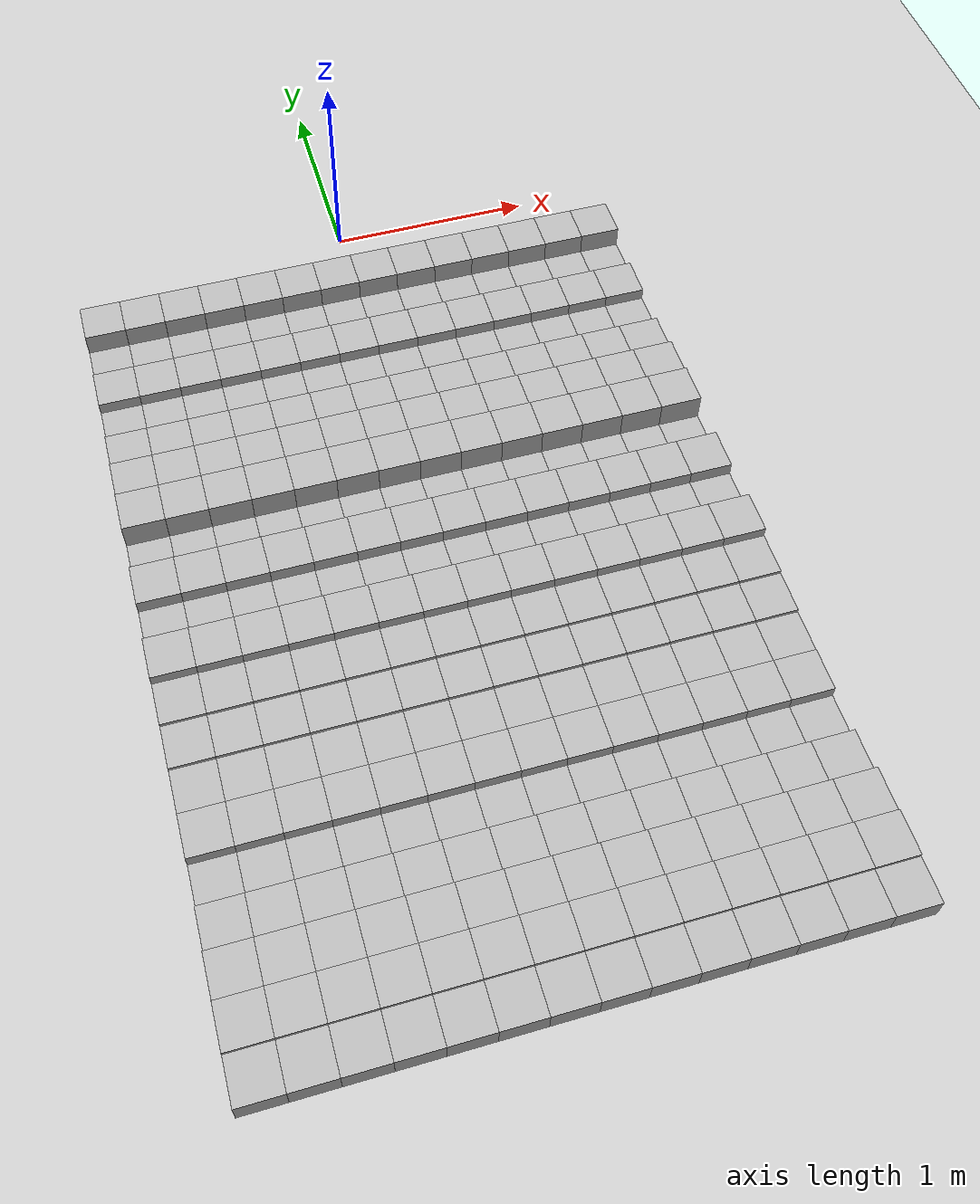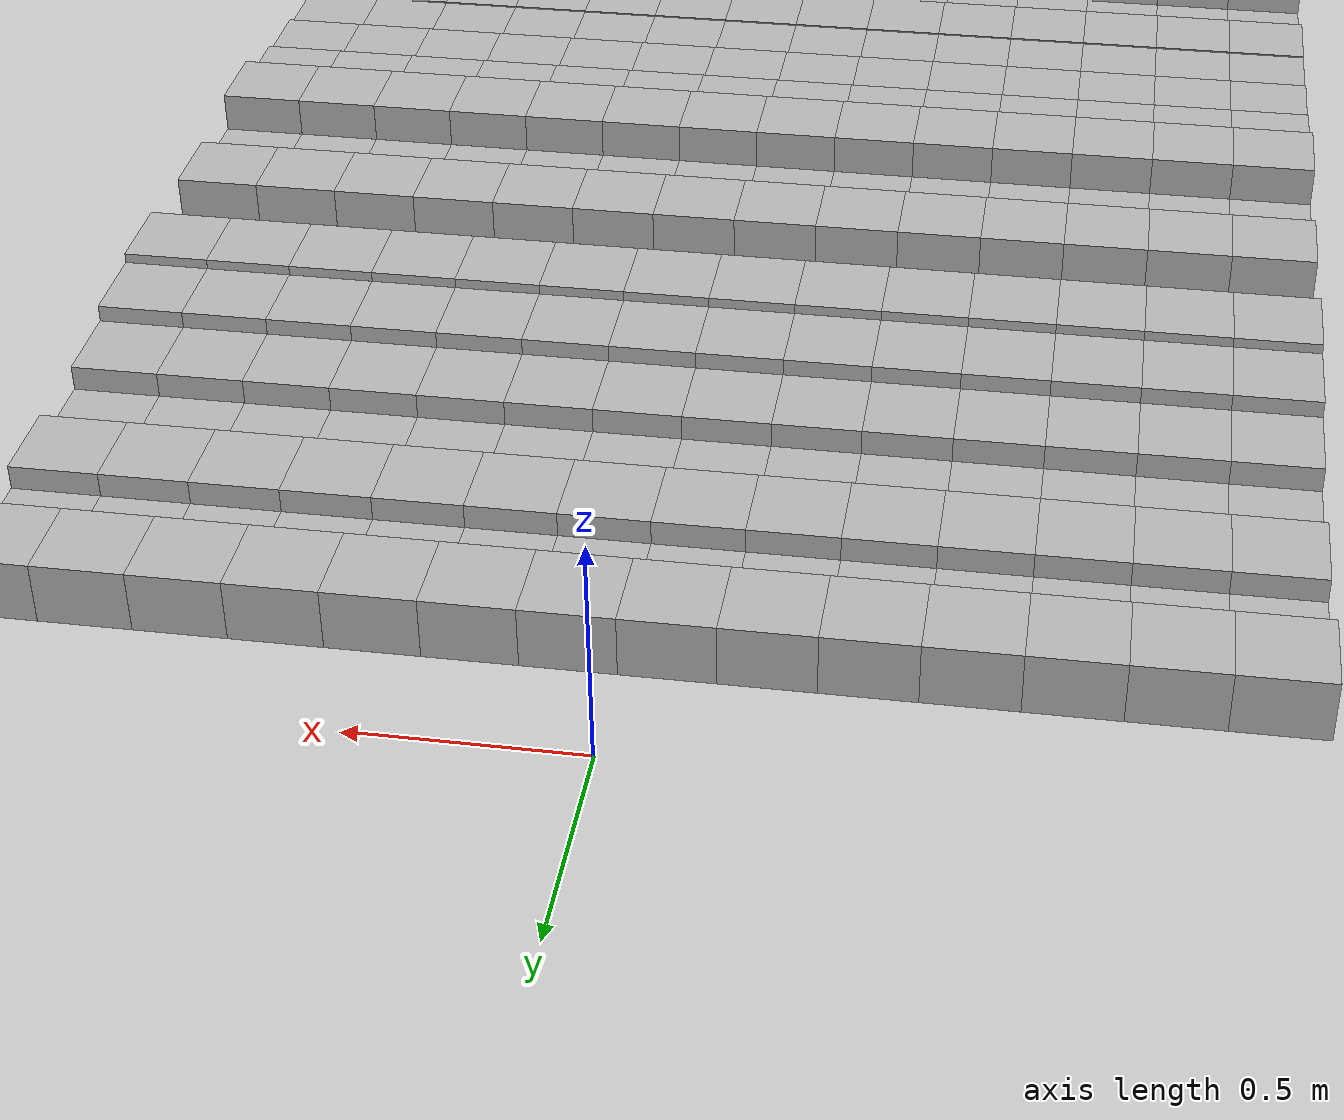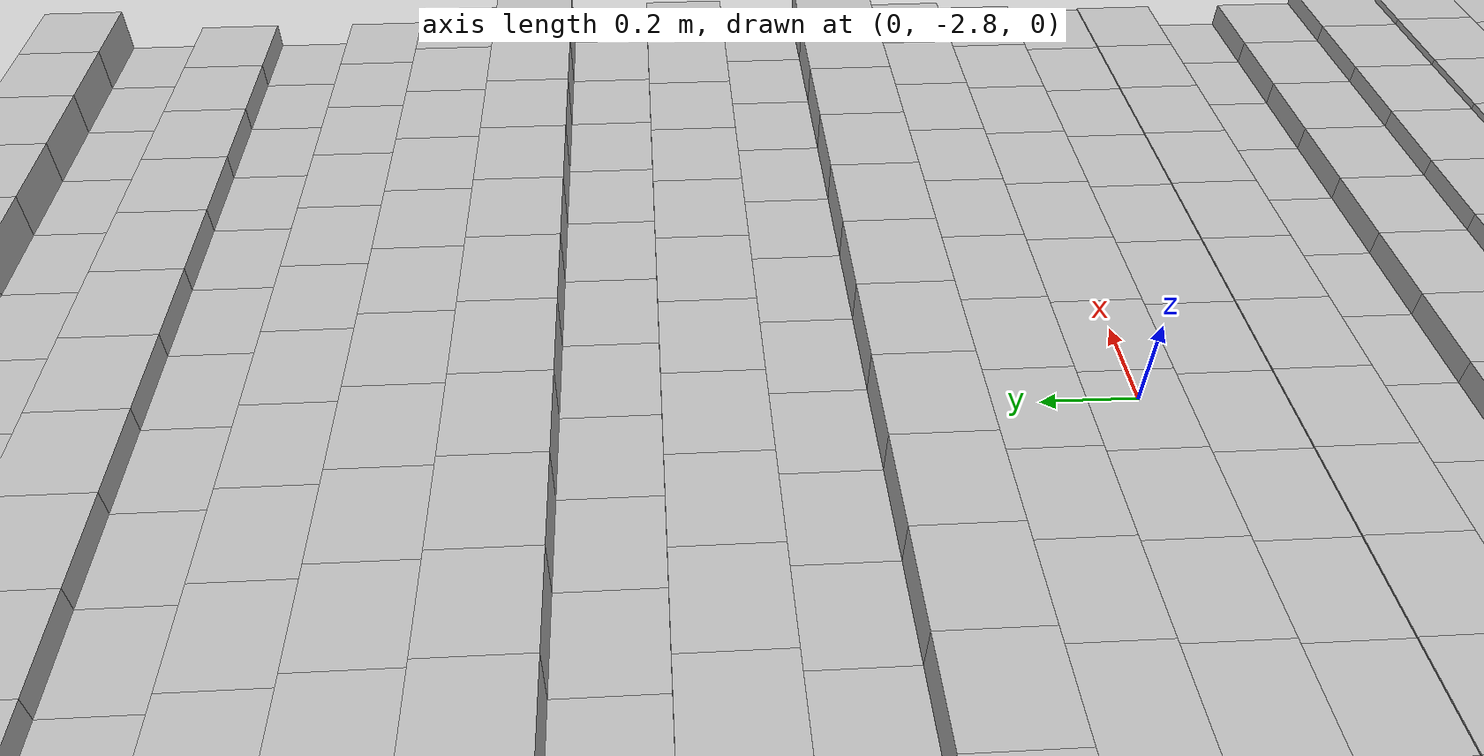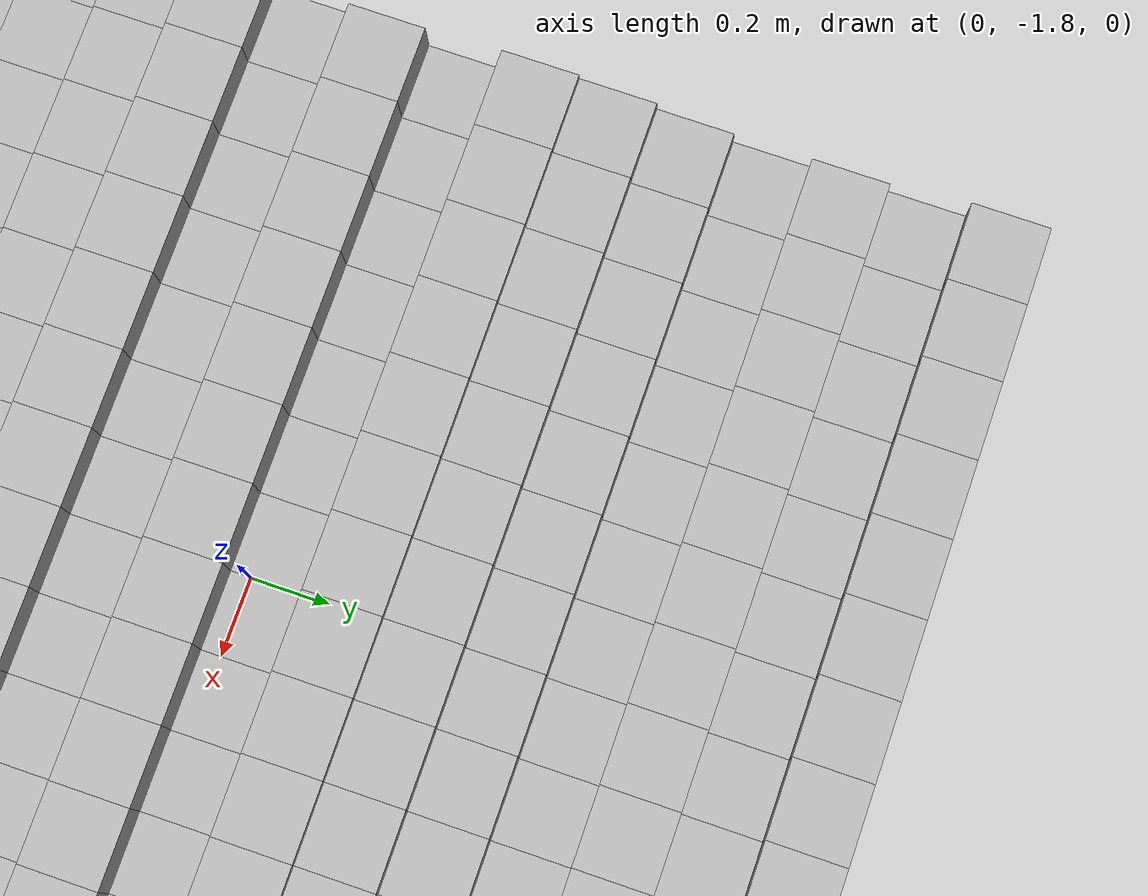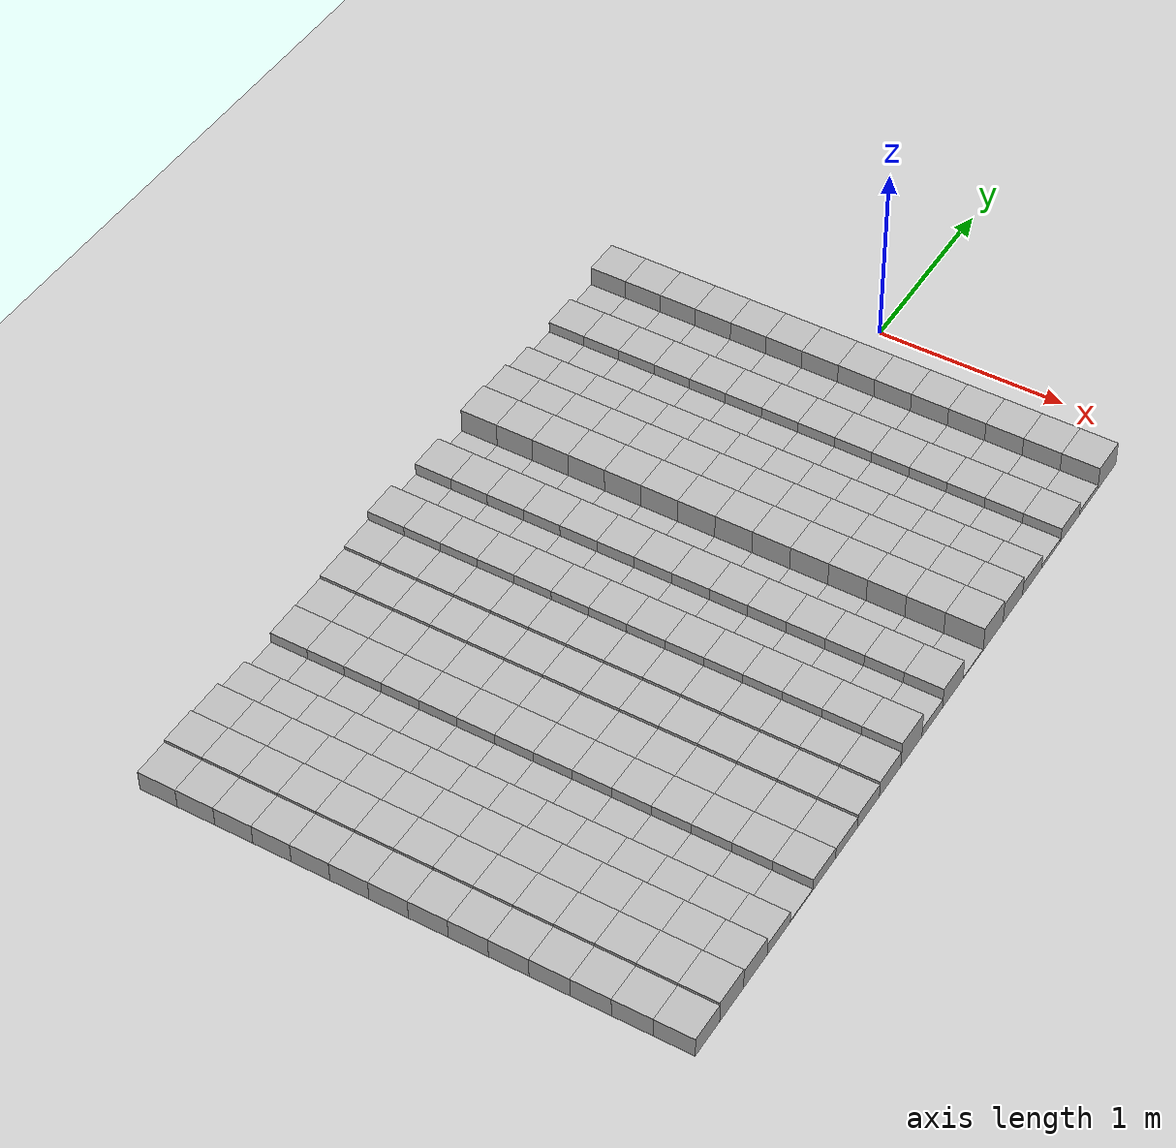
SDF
<?xml version="1.0" ?>
<sdf version="1.6">
  <world name="default">
  <gravity>0 0 -9.81</gravity>
  <physics name="ode_400iters" type="ode" default="true">
    <!-- the combination of 2 params below provides real time factor speed for simulation -->
    <!-- max_real_time_factor = real_time_update_rate * max_step_size -->
    <!-- min_real_time_factor depends only from max_step_size -->
    <real_time_update_rate>1000</real_time_update_rate>
    <max_step_size>0.0002</max_step_size>
      <ode>
        <solver>
          <type>quick</type>
          <iters>900</iters>
          <!-- sor is number for more accurate results of convergence (сходимость)-->
           <sor>0.9</sor>
        </solver>
        <constraints>
      </constraints>
      </ode>
    </physics>
    <include>
      <uri>model://strirus_gazebo/maps/Ground_plane</uri>
    </include>
    <include>
      <uri>model://sun</uri>
    </include>
        <include>
		<uri>model://strirus_gazebo/maps/Generated_terrain</uri>
      <name>Terrain</name>
      <pose>0 -0.35 0 0 0 0</pose>
    </include>
  </world>
</sdf>

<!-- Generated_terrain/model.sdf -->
<sdf version='1.6'>
	<model name='Terrain'>
		<static>true</static>
		<link name="box_0_0">
			<pose>-1.3 0.0 0.0700350616192 0 0 0</pose>
			<inertial>
				<mass>1.0</mass>
				<inertia>
					<ixx>0.0</ixx>
 					<ixy>0.0</ixy>
   					<ixz>0.0</ixz>
   					<iyy>0.0</iyy>
 					<iyz>0.0</iyz>
   					<izz>0.0</izz>
 				</inertia>
			</inertial>
			<collision name="collision">
				<geometry>
					<box>
						<size>0.2 0.2 0.140070123238</size>
					</box>
				</geometry>
			</collision>
			<visual name="visual">
				<geometry>
					<box>
						<size>0.2 0.2 0.140070123238</size>
					</box>
				</geometry>
			</visual>
		</link>

		<link name="box_0_1">
			<pose>-1.1 0.0 0.0700350616192 0 0 0</pose>
			<inertial>
				<mass>1.0</mass>
				<inertia>
					<ixx>0.0</ixx>
 					<ixy>0.0</ixy>
   					<ixz>0.0</ixz>
   					<iyy>0.0</iyy>
 					<iyz>0.0</iyz>
   					<izz>0.0</izz>
 				</inertia>
			</inertial>
			<collision name="collision">
				<geometry>
					<box>
						<size>0.2 0.2 0.140070123238</size>
					</box>
				</geometry>
			</collision>
			<visual name="visual">
				<geometry>
					<box>
						<size>0.2 0.2 0.140070123238</size>
					</box>
				</geometry>
			</visual>
		</link>

		<link name="box_0_2">
			<pose>-0.9 0.0 0.0700350616192 0 0 0</pose>
			<inertial>
				<mass>1.0</mass>
				<inertia>
					<ixx>0.0</ixx>
 					<ixy>0.0</ixy>
   					<ixz>0.0</ixz>
   					<iyy>0.0</iyy>
 					<iyz>0.0</iyz>
   					<izz>0.0</izz>
 				</inertia>
			</inertial>
			<collision name="collision">
				<geometry>
					<box>
						<size>0.2 0.2 0.140070123238</size>
					</box>
				</geometry>
			</collision>
			<visual name="visual">
				<geometry>
					<box>
						<size>0.2 0.2 0.140070123238</size>
					</box>
				</geometry>
			</visual>
		</link>

		<link name="box_0_3">
			<pose>-0.7 0.0 0.0700350616192 0 0 0</pose>
			<inertial>
				<mass>1.0</mass>
				<inertia>
					<ixx>0.0</ixx>
 					<ixy>0.0</ixy>
   					<ixz>0.0</ixz>
   					<iyy>0.0</iyy>
 					<iyz>0.0</iyz>
   					<izz>0.0</izz>
 				</inertia>
			</inertial>
			<collision name="collision">
				<geometry>
					<box>
						<size>0.2 0.2 0.140070123238</size>
					</box>
				</geometry>
			</collision>
			<visual name="visual">
				<geometry>
					<box>
						<size>0.2 0.2 0.140070123238</size>
					</box>
				</geometry>
			</visual>
		</link>

		<link name="box_0_4">
			<pose>-0.5 0.0 0.0700350616192 0 0 0</pose>
			<inertial>
				<mass>1.0</mass>
				<inertia>
					<ixx>0.0</ixx>
 					<ixy>0.0</ixy>
   					<ixz>0.0</ixz>
   					<iyy>0.0</iyy>
 					<iyz>0.0</iyz>
   					<izz>0.0</izz>
 				</inertia>
			</inertial>
			<collision name="collision">
				<geometry>
					<box>
						<size>0.2 0.2 0.140070123238</size>
					</box>
				</geometry>
			</collision>
			<visual name="visual">
				<geometry>
					<box>
						<size>0.2 0.2 0.140070123238</size>
					</box>
				</geometry>
			</visual>
		</link>

		<link name="box_0_5">
			<pose>-0.3 0.0 0.0700350616192 0 0 0</pose>
			<inertial>
				<mass>1.0</mass>
				<inertia>
					<ixx>0.0</ixx>
 					<ixy>0.0</ixy>
   					<ixz>0.0</ixz>
   					<iyy>0.0</iyy>
 					<iyz>0.0</iyz>
   					<izz>0.0</izz>
 				</inertia>
			</inertial>
			<collision name="collision">
				<geometry>
					<box>
						<size>0.2 0.2 0.140070123238</size>
					</box>
				</geometry>
			</collision>
			<visual name="visual">
				<geometry>
					<box>
						<size>0.2 0.2 0.140070123238</size>
					</box>
				</geometry>
			</visual>
		</link>

		<link name="box_0_6">
			<pose>-0.1 0.0 0.0700350616192 0 0 0</pose>
			<inertial>
				<mass>1.0</mass>
				<inertia>
					<ixx>0.0</ixx>
 					<ixy>0.0</ixy>
   					<ixz>0.0</ixz>
   					<iyy>0.0</iyy>
 					<iyz>0.0</iyz>
   					<izz>0.0</izz>
 				</inertia>
			</inertial>
			<collision name="collision">
				<geometry>
					<box>
						<size>0.2 0.2 0.140070123238</size>
					</box>
				</geometry>
			</collision>
			<visual name="visual">
				<geometry>
					<box>
						<size>0.2 0.2 0.140070123238</size>
					</box>
				</geometry>
			</visual>
		</link>

		<link name="box_0_7">
			<pose>0.1 0.0 0.0700350616192 0 0 0</pose>
			<inertial>
				<mass>1.0</mass>
				<inertia>
					<ixx>0.0</ixx>
 					<ixy>0.0</ixy>
   					<ixz>0.0</ixz>
   					<iyy>0.0</iyy>
 					<iyz>0.0</iyz>
   					<izz>0.0</izz>
 				</inertia>
			</inertial>
			<collision name="collision">
				<geometry>
					<box>
						<size>0.2 0.2 0.140070123238</size>
					</box>
				</geometry>
			</collision>
			<visual name="visual">
				<geometry>
					<box>
						<size>0.2 0.2 0.140070123238</size>
					</box>
				</geometry>
			</visual>
		</link>

		<link name="box_0_8">
			<pose>0.3 0.0 0.0700350616192 0 0 0</pose>
			<inertial>
				<mass>1.0</mass>
				<inertia>
					<ixx>0.0</ixx>
 					<ixy>0.0</ixy>
   					<ixz>0.0</ixz>
   					<iyy>0.0</iyy>
 					<iyz>0.0</iyz>
   					<izz>0.0</izz>
 				</inertia>
			</inertial>
			<collision name="collision">
				<geometry>
					<box>
						<size>0.2 0.2 0.140070123238</size>
					</box>
				</geometry>
			</collision>
			<visual name="visual">
				<geometry>
					<box>
						<size>0.2 0.2 0.140070123238</size>
					</box>
				</geometry>
			</visual>
		</link>

		<link name="box_0_9">
			<pose>0.5 0.0 0.0700350616192 0 0 0</pose>
			<inertial>
				<mass>1.0</mass>
				<inertia>
					<ixx>0.0</ixx>
 					<ixy>0.0</ixy>
   					<ixz>0.0</ixz>
   					<iyy>0.0</iyy>
 					<iyz>0.0</iyz>
   					<izz>0.0</izz>
 				</inertia>
			</inertial>
			<collision name="collision">
				<geometry>
					<box>
						<size>0.2 0.2 0.140070123238</size>
					</box>
				</geometry>
			</collision>
			<visual name="visual">
				<geometry>
					<box>
						<size>0.2 0.2 0.140070123238</size>
					</box>
				</geometry>
			</visual>
		</link>

		<link name="box_0_10">
			<pose>0.7 0.0 0.0700350616192 0 0 0</pose>
			<inertial>
				<mass>1.0</mass>
				<inertia>
					<ixx>0.0</ixx>
 					<ixy>0.0</ixy>
   					<ixz>0.0</ixz>
   					<iyy>0.0</iyy>
 					<iyz>0.0</iyz>
   					<izz>0.0</izz>
 				</inertia>
			</inertial>
			<collision name="collision">
				<geometry>
					<box>
						<size>0.2 0.2 0.140070123238</size>
					</box>
				</geometry>
			</collision>
			<visual name="visual">
				<geometry>
					<box>
						<size>0.2 0.2 0.140070123238</size>
					</box>
				</geometry>
			</visual>
		</link>

		<link name="box_0_11">
			<pose>0.9 0.0 0.0700350616192 0 0 0</pose>
			<inertial>
				<mass>1.0</mass>
				<inertia>
					<ixx>0.0</ixx>
 					<ixy>0.0</ixy>
   					<ixz>0.0</ixz>
   					<iyy>0.0</iyy>
 					<iyz>0.0</iyz>
   					<izz>0.0</izz>
 				</inertia>
			</inertial>
			<collision name="collision">
				<geometry>
					<box>
						<size>0.2 0.2 0.140070123238</size>
					</box>
				</geometry>
			</collision>
			<visual name="visual">
				<geometry>
					<box>
						<size>0.2 0.2 0.140070123238</size>
					</box>
				</geometry>
			</visual>
		</link>

		<link name="box_0_12">
			<pose>1.1 0.0 0.0700350616192 0 0 0</pose>
			<inertial>
				<mass>1.0</mass>
				<inertia>
					<ixx>0.0</ixx>
 					<ixy>0.0</ixy>
   					<ixz>0.0</ixz>
   					<iyy>0.0</iyy>
 					<iyz>0.0</iyz>
   					<izz>0.0</izz>
 				</inertia>
			</inertial>
			<collision name="collision">
				<geometry>
					<box>
						<size>0.2 0.2 0.140070123238</size>
					</box>
				</geometry>
			</collision>
			<visual name="visual">
				<geometry>
					<box>
						<size>0.2 0.2 0.140070123238</size>
					</box>
				</geometry>
			</visual>
		</link>

		<link name="box_0_13">
			<pose>1.3 0.0 0.0700350616192 0 0 0</pose>
			<inertial>
				<mass>1.0</mass>
				<inertia>
					<ixx>0.0</ixx>
 					<ixy>0.0</ixy>
   					<ixz>0.0</ixz>
   					<iyy>0.0</iyy>
 					<iyz>0.0</iyz>
   					<izz>0.0</izz>
 				</inertia>
			</inertial>
			<collision name="collision">
				<geometry>
					<box>
						<size>0.2 0.2 0.140070123238</size>
					</box>
				</geometry>
			</collision>
			<visual name="visual">
				<geometry>
					<box>
						<size>0.2 0.2 0.140070123238</size>
					</box>
				</geometry>
			</visual>
		</link>

		<link name="box_1_0">
			<pose>-1.3 -0.2 0.0147610610979 0 0 0</pose>
			<inertial>
				<mass>1.0</mass>
				<inertia>
					<ixx>0.0</ixx>
 					<ixy>0.0</ixy>
   					<ixz>0.0</ixz>
   					<iyy>0.0</iyy>
 					<iyz>0.0</iyz>
   					<izz>0.0</izz>
 				</inertia>
			</inertial>
			<collision name="collision">
				<geometry>
					<box>
						<size>0.2 0.2 0.0295221221957</size>
					</box>
				</geometry>
			</collision>
			<visual name="visual">
				<geometry>
					<box>
						<size>0.2 0.2 0.0295221221957</size>
					</box>
				</geometry>
			</visual>
		</link>

		<link name="box_1_1">
			<pose>-1.1 -0.2 0.0147610610979 0 0 0</pose>
			<inertial>
				<mass>1.0</mass>
				<inertia>
					<ixx>0.0</ixx>
 					<ixy>0.0</ixy>
   					<ixz>0.0</ixz>
   					<iyy>0.0</iyy>
 					<iyz>0.0</iyz>
   					<izz>0.0</izz>
 				</inertia>
			</inertial>
			<collision name="collision">
				<geometry>
					<box>
						<size>0.2 0.2 0.0295221221957</size>
					</box>
				</geometry>
			</collision>
			<visual name="visual">
				<geometry>
					<box>
						<size>0.2 0.2 0.0295221221957</size>
					</box>
				</geometry>
			</visual>
		</link>

		<link name="box_1_2">
			<pose>-0.9 -0.2 0.0147610610979 0 0 0</pose>
			<inertial>
				<mass>1.0</mass>
				<inertia>
					<ixx>0.0</ixx>
 					<ixy>0.0</ixy>
   					<ixz>0.0</ixz>
   					<iyy>0.0</iyy>
 					<iyz>0.0</iyz>
   					<izz>0.0</izz>
 				</inertia>
			</inertial>
			<collision name="collision">
				<geometry>
					<box>
						<size>0.2 0.2 0.0295221221957</size>
					</box>
				</geometry>
			</collision>
			<visual name="visual">
				<geometry>
					<box>
						<size>0.2 0.2 0.0295221221957</size>
					</box>
				</geometry>
			</visual>
		</link>

		<link name="box_1_3">
			<pose>-0.7 -0.2 0.0147610610979 0 0 0</pose>
			<inertial>
				<mass>1.0</mass>
				<inertia>
					<ixx>0.0</ixx>
 					<ixy>0.0</ixy>
   					<ixz>0.0</ixz>
   					<iyy>0.0</iyy>
 					<iyz>0.0</iyz>
   					<izz>0.0</izz>
 				</inertia>
			</inertial>
			<collision name="collision">
				<geometry>
					<box>
						<size>0.2 0.2 0.0295221221957</size>
					</box>
				</geometry>
			</collision>
			<visual name="visual">
				<geometry>
					<box>
						<size>0.2 0.2 0.0295221221957</size>
					</box>
				</geometry>
			</visual>
		</link>

		<link name="box_1_4">
			<pose>-0.5 -0.2 0.0147610610979 0 0 0</pose>
			<inertial>
				<mass>1.0</mass>
				<inertia>
					<ixx>0.0</ixx>
 					<ixy>0.0</ixy>
   					<ixz>0.0</ixz>
   					<iyy>0.0</iyy>
 					<iyz>0.0</iyz>
   					<izz>0.0</izz>
 				</inertia>
			</inertial>
			<collision name="collision">
				<geometry>
					<box>
						<size>0.2 0.2 0.0295221221957</size>
					</box>
				</geometry>
			</collision>
			<visual name="visual">
				<geometry>
					<box>
						<size>0.2 0.2 0.0295221221957</size>
					</box>
				</geometry>
			</visual>
		</link>

		<link name="box_1_5">
			<pose>-0.3 -0.2 0.0147610610979 0 0 0</pose>
			<inertial>
				<mass>1.0</mass>
				<inertia>
					<ixx>0.0</ixx>
 					<ixy>0.0</ixy>
   					<ixz>0.0</ixz>
   					<iyy>0.0</iyy>
 					<iyz>0.0</iyz>
   					<izz>0.0</izz>
 				</inertia>
			</inertial>
			<collision name="collision">
				<geometry>
					<box>
						<size>0.2 0.2 0.0295221221957</size>
					</box>
				</geometry>
			</collision>
			<visual name="visual">
				<geometry>
					<box>
						<size>0.2 0.2 0.0295221221957</size>
					</box>
				</geometry>
			</visual>
		</link>

		<link name="box_1_6">
			<pose>-0.1 -0.2 0.0147610610979 0 0 0</pose>
			<inertial>
				<mass>1.0</mass>
				<inertia>
					<ixx>0.0</ixx>
 					<ixy>0.0</ixy>
   					<ixz>0.0</ixz>
   					<iyy>0.0</iyy>
 					<iyz>0.0</iyz>
   					<izz>0.0</izz>
 				</inertia>
			</inertial>
			<collision name="collision">
				<geometry>
					<box>
						<size>0.2 0.2 0.0295221221957</size>
					</box>
				</geometry>
			</collision>
			<visual name="visual">
				<geometry>
					<box>
						<size>0.2 0.2 0.0295221221957</size>
					</box>
				</geometry>
			</visual>
		</link>

		<link name="box_1_7">
			<pose>0.1 -0.2 0.0147610610979 0 0 0</pose>
			<inertial>
				<mass>1.0</mass>
				<inertia>
					<ixx>0.0</ixx>
 					<ixy>0.0</ixy>
   					<ixz>0.0</ixz>
   					<iyy>0.0</iyy>
 					<iyz>0.0</iyz>
   					<izz>0.0</izz>
 				</inertia>
			</inertial>
			<collision name="collision">
				<geometry>
					<box>
						<size>0.2 0.2 0.0295221221957</size>
					</box>
				</geometry>
			</collision>
			<visual name="visual">
				<geometry>
					<box>
						<size>0.2 0.2 0.0295221221957</size>
					</box>
				</geometry>
			</visual>
		</link>

		<link name="box_1_8">
			<pose>0.3 -0.2 0.0147610610979 0 0 0</pose>
			<inertial>
				<mass>1.0</mass>
				<inertia>
					<ixx>0.0</ixx>
 					<ixy>0.0</ixy>
   					<ixz>0.0</ixz>
   					<iyy>0.0</iyy>
 					<iyz>0.0</iyz>
   					<izz>0.0</izz>
 				</inertia>
			</inertial>
			<collision name="collision">
				<geometry>
					<box>
						<size>0.2 0.2 0.0295221221957</size>
					</box>
				</geometry>
			</collision>
			<visual name="visual">
				<geometry>
					<box>
						<size>0.2 0.2 0.0295221221957</size>
					</box>
				</geometry>
			</visual>
		</link>

		<link name="box_1_9">
			<pose>0.5 -0.2 0.0147610610979 0 0 0</pose>
			<inertial>
				<mass>1.0</mass>
				<inertia>
					<ixx>0.0</ixx>
 					<ixy>0.0</ixy>
   					<ixz>0.0</ixz>
   					<iyy>0.0</iyy>
 					<iyz>0.0</iyz>
   					<izz>0.0</izz>
 				</inertia>
			</inertial>
			<collision name="collision">
				<geometry>
					<box>
						<size>0.2 0.2 0.0295221221957</size>
					</box>
				</geometry>
			</collision>
			<visual name="visual">
				<geometry>
					<box>
						<size>0.2 0.2 0.0295221221957</size>
					</box>
				</geometry>
			</visual>
		</link>

		<link name="box_1_10">
			<pose>0.7 -0.2 0.0147610610979 0 0 0</pose>
			<inertial>
				<mass>1.0</mass>
				<inertia>
					<ixx>0.0</ixx>
 					<ixy>0.0</ixy>
   					<ixz>0.0</ixz>
   					<iyy>0.0</iyy>
 					<iyz>0.0</iyz>
   					<izz>0.0</izz>
 				</inertia>
			</inertial>
			<collision name="collision">
				<geometry>
					<box>
						<size>0.2 0.2 0.0295221221957</size>
					</box>
				</geometry>
			</collision>
			<visual name="visual">
				<geometry>
					<box>
						<size>0.2 0.2 0.0295221221957</size>
					</box>
				</geometry>
			</visual>
		</link>

		<link name="box_1_11">
			<pose>0.9 -0.2 0.0147610610979 0 0 0</pose>
			<inertial>
				<mass>1.0</mass>
				<inertia>
					<ixx>0.0</ixx>
 					<ixy>0.0</ixy>
   					<ixz>0.0</ixz>
   					<iyy>0.0</iyy>
 					<iyz>0.0</iyz>
   					<izz>0.0</izz>
 				</inertia>
			</inertial>
			<collision name="collision">
				<geometry>
					<box>
						<size>0.2 0.2 0.0295221221957</size>
					</box>
				</geometry>
			</collision>
			<visual name="visual">
				<geometry>
					<box>
						<size>0.2 0.2 0.0295221221957</size>
					</box>
				</geometry>
			</visual>
		</link>

		<link name="box_1_12">
			<pose>1.1 -0.2 0.0147610610979 0 0 0</pose>
			<inertial>
				<mass>1.0</mass>
				<inertia>
					<ixx>0.0</ixx>
 					<ixy>0.0</ixy>
   					<ixz>0.0</ixz>
   					<iyy>0.0</iyy>
 					<iyz>0.0</iyz>
   					<izz>0.0</izz>
 				</inertia>
			</inertial>
			<collision name="collision">
				<geometry>
					<box>
						<size>0.2 0.2 0.0295221221957</size>
					</box>
				</geometry>
			</collision>
			<visual name="visual">
				<geometry>
					<box>
						<size>0.2 0.2 0.0295221221957</size>
					</box>
				</geometry>
			</visual>
		</link>

		<link name="box_1_13">
			<pose>1.3 -0.2 0.0147610610979 0 0 0</pose>
			<inertial>
				<mass>1.0</mass>
				<inertia>
					<ixx>0.0</ixx>
 					<ixy>0.0</ixy>
   					<ixz>0.0</ixz>
   					<iyy>0.0</iyy>
 					<iyz>0.0</iyz>
   					<izz>0.0</izz>
 				</inertia>
			</inertial>
			<collision name="collision">
				<geometry>
					<box>
						<size>0.2 0.2 0.0295221221957</size>
					</box>
				</geometry>
			</collision>
			<visual name="visual">
				<geometry>
					<box>
						<size>0.2 0.2 0.0295221221957</size>
					</box>
				</geometry>
			</visual>
		</link>

		<link name="box_2_0">
			<pose>-1.3 -0.4 0.0431147949159 0 0 0</pose>
			<inertial>
				<mass>1.0</mass>
				<inertia>
					<ixx>0.0</ixx>
 					<ixy>0.0</ixy>
   					<ixz>0.0</ixz>
   					<iyy>0.0</iyy>
 					<iyz>0.0</iyz>
   					<izz>0.0</izz>
 				</inertia>
			</inertial>
			<collision name="collision">
				<geometry>
					<box>
						<size>0.2 0.2 0.0862295898317</size>
					</box>
				</geometry>
			</collision>
			<visual name="visual">
				<geometry>
					<box>
						<size>0.2 0.2 0.0862295898317</size>
					</box>
				</geometry>
			</visual>
		</link>

		<link name="box_2_1">
			<pose>-1.1 -0.4 0.0431147949159 0 0 0</pose>
			<inertial>
				<mass>1.0</mass>
				<inertia>
					<ixx>0.0</ixx>
 					<ixy>0.0</ixy>
   					<ixz>0.0</ixz>
   					<iyy>0.0</iyy>
 					<iyz>0.0</iyz>
   					<izz>0.0</izz>
 				</inertia>
			</inertial>
			<collision name="collision">
				<geometry>
					<box>
						<size>0.2 0.2 0.0862295898317</size>
					</box>
				</geometry>
			</collision>
			<visual name="visual">
				<geometry>
					<box>
						<size>0.2 0.2 0.0862295898317</size>
					</box>
				</geometry>
			</visual>
		</link>

		<link name="box_2_2">
			<pose>-0.9 -0.4 0.0431147949159 0 0 0</pose>
			<inertial>
				<mass>1.0</mass>
				<inertia>
					<ixx>0.0</ixx>
 					<ixy>0.0</ixy>
   					<ixz>0.0</ixz>
   					<iyy>0.0</iyy>
 					<iyz>0.0</iyz>
   					<izz>0.0</izz>
 				</inertia>
			</inertial>
			<collision name="collision">
				<geometry>
					<box>
						<size>0.2 0.2 0.0862295898317</size>
					</box>
				</geometry>
			</collision>
			<visual name="visual">
				<geometry>
					<box>
						<size>0.2 0.2 0.0862295898317</size>
					</box>
				</geometry>
			</visual>
		</link>

		<link name="box_2_3">
			<pose>-0.7 -0.4 0.0431147949159 0 0 0</pose>
			<inertial>
				<mass>1.0</mass>
				<inertia>
					<ixx>0.0</ixx>
 					<ixy>0.0</ixy>
   					<ixz>0.0</ixz>
   					<iyy>0.0</iyy>
 					<iyz>0.0</iyz>
   					<izz>0.0</izz>
 				</inertia>
			</inertial>
			<collision name="collision">
				<geometry>
					<box>
						<size>0.2 0.2 0.0862295898317</size>
					</box>
				</geometry>
			</collision>
			<visual name="visual">
				<geometry>
					<box>
						<size>0.2 0.2 0.0862295898317</size>
					</box>
				</geometry>
			</visual>
		</link>

		<link name="box_2_4">
			<pose>-0.5 -0.4 0.0431147949159 0 0 0</pose>
			<inertial>
				<mass>1.0</mass>
				<inertia>
					<ixx>0.0</ixx>
 					<ixy>0.0</ixy>
   					<ixz>0.0</ixz>
   					<iyy>0.0</iyy>
 					<iyz>0.0</iyz>
   					<izz>0.0</izz>
 				</inertia>
			</inertial>
			<collision name="collision">
				<geometry>
					<box>
						<size>0.2 0.2 0.0862295898317</size>
					</box>
				</geometry>
			</collision>
			<visual name="visual">
				<geometry>
					<box>
						<size>0.2 0.2 0.0862295898317</size>
					</box>
				</geometry>
			</visual>
		</link>

		<link name="box_2_5">
			<pose>-0.3 -0.4 0.0431147949159 0 0 0</pose>
			<inertial>
				<mass>1.0</mass>
				<inertia>
					<ixx>0.0</ixx>
 					<ixy>0.0</ixy>
   					<ixz>0.0</ixz>
   					<iyy>0.0</iyy>
 					<iyz>0.0</iyz>
   					<izz>0.0</izz>
 				</inertia>
			</inertial>
			<collision name="collision">
				<geometry>
					<box>
						<size>0.2 0.2 0.0862295898317</size>
					</box>
				</geometry>
			</collision>
			<visual name="visual">
				<geometry>
					<box>
						<size>0.2 0.2 0.0862295898317</size>
					</box>
				</geometry>
			</visual>
		</link>

		<link name="box_2_6">
			<pose>-0.1 -0.4 0.0431147949159 0 0 0</pose>
			<inertial>
				<mass>1.0</mass>
				<inertia>
					<ixx>0.0</ixx>
 					<ixy>0.0</ixy>
   					<ixz>0.0</ixz>
   					<iyy>0.0</iyy>
 					<iyz>0.0</iyz>
   					<izz>0.0</izz>
 				</inertia>
			</inertial>
			<collision name="collision">
				<geometry>
					<box>
						<size>0.2 0.2 0.0862295898317</size>
					</box>
				</geometry>
			</collision>
			<visual name="visual">
				<geometry>
					<box>
						<size>0.2 0.2 0.0862295898317</size>
					</box>
				</geometry>
			</visual>
		</link>

		<link name="box_2_7">
			<pose>0.1 -0.4 0.0431147949159 0 0 0</pose>
			<inertial>
				<mass>1.0</mass>
				<inertia>
					<ixx>0.0</ixx>
 					<ixy>0.0</ixy>
   					<ixz>0.0</ixz>
   					<iyy>0.0</iyy>
 					<iyz>0.0</iyz>
   					<izz>0.0</izz>
 				</inertia>
			</inertial>
			<collision name="collision">
				<geometry>
					<box>
						<size>0.2 0.2 0.0862295898317</size>
					</box>
				</geometry>
			</collision>
			<visual name="visual">
				<geometry>
					<box>
						<size>0.2 0.2 0.0862295898317</size>
					</box>
				</geometry>
			</visual>
		</link>

		<link name="box_2_8">
			<pose>0.3 -0.4 0.0431147949159 0 0 0</pose>
			<inertial>
				<mass>1.0</mass>
				<inertia>
					<ixx>0.0</ixx>
 					<ixy>0.0</ixy>
   					<ixz>0.0</ixz>
   					<iyy>0.0</iyy>
 					<iyz>0.0</iyz>
   					<izz>0.0</izz>
 				</inertia>
			</inertial>
			<collision name="collision">
				<geometry>
					<box>
						<size>0.2 0.2 0.0862295898317</size>
					</box>
				</geometry>
			</collision>
			<visual name="visual">
				<geometry>
					<box>
						<size>0.2 0.2 0.0862295898317</size>
					</box>
				</geometry>
			</visual>
		</link>

		<link name="box_2_9">
			<pose>0.5 -0.4 0.0431147949159 0 0 0</pose>
			<inertial>
				<mass>1.0</mass>
				<inertia>
					<ixx>0.0</ixx>
 					<ixy>0.0</ixy>
   					<ixz>0.0</ixz>
   					<iyy>0.0</iyy>
 					<iyz>0.0</iyz>
   					<izz>0.0</izz>
 				</inertia>
			</inertial>
			<collision name="collision">
				<geometry>
					<box>
						<size>0.2 0.2 0.0862295898317</size>
					</box>
				</geometry>
			</collision>
			<visual name="visual">
				<geometry>
					<box>
						<size>0.2 0.2 0.0862295898317</size>
					</box>
				</geometry>
			</visual>
		</link>

		<link name="box_2_10">
			<pose>0.7 -0.4 0.0431147949159 0 0 0</pose>
			<inertial>
				<mass>1.0</mass>
				<inertia>
					<ixx>0.0</ixx>
 					<ixy>0.0</ixy>
   					<ixz>0.0</ixz>
   					<iyy>0.0</iyy>
 					<iyz>0.0</iyz>
   					<izz>0.0</izz>
 				</inertia>
			</inertial>
			<collision name="collision">
				<geometry>
					<box>
						<size>0.2 0.2 0.0862295898317</size>
					</box>
				</geometry>
			</collision>
			<visual name="visual">
				<geometry>
					<box>
						<size>0.2 0.2 0.0862295898317</size>
					</box>
				</geometry>
			</visual>
		</link>

		<link name="box_2_11">
			<pose>0.9 -0.4 0.0431147949159 0 0 0</pose>
			<inertial>
				<mass>1.0</mass>
				<inertia>
					<ixx>0.0</ixx>
 					<ixy>0.0</ixy>
   					<ixz>0.0</ixz>
   					<iyy>0.0</iyy>
 					<iyz>0.0</iyz>
   					<izz>0.0</izz>
 				</inertia>
			</inertial>
			<collision name="collision">
				<geometry>
					<box>
						<size>0.2 0.2 0.0862295898317</size>
					</box>
				</geometry>
			</collision>
			<visual name="visual">
				<geometry>
					<box>
						<size>0.2 0.2 0.0862295898317</size>
					</box>
				</geometry>
			</visual>
		</link>

		<link name="box_2_12">
			<pose>1.1 -0.4 0.0431147949159 0 0 0</pose>
			<inertial>
				<mass>1.0</mass>
				<inertia>
					<ixx>0.0</ixx>
 					<ixy>0.0</ixy>
   					<ixz>0.0</ixz>
   					<iyy>0.0</iyy>
 					<iyz>0.0</iyz>
   					<izz>0.0</izz>
 				</inertia>
			</inertial>
			<collision name="collision">
				<geometry>
					<box>
						<size>0.2 0.2 0.0862295898317</size>
					</box>
				</geometry>
			</collision>
			<visual name="visual">
				<geometry>
					<box>
						<size>0.2 0.2 0.0862295898317</size>
					</box>
				</geometry>
			</visual>
		</link>

		<link name="box_2_13">
			<pose>1.3 -0.4 0.0431147949159 0 0 0</pose>
			<inertial>
				<mass>1.0</mass>
				<inertia>
					<ixx>0.0</ixx>
 					<ixy>0.0</ixy>
   					<ixz>0.0</ixz>
   					<iyy>0.0</iyy>
 					<iyz>0.0</iyz>
   					<izz>0.0</izz>
 				</inertia>
			</inertial>
			<collision name="collision">
				<geometry>
					<box>
						<size>0.2 0.2 0.0862295898317</size>
					</box>
				</geometry>
			</collision>
			<visual name="visual">
				<geometry>
					<box>
						<size>0.2 0.2 0.0862295898317</size>
					</box>
				</geometry>
			</visual>
		</link>

		<link name="box_3_0">
			<pose>-1.3 -0.6 0.012055614394 0 0 0</pose>
			<inertial>
				<mass>1.0</mass>
				<inertia>
					<ixx>0.0</ixx>
 					<ixy>0.0</ixy>
   					<ixz>0.0</ixz>
   					<iyy>0.0</iyy>
 					<iyz>0.0</iyz>
   					<izz>0.0</izz>
 				</inertia>
			</inertial>
			<collision name="collision">
				<geometry>
					<box>
						<size>0.2 0.2 0.024111228788</size>
					</box>
				</geometry>
			</collision>
			<visual name="visual">
				<geometry>
					<box>
						<size>0.2 0.2 0.024111228788</size>
					</box>
				</geometry>
			</visual>
		</link>

		<link name="box_3_1">
			<pose>-1.1 -0.6 0.012055614394 0 0 0</pose>
			<inertial>
				<mass>1.0</mass>
				<inertia>
					<ixx>0.0</ixx>
 					<ixy>0.0</ixy>
   					<ixz>0.0</ixz>
   					<iyy>0.0</iyy>
 					<iyz>0.0</iyz>
   					<izz>0.0</izz>
 				</inertia>
			</inertial>
			<collision name="collision">
				<geometry>
					<box>
						<size>0.2 0.2 0.024111228788</size>
					</box>
				</geometry>
			</collision>
			<visual name="visual">
				<geometry>
					<box>
						<size>0.2 0.2 0.024111228788</size>
					</box>
				</geometry>
			</visual>
		</link>

		<link name="box_3_2">
			<pose>-0.9 -0.6 0.012055614394 0 0 0</pose>
			<inertial>
				<mass>1.0</mass>
				<inertia>
					<ixx>0.0</ixx>
 					<ixy>0.0</ixy>
   					<ixz>0.0</ixz>
   					<iyy>0.0</iyy>
 					<iyz>0.0</iyz>
   					<izz>0.0</izz>
 				</inertia>
			</inertial>
			<collision name="collision">
				<geometry>
					<box>
						<size>0.2 0.2 0.024111228788</size>
					</box>
				</geometry>
			</collision>
			<visual name="visual">
				<geometry>
					<box>
						<size>0.2 0.2 0.024111228788</size>
					</box>
				</geometry>
			</visual>
		</link>

		<link name="box_3_3">
			<pose>-0.7 -0.6 0.012055614394 0 0 0</pose>
			<inertial>
				<mass>1.0</mass>
				<inertia>
					<ixx>0.0</ixx>
 					<ixy>0.0</ixy>
   					<ixz>0.0</ixz>
   					<iyy>0.0</iyy>
 					<iyz>0.0</iyz>
   					<izz>0.0</izz>
 				</inertia>
			</inertial>
			<collision name="collision">
				<geometry>
					<box>
						<size>0.2 0.2 0.024111228788</size>
					</box>
				</geometry>
			</collision>
			<visual name="visual">
				<geometry>
					<box>
						<size>0.2 0.2 0.024111228788</size>
					</box>
				</geometry>
			</visual>
		</link>

		<link name="box_3_4">
			<pose>-0.5 -0.6 0.012055614394 0 0 0</pose>
			<inertial>
				<mass>1.0</mass>
				<inertia>
					<ixx>0.0</ixx>
 					<ixy>0.0</ixy>
   					<ixz>0.0</ixz>
   					<iyy>0.0</iyy>
 					<iyz>0.0</iyz>
   					<izz>0.0</izz>
 				</inertia>
			</inertial>
			<collision name="collision">
				<geometry>
					<box>
						<size>0.2 0.2 0.024111228788</size>
					</box>
				</geometry>
			</collision>
			<visual name="visual">
				<geometry>
					<box>
						<size>0.2 0.2 0.024111228788</size>
					</box>
				</geometry>
			</visual>
		</link>

		<link name="box_3_5">
			<pose>-0.3 -0.6 0.012055614394 0 0 0</pose>
			<inertial>
				<mass>1.0</mass>
				<inertia>
					<ixx>0.0</ixx>
 					<ixy>0.0</ixy>
   					<ixz>0.0</ixz>
   					<iyy>0.0</iyy>
 					<iyz>0.0</iyz>
   					<izz>0.0</izz>
 				</inertia>
			</inertial>
			<collision name="collision">
				<geometry>
					<box>
						<size>0.2 0.2 0.024111228788</size>
					</box>
				</geometry>
			</collision>
			<visual name="visual">
				<geometry>
					<box>
						<size>0.2 0.2 0.024111228788</size>
					</box>
				</geometry>
			</visual>
		</link>

		<link name="box_3_6">
			<pose>-0.1 -0.6 0.012055614394 0 0 0</pose>
			<inertial>
				<mass>1.0</mass>
				<inertia>
					<ixx>0.0</ixx>
 					<ixy>0.0</ixy>
   					<ixz>0.0</ixz>
   					<iyy>0.0</iyy>
 					<iyz>0.0</iyz>
   					<izz>0.0</izz>
 				</inertia>
			</inertial>
			<collision name="collision">
				<geometry>
					<box>
						<size>0.2 0.2 0.024111228788</size>
					</box>
				</geometry>
			</collision>
			<visual name="visual">
				<geometry>
					<box>
						<size>0.2 0.2 0.024111228788</size>
					</box>
				</geometry>
			</visual>
		</link>

		<link name="box_3_7">
			<pose>0.1 -0.6 0.012055614394 0 0 0</pose>
			<inertial>
				<mass>1.0</mass>
				<inertia>
					<ixx>0.0</ixx>
 					<ixy>0.0</ixy>
   					<ixz>0.0</ixz>
   					<iyy>0.0</iyy>
 					<iyz>0.0</iyz>
   					<izz>0.0</izz>
 				</inertia>
			</inertial>
			<collision name="collision">
				<geometry>
					<box>
						<size>0.2 0.2 0.024111228788</size>
					</box>
				</geometry>
			</collision>
			<visual name="visual">
				<geometry>
					<box>
						<size>0.2 0.2 0.024111228788</size>
					</box>
				</geometry>
			</visual>
		</link>

		<link name="box_3_8">
			<pose>0.3 -0.6 0.012055614394 0 0 0</pose>
			<inertial>
				<mass>1.0</mass>
				<inertia>
					<ixx>0.0</ixx>
 					<ixy>0.0</ixy>
   					<ixz>0.0</ixz>
   					<iyy>0.0</iyy>
 					<iyz>0.0</iyz>
   					<izz>0.0</izz>
 				</inertia>
			</inertial>
			<collision name="collision">
				<geometry>
					<box>
						<size>0.2 0.2 0.024111228788</size>
					</box>
				</geometry>
			</collision>
			<visual name="visual">
				<geometry>
					<box>
						<size>0.2 0.2 0.024111228788</size>
					</box>
				</geometry>
			</visual>
		</link>

		<link name="box_3_9">
			<pose>0.5 -0.6 0.012055614394 0 0 0</pose>
			<inertial>
				<mass>1.0</mass>
				<inertia>
					<ixx>0.0</ixx>
 					<ixy>0.0</ixy>
   					<ixz>0.0</ixz>
   					<iyy>0.0</iyy>
 					<iyz>0.0</iyz>
   					<izz>0.0</izz>
 				</inertia>
			</inertial>
			<collision name="collision">
				<geometry>
					<box>
						<size>0.2 0.2 0.024111228788</size>
					</box>
				</geometry>
			</collision>
			<visual name="visual">
				<geometry>
					<box>
						<size>0.2 0.2 0.024111228788</size>
					</box>
				</geometry>
			</visual>
		</link>

		<link name="box_3_10">
			<pose>0.7 -0.6 0.012055614394 0 0 0</pose>
			<inertial>
				<mass>1.0</mass>
				<inertia>
					<ixx>0.0</ixx>
 					<ixy>0.0</ixy>
   					<ixz>0.0</ixz>
   					<iyy>0.0</iyy>
 					<iyz>0.0</iyz>
   					<izz>0.0</izz>
 				</inertia>
			</inertial>
			<collision name="collision">
				<geometry>
					<box>
						<size>0.2 0.2 0.024111228788</size>
					</box>
				</geometry>
			</collision>
			<visual name="visual">
				<geometry>
					<box>
						<size>0.2 0.2 0.024111228788</size>
					</box>
				</geometry>
			</visual>
		</link>

		<link name="box_3_11">
			<pose>0.9 -0.6 0.012055614394 0 0 0</pose>
			<inertial>
				<mass>1.0</mass>
				<inertia>
					<ixx>0.0</ixx>
 					<ixy>0.0</ixy>
   					<ixz>0.0</ixz>
   					<iyy>0.0</iyy>
 					<iyz>0.0</iyz>
   					<izz>0.0</izz>
 				</inertia>
			</inertial>
			<collision name="collision">
				<geometry>
					<box>
						<size>0.2 0.2 0.024111228788</size>
					</box>
				</geometry>
			</collision>
			<visual name="visual">
				<geometry>
					<box>
						<size>0.2 0.2 0.024111228788</size>
					</box>
				</geometry>
			</visual>
		</link>

		<link name="box_3_12">
			<pose>1.1 -0.6 0.012055614394 0 0 0</pose>
			<inertial>
				<mass>1.0</mass>
				<inertia>
					<ixx>0.0</ixx>
 					<ixy>0.0</ixy>
   					<ixz>0.0</ixz>
   					<iyy>0.0</iyy>
 					<iyz>0.0</iyz>
   					<izz>0.0</izz>
 				</inertia>
			</inertial>
			<collision name="collision">
				<geometry>
					<box>
						<size>0.2 0.2 0.024111228788</size>
					</box>
				</geometry>
			</collision>
			<visual name="visual">
				<geometry>
					<box>
						<size>0.2 0.2 0.024111228788</size>
					</box>
				</geometry>
			</visual>
		</link>

		<link name="box_3_13">
			<pose>1.3 -0.6 0.012055614394 0 0 0</pose>
			<inertial>
				<mass>1.0</mass>
				<inertia>
					<ixx>0.0</ixx>
 					<ixy>0.0</ixy>
   					<ixz>0.0</ixz>
   					<iyy>0.0</iyy>
 					<iyz>0.0</iyz>
   					<izz>0.0</izz>
 				</inertia>
			</inertial>
			<collision name="collision">
				<geometry>
					<box>
						<size>0.2 0.2 0.024111228788</size>
					</box>
				</geometry>
			</collision>
			<visual name="visual">
				<geometry>
					<box>
						<size>0.2 0.2 0.024111228788</size>
					</box>
				</geometry>
			</visual>
		</link>

		<link name="box_4_0">
			<pose>-1.3 -0.8 0.0417228613779 0 0 0</pose>
			<inertial>
				<mass>1.0</mass>
				<inertia>
					<ixx>0.0</ixx>
 					<ixy>0.0</ixy>
   					<ixz>0.0</ixz>
   					<iyy>0.0</iyy>
 					<iyz>0.0</iyz>
   					<izz>0.0</izz>
 				</inertia>
			</inertial>
			<collision name="collision">
				<geometry>
					<box>
						<size>0.2 0.2 0.0834457227559</size>
					</box>
				</geometry>
			</collision>
			<visual name="visual">
				<geometry>
					<box>
						<size>0.2 0.2 0.0834457227559</size>
					</box>
				</geometry>
			</visual>
		</link>

		<link name="box_4_1">
			<pose>-1.1 -0.8 0.0417228613779 0 0 0</pose>
			<inertial>
				<mass>1.0</mass>
				<inertia>
					<ixx>0.0</ixx>
 					<ixy>0.0</ixy>
   					<ixz>0.0</ixz>
   					<iyy>0.0</iyy>
 					<iyz>0.0</iyz>
   					<izz>0.0</izz>
 				</inertia>
			</inertial>
			<collision name="collision">
				<geometry>
					<box>
						<size>0.2 0.2 0.0834457227559</size>
					</box>
				</geometry>
			</collision>
			<visual name="visual">
				<geometry>
					<box>
						<size>0.2 0.2 0.0834457227559</size>
					</box>
				</geometry>
			</visual>
		</link>

		<link name="box_4_2">
			<pose>-0.9 -0.8 0.0417228613779 0 0 0</pose>
			<inertial>
				<mass>1.0</mass>
				<inertia>
					<ixx>0.0</ixx>
 					<ixy>0.0</ixy>
   					<ixz>0.0</ixz>
   					<iyy>0.0</iyy>
 					<iyz>0.0</iyz>
   					<izz>0.0</izz>
 				</inertia>
			</inertial>
			<collision name="collision">
				<geometry>
					<box>
						<size>0.2 0.2 0.0834457227559</size>
					</box>
				</geometry>
			</collision>
			<visual name="visual">
				<geometry>
					<box>
						<size>0.2 0.2 0.0834457227559</size>
					</box>
				</geometry>
			</visual>
		</link>

		<link name="box_4_3">
			<pose>-0.7 -0.8 0.0417228613779 0 0 0</pose>
			<inertial>
				<mass>1.0</mass>
				<inertia>
					<ixx>0.0</ixx>
 					<ixy>0.0</ixy>
   					<ixz>0.0</ixz>
   					<iyy>0.0</iyy>
 					<iyz>0.0</iyz>
   					<izz>0.0</izz>
 				</inertia>
			</inertial>
			<collision name="collision">
				<geometry>
					<box>
						<size>0.2 0.2 0.0834457227559</size>
					</box>
				</geometry>
			</collision>
			<visual name="visual">
				<geometry>
					<box>
						<size>0.2 0.2 0.0834457227559</size>
					</box>
				</geometry>
			</visual>
		</link>

		<link name="box_4_4">
			<pose>-0.5 -0.8 0.0417228613779 0 0 0</pose>
			<inertial>
				<mass>1.0</mass>
				<inertia>
					<ixx>0.0</ixx>
 					<ixy>0.0</ixy>
   					<ixz>0.0</ixz>
   					<iyy>0.0</iyy>
 					<iyz>0.0</iyz>
   					<izz>0.0</izz>
 				</inertia>
			</inertial>
			<collision name="collision">
				<geometry>
					<box>
						<size>0.2 0.2 0.0834457227559</size>
					</box>
				</geometry>
			</collision>
			<visual name="visual">
				<geometry>
					<box>
						<size>0.2 0.2 0.0834457227559</size>
					</box>
				</geometry>
			</visual>
		</link>

		<link name="box_4_5">
			<pose>-0.3 -0.8 0.0417228613779 0 0 0</pose>
			<inertial>
				<mass>1.0</mass>
				<inertia>
					<ixx>0.0</ixx>
 					<ixy>0.0</ixy>
   					<ixz>0.0</ixz>
   					<iyy>0.0</iyy>
 					<iyz>0.0</iyz>
   					<izz>0.0</izz>
 				</inertia>
			</inertial>
			<collision name="collision">
				<geometry>
					<box>
						<size>0.2 0.2 0.0834457227559</size>
					</box>
				</geometry>
			</collision>
			<visual name="visual">
				<geometry>
					<box>
						<size>0.2 0.2 0.0834457227559</size>
					</box>
				</geometry>
			</visual>
		</link>

		<link name="box_4_6">
			<pose>-0.1 -0.8 0.0417228613779 0 0 0</pose>
			<inertial>
				<mass>1.0</mass>
				<inertia>
					<ixx>0.0</ixx>
 					<ixy>0.0</ixy>
   					<ixz>0.0</ixz>
   					<iyy>0.0</iyy>
 					<iyz>0.0</iyz>
   					<izz>0.0</izz>
 				</inertia>
			</inertial>
			<collision name="collision">
				<geometry>
					<box>
						<size>0.2 0.2 0.0834457227559</size>
					</box>
				</geometry>
			</collision>
			<visual name="visual">
				<geometry>
					<box>
						<size>0.2 0.2 0.0834457227559</size>
					</box>
				</geometry>
			</visual>
		</link>

		<link name="box_4_7">
			<pose>0.1 -0.8 0.0417228613779 0 0 0</pose>
			<inertial>
				<mass>1.0</mass>
				<inertia>
					<ixx>0.0</ixx>
 					<ixy>0.0</ixy>
   					<ixz>0.0</ixz>
   					<iyy>0.0</iyy>
 					<iyz>0.0</iyz>
   					<izz>0.0</izz>
 				</inertia>
			</inertial>
			<collision name="collision">
				<geometry>
					<box>
						<size>0.2 0.2 0.0834457227559</size>
					</box>
				</geometry>
			</collision>
			<visual name="visual">
				<geometry>
					<box>
						<size>0.2 0.2 0.0834457227559</size>
					</box>
				</geometry>
			</visual>
		</link>

		<link name="box_4_8">
			<pose>0.3 -0.8 0.0417228613779 0 0 0</pose>
			<inertial>
				<mass>1.0</mass>
				<inertia>
					<ixx>0.0</ixx>
 					<ixy>0.0</ixy>
   					<ixz>0.0</ixz>
   					<iyy>0.0</iyy>
 					<iyz>0.0</iyz>
   					<izz>0.0</izz>
 				</inertia>
			</inertial>
			<collision name="collision">
				<geometry>
					<box>
						<size>0.2 0.2 0.0834457227559</size>
					</box>
				</geometry>
			</collision>
			<visual name="visual">
				<geometry>
					<box>
						<size>0.2 0.2 0.0834457227559</size>
					</box>
				</geometry>
			</visual>
		</link>

		<link name="box_4_9">
			<pose>0.5 -0.8 0.0417228613779 0 0 0</pose>
			<inertial>
				<mass>1.0</mass>
				<inertia>
					<ixx>0.0</ixx>
 					<ixy>0.0</ixy>
   					<ixz>0.0</ixz>
   					<iyy>0.0</iyy>
 					<iyz>0.0</iyz>
   					<izz>0.0</izz>
 				</inertia>
			</inertial>
			<collision name="collision">
				<geometry>
					<box>
						<size>0.2 0.2 0.0834457227559</size>
					</box>
				</geometry>
			</collision>
			<visual name="visual">
				<geometry>
					<box>
						<size>0.2 0.2 0.0834457227559</size>
					</box>
				</geometry>
			</visual>
		</link>

		<link name="box_4_10">
			<pose>0.7 -0.8 0.0417228613779 0 0 0</pose>
			<inertial>
				<mass>1.0</mass>
				<inertia>
					<ixx>0.0</ixx>
 					<ixy>0.0</ixy>
   					<ixz>0.0</ixz>
   					<iyy>0.0</iyy>
 					<iyz>0.0</iyz>
   					<izz>0.0</izz>
 				</inertia>
			</inertial>
			<collision name="collision">
				<geometry>
					<box>
						<size>0.2 0.2 0.0834457227559</size>
					</box>
				</geometry>
			</collision>
			<visual name="visual">
				<geometry>
					<box>
						<size>0.2 0.2 0.0834457227559</size>
					</box>
				</geometry>
			</visual>
		</link>

		<link name="box_4_11">
			<pose>0.9 -0.8 0.0417228613779 0 0 0</pose>
			<inertial>
				<mass>1.0</mass>
				<inertia>
					<ixx>0.0</ixx>
 					<ixy>0.0</ixy>
   					<ixz>0.0</ixz>
   					<iyy>0.0</iyy>
 					<iyz>0.0</iyz>
   					<izz>0.0</izz>
 				</inertia>
			</inertial>
			<collision name="collision">
				<geometry>
					<box>
						<size>0.2 0.2 0.0834457227559</size>
					</box>
				</geometry>
			</collision>
			<visual name="visual">
				<geometry>
					<box>
						<size>0.2 0.2 0.0834457227559</size>
					</box>
				</geometry>
			</visual>
		</link>

		<link name="box_4_12">
			<pose>1.1 -0.8 0.0417228613779 0 0 0</pose>
			<inertial>
				<mass>1.0</mass>
				<inertia>
					<ixx>0.0</ixx>
 					<ixy>0.0</ixy>
   					<ixz>0.0</ixz>
   					<iyy>0.0</iyy>
 					<iyz>0.0</iyz>
   					<izz>0.0</izz>
 				</inertia>
			</inertial>
			<collision name="collision">
				<geometry>
					<box>
						<size>0.2 0.2 0.0834457227559</size>
					</box>
				</geometry>
			</collision>
			<visual name="visual">
				<geometry>
					<box>
						<size>0.2 0.2 0.0834457227559</size>
					</box>
				</geometry>
			</visual>
		</link>

		<link name="box_4_13">
			<pose>1.3 -0.8 0.0417228613779 0 0 0</pose>
			<inertial>
				<mass>1.0</mass>
				<inertia>
					<ixx>0.0</ixx>
 					<ixy>0.0</ixy>
   					<ixz>0.0</ixz>
   					<iyy>0.0</iyy>
 					<iyz>0.0</iyz>
   					<izz>0.0</izz>
 				</inertia>
			</inertial>
			<collision name="collision">
				<geometry>
					<box>
						<size>0.2 0.2 0.0834457227559</size>
					</box>
				</geometry>
			</collision>
			<visual name="visual">
				<geometry>
					<box>
						<size>0.2 0.2 0.0834457227559</size>
					</box>
				</geometry>
			</visual>
		</link>

		<link name="box_5_0">
			<pose>-1.3 -1.0 0.0614715375095 0 0 0</pose>
			<inertial>
				<mass>1.0</mass>
				<inertia>
					<ixx>0.0</ixx>
 					<ixy>0.0</ixy>
   					<ixz>0.0</ixz>
   					<iyy>0.0</iyy>
 					<iyz>0.0</iyz>
   					<izz>0.0</izz>
 				</inertia>
			</inertial>
			<collision name="collision">
				<geometry>
					<box>
						<size>0.2 0.2 0.122943075019</size>
					</box>
				</geometry>
			</collision>
			<visual name="visual">
				<geometry>
					<box>
						<size>0.2 0.2 0.122943075019</size>
					</box>
				</geometry>
			</visual>
		</link>

		<link name="box_5_1">
			<pose>-1.1 -1.0 0.0614715375095 0 0 0</pose>
			<inertial>
				<mass>1.0</mass>
				<inertia>
					<ixx>0.0</ixx>
 					<ixy>0.0</ixy>
   					<ixz>0.0</ixz>
   					<iyy>0.0</iyy>
 					<iyz>0.0</iyz>
   					<izz>0.0</izz>
 				</inertia>
			</inertial>
			<collision name="collision">
				<geometry>
					<box>
						<size>0.2 0.2 0.122943075019</size>
					</box>
				</geometry>
			</collision>
			<visual name="visual">
				<geometry>
					<box>
						<size>0.2 0.2 0.122943075019</size>
					</box>
				</geometry>
			</visual>
		</link>

		<link name="box_5_2">
			<pose>-0.9 -1.0 0.0614715375095 0 0 0</pose>
			<inertial>
				<mass>1.0</mass>
				<inertia>
					<ixx>0.0</ixx>
 					<ixy>0.0</ixy>
   					<ixz>0.0</ixz>
   					<iyy>0.0</iyy>
 					<iyz>0.0</iyz>
   					<izz>0.0</izz>
 				</inertia>
			</inertial>
			<collision name="collision">
				<geometry>
					<box>
						<size>0.2 0.2 0.122943075019</size>
					</box>
				</geometry>
			</collision>
			<visual name="visual">
				<geometry>
					<box>
						<size>0.2 0.2 0.122943075019</size>
					</box>
				</geometry>
			</visual>
		</link>

		<link name="box_5_3">
			<pose>-0.7 -1.0 0.0614715375095 0 0 0</pose>
			<inertial>
				<mass>1.0</mass>
				<inertia>
					<ixx>0.0</ixx>
 					<ixy>0.0</ixy>
   					<ixz>0.0</ixz>
   					<iyy>0.0</iyy>
 					<iyz>0.0</iyz>
   					<izz>0.0</izz>
 				</inertia>
			</inertial>
			<collision name="collision">
				<geometry>
					<box>
						<size>0.2 0.2 0.122943075019</size>
					</box>
				</geometry>
			</collision>
			<visual name="visual">
				<geometry>
					<box>
						<size>0.2 0.2 0.122943075019</size>
					</box>
				</geometry>
			</visual>
		</link>

		<link name="box_5_4">
			<pose>-0.5 -1.0 0.0614715375095 0 0 0</pose>
			<inertial>
				<mass>1.0</mass>
				<inertia>
					<ixx>0.0</ixx>
 					<ixy>0.0</ixy>
   					<ixz>0.0</ixz>
   					<iyy>0.0</iyy>
 					<iyz>0.0</iyz>
   					<izz>0.0</izz>
 				</inertia>
			</inertial>
			<collision name="collision">
				<geometry>
					<box>
						<size>0.2 0.2 0.122943075019</size>
					</box>
				</geometry>
			</collision>
			<visual name="visual">
				<geometry>
					<box>
						<size>0.2 0.2 0.122943075019</size>
					</box>
				</geometry>
			</visual>
		</link>

		<link name="box_5_5">
			<pose>-0.3 -1.0 0.0614715375095 0 0 0</pose>
			<inertial>
				<mass>1.0</mass>
				<inertia>
					<ixx>0.0</ixx>
 					<ixy>0.0</ixy>
   					<ixz>0.0</ixz>
   					<iyy>0.0</iyy>
 					<iyz>0.0</iyz>
   					<izz>0.0</izz>
 				</inertia>
			</inertial>
			<collision name="collision">
				<geometry>
					<box>
						<size>0.2 0.2 0.122943075019</size>
					</box>
				</geometry>
			</collision>
			<visual name="visual">
				<geometry>
					<box>
						<size>0.2 0.2 0.122943075019</size>
					</box>
				</geometry>
			</visual>
		</link>

		<link name="box_5_6">
			<pose>-0.1 -1.0 0.0614715375095 0 0 0</pose>
			<inertial>
				<mass>1.0</mass>
				<inertia>
					<ixx>0.0</ixx>
 					<ixy>0.0</ixy>
   					<ixz>0.0</ixz>
   					<iyy>0.0</iyy>
 					<iyz>0.0</iyz>
   					<izz>0.0</izz>
 				</inertia>
			</inertial>
			<collision name="collision">
				<geometry>
					<box>
						<size>0.2 0.2 0.122943075019</size>
					</box>
				</geometry>
			</collision>
			<visual name="visual">
				<geometry>
					<box>
						<size>0.2 0.2 0.122943075019</size>
					</box>
				</geometry>
			</visual>
		</link>

		<link name="box_5_7">
			<pose>0.1 -1.0 0.0614715375095 0 0 0</pose>
			<inertial>
				<mass>1.0</mass>
				<inertia>
					<ixx>0.0</ixx>
 					<ixy>0.0</ixy>
   					<ixz>0.0</ixz>
   					<iyy>0.0</iyy>
 					<iyz>0.0</iyz>
   					<izz>0.0</izz>
 				</inertia>
			</inertial>
			<collision name="collision">
				<geometry>
					<box>
						<size>0.2 0.2 0.122943075019</size>
					</box>
				</geometry>
			</collision>
			<visual name="visual">
				<geometry>
					<box>
						<size>0.2 0.2 0.122943075019</size>
					</box>
				</geometry>
			</visual>
		</link>

		<link name="box_5_8">
			<pose>0.3 -1.0 0.0614715375095 0 0 0</pose>
			<inertial>
				<mass>1.0</mass>
				<inertia>
					<ixx>0.0</ixx>
 					<ixy>0.0</ixy>
   					<ixz>0.0</ixz>
   					<iyy>0.0</iyy>
 					<iyz>0.0</iyz>
   					<izz>0.0</izz>
 				</inertia>
			</inertial>
			<collision name="collision">
				<geometry>
					<box>
						<size>0.2 0.2 0.122943075019</size>
					</box>
				</geometry>
			</collision>
			<visual name="visual">
				<geometry>
					<box>
						<size>0.2 0.2 0.122943075019</size>
					</box>
				</geometry>
			</visual>
		</link>

		<link name="box_5_9">
			<pose>0.5 -1.0 0.0614715375095 0 0 0</pose>
			<inertial>
				<mass>1.0</mass>
				<inertia>
					<ixx>0.0</ixx>
 					<ixy>0.0</ixy>
   					<ixz>0.0</ixz>
   					<iyy>0.0</iyy>
 					<iyz>0.0</iyz>
   					<izz>0.0</izz>
 				</inertia>
			</inertial>
			<collision name="collision">
				<geometry>
					<box>
						<size>0.2 0.2 0.122943075019</size>
					</box>
				</geometry>
			</collision>
			<visual name="visual">
				<geometry>
					<box>
						<size>0.2 0.2 0.122943075019</size>
					</box>
				</geometry>
			</visual>
		</link>

		<link name="box_5_10">
			<pose>0.7 -1.0 0.0614715375095 0 0 0</pose>
			<inertial>
				<mass>1.0</mass>
				<inertia>
					<ixx>0.0</ixx>
 					<ixy>0.0</ixy>
   					<ixz>0.0</ixz>
   					<iyy>0.0</iyy>
 					<iyz>0.0</iyz>
   					<izz>0.0</izz>
 				</inertia>
			</inertial>
			<collision name="collision">
				<geometry>
					<box>
						<size>0.2 0.2 0.122943075019</size>
					</box>
				</geometry>
			</collision>
			<visual name="visual">
				<geometry>
					<box>
						<size>0.2 0.2 0.122943075019</size>
					</box>
				</geometry>
			</visual>
		</link>

		<link name="box_5_11">
			<pose>0.9 -1.0 0.0614715375095 0 0 0</pose>
			<inertial>
				<mass>1.0</mass>
				<inertia>
					<ixx>0.0</ixx>
 					<ixy>0.0</ixy>
   					<ixz>0.0</ixz>
   					<iyy>0.0</iyy>
 					<iyz>0.0</iyz>
   					<izz>0.0</izz>
 				</inertia>
			</inertial>
			<collision name="collision">
				<geometry>
					<box>
						<size>0.2 0.2 0.122943075019</size>
					</box>
				</geometry>
			</collision>
			<visual name="visual">
				<geometry>
					<box>
						<size>0.2 0.2 0.122943075019</size>
					</box>
				</geometry>
			</visual>
		</link>

		<link name="box_5_12">
			<pose>1.1 -1.0 0.0614715375095 0 0 0</pose>
			<inertial>
				<mass>1.0</mass>
				<inertia>
					<ixx>0.0</ixx>
 					<ixy>0.0</ixy>
   					<ixz>0.0</ixz>
   					<iyy>0.0</iyy>
 					<iyz>0.0</iyz>
   					<izz>0.0</izz>
 				</inertia>
			</inertial>
			<collision name="collision">
				<geometry>
					<box>
						<size>0.2 0.2 0.122943075019</size>
					</box>
				</geometry>
			</collision>
			<visual name="visual">
				<geometry>
					<box>
						<size>0.2 0.2 0.122943075019</size>
					</box>
				</geometry>
			</visual>
		</link>

		<link name="box_5_13">
			<pose>1.3 -1.0 0.0614715375095 0 0 0</pose>
			<inertial>
				<mass>1.0</mass>
				<inertia>
					<ixx>0.0</ixx>
 					<ixy>0.0</ixy>
   					<ixz>0.0</ixz>
   					<iyy>0.0</iyy>
 					<iyz>0.0</iyz>
   					<izz>0.0</izz>
 				</inertia>
			</inertial>
			<collision name="collision">
				<geometry>
					<box>
						<size>0.2 0.2 0.122943075019</size>
					</box>
				</geometry>
			</collision>
			<visual name="visual">
				<geometry>
					<box>
						<size>0.2 0.2 0.122943075019</size>
					</box>
				</geometry>
			</visual>
		</link>

		<link name="box_6_0">
			<pose>-1.3 -1.2 0.0731963180376 0 0 0</pose>
			<inertial>
				<mass>1.0</mass>
				<inertia>
					<ixx>0.0</ixx>
 					<ixy>0.0</ixy>
   					<ixz>0.0</ixz>
   					<iyy>0.0</iyy>
 					<iyz>0.0</iyz>
   					<izz>0.0</izz>
 				</inertia>
			</inertial>
			<collision name="collision">
				<geometry>
					<box>
						<size>0.2 0.2 0.146392636075</size>
					</box>
				</geometry>
			</collision>
			<visual name="visual">
				<geometry>
					<box>
						<size>0.2 0.2 0.146392636075</size>
					</box>
				</geometry>
			</visual>
		</link>

		<link name="box_6_1">
			<pose>-1.1 -1.2 0.0731963180376 0 0 0</pose>
			<inertial>
				<mass>1.0</mass>
				<inertia>
					<ixx>0.0</ixx>
 					<ixy>0.0</ixy>
   					<ixz>0.0</ixz>
   					<iyy>0.0</iyy>
 					<iyz>0.0</iyz>
   					<izz>0.0</izz>
 				</inertia>
			</inertial>
			<collision name="collision">
				<geometry>
					<box>
						<size>0.2 0.2 0.146392636075</size>
					</box>
				</geometry>
			</collision>
			<visual name="visual">
				<geometry>
					<box>
						<size>0.2 0.2 0.146392636075</size>
					</box>
				</geometry>
			</visual>
		</link>

		<link name="box_6_2">
			<pose>-0.9 -1.2 0.0731963180376 0 0 0</pose>
			<inertial>
				<mass>1.0</mass>
				<inertia>
					<ixx>0.0</ixx>
 					<ixy>0.0</ixy>
   					<ixz>0.0</ixz>
   					<iyy>0.0</iyy>
 					<iyz>0.0</iyz>
   					<izz>0.0</izz>
 				</inertia>
			</inertial>
			<collision name="collision">
				<geometry>
					<box>
						<size>0.2 0.2 0.146392636075</size>
					</box>
				</geometry>
			</collision>
			<visual name="visual">
				<geometry>
					<box>
						<size>0.2 0.2 0.146392636075</size>
					</box>
				</geometry>
			</visual>
		</link>

		<link name="box_6_3">
			<pose>-0.7 -1.2 0.0731963180376 0 0 0</pose>
			<inertial>
				<mass>1.0</mass>
				<inertia>
					<ixx>0.0</ixx>
 					<ixy>0.0</ixy>
   					<ixz>0.0</ixz>
   					<iyy>0.0</iyy>
 					<iyz>0.0</iyz>
   					<izz>0.0</izz>
 				</inertia>
			</inertial>
			<collision name="collision">
				<geometry>
					<box>
						<size>0.2 0.2 0.146392636075</size>
					</box>
				</geometry>
			</collision>
			<visual name="visual">
				<geometry>
					<box>
						<size>0.2 0.2 0.146392636075</size>
					</box>
				</geometry>
			</visual>
		</link>

		<link name="box_6_4">
			<pose>-0.5 -1.2 0.0731963180376 0 0 0</pose>
			<inertial>
				<mass>1.0</mass>
				<inertia>
					<ixx>0.0</ixx>
 					<ixy>0.0</ixy>
   					<ixz>0.0</ixz>
   					<iyy>0.0</iyy>
 					<iyz>0.0</iyz>
   					<izz>0.0</izz>
 				</inertia>
			</inertial>
			<collision name="collision">
				<geometry>
					<box>
						<size>0.2 0.2 0.146392636075</size>
					</box>
				</geometry>
			</collision>
			<visual name="visual">
				<geometry>
					<box>
						<size>0.2 0.2 0.146392636075</size>
					</box>
				</geometry>
			</visual>
		</link>

		<link name="box_6_5">
			<pose>-0.3 -1.2 0.0731963180376 0 0 0</pose>
			<inertial>
				<mass>1.0</mass>
				<inertia>
					<ixx>0.0</ixx>
 					<ixy>0.0</ixy>
   					<ixz>0.0</ixz>
   					<iyy>0.0</iyy>
 					<iyz>0.0</iyz>
   					<izz>0.0</izz>
 				</inertia>
			</inertial>
			<collision name="collision">
				<geometry>
					<box>
						<size>0.2 0.2 0.146392636075</size>
					</box>
				</geometry>
			</collision>
			<visual name="visual">
				<geometry>
					<box>
						<size>0.2 0.2 0.146392636075</size>
					</box>
				</geometry>
			</visual>
		</link>

		<link name="box_6_6">
			<pose>-0.1 -1.2 0.0731963180376 0 0 0</pose>
			<inertial>
				<mass>1.0</mass>
				<inertia>
					<ixx>0.0</ixx>
 					<ixy>0.0</ixy>
   					<ixz>0.0</ixz>
   					<iyy>0.0</iyy>
 					<iyz>0.0</iyz>
   					<izz>0.0</izz>
 				</inertia>
			</inertial>
			<collision name="collision">
				<geometry>
					<box>
						<size>0.2 0.2 0.146392636075</size>
					</box>
				</geometry>
			</collision>
			<visual name="visual">
				<geometry>
					<box>
						<size>0.2 0.2 0.146392636075</size>
					</box>
				</geometry>
			</visual>
		</link>

		<link name="box_6_7">
			<pose>0.1 -1.2 0.0731963180376 0 0 0</pose>
			<inertial>
				<mass>1.0</mass>
				<inertia>
					<ixx>0.0</ixx>
 					<ixy>0.0</ixy>
   					<ixz>0.0</ixz>
   					<iyy>0.0</iyy>
 					<iyz>0.0</iyz>
   					<izz>0.0</izz>
 				</inertia>
			</inertial>
			<collision name="collision">
				<geometry>
					<box>
						<size>0.2 0.2 0.146392636075</size>
					</box>
				</geometry>
			</collision>
			<visual name="visual">
				<geometry>
					<box>
						<size>0.2 0.2 0.146392636075</size>
					</box>
				</geometry>
			</visual>
		</link>

		<link name="box_6_8">
			<pose>0.3 -1.2 0.0731963180376 0 0 0</pose>
			<inertial>
				<mass>1.0</mass>
				<inertia>
					<ixx>0.0</ixx>
 					<ixy>0.0</ixy>
   					<ixz>0.0</ixz>
   					<iyy>0.0</iyy>
 					<iyz>0.0</iyz>
   					<izz>0.0</izz>
 				</inertia>
			</inertial>
			<collision name="collision">
				<geometry>
					<box>
						<size>0.2 0.2 0.146392636075</size>
					</box>
				</geometry>
			</collision>
			<visual name="visual">
				<geometry>
					<box>
						<size>0.2 0.2 0.146392636075</size>
					</box>
				</geometry>
			</visual>
		</link>

		<link name="box_6_9">
			<pose>0.5 -1.2 0.0731963180376 0 0 0</pose>
			<inertial>
				<mass>1.0</mass>
				<inertia>
					<ixx>0.0</ixx>
 					<ixy>0.0</ixy>
   					<ixz>0.0</ixz>
   					<iyy>0.0</iyy>
 					<iyz>0.0</iyz>
   					<izz>0.0</izz>
 				</inertia>
			</inertial>
			<collision name="collision">
				<geometry>
					<box>
						<size>0.2 0.2 0.146392636075</size>
					</box>
				</geometry>
			</collision>
			<visual name="visual">
				<geometry>
					<box>
						<size>0.2 0.2 0.146392636075</size>
					</box>
				</geometry>
			</visual>
		</link>

		<link name="box_6_10">
			<pose>0.7 -1.2 0.0731963180376 0 0 0</pose>
			<inertial>
				<mass>1.0</mass>
				<inertia>
					<ixx>0.0</ixx>
 					<ixy>0.0</ixy>
   					<ixz>0.0</ixz>
   					<iyy>0.0</iyy>
 					<iyz>0.0</iyz>
   					<izz>0.0</izz>
 				</inertia>
			</inertial>
			<collision name="collision">
				<geometry>
					<box>
						<size>0.2 0.2 0.146392636075</size>
					</box>
				</geometry>
			</collision>
			<visual name="visual">
				<geometry>
					<box>
						<size>0.2 0.2 0.146392636075</size>
					</box>
				</geometry>
			</visual>
		</link>

		<link name="box_6_11">
			<pose>0.9 -1.2 0.0731963180376 0 0 0</pose>
			<inertial>
				<mass>1.0</mass>
				<inertia>
					<ixx>0.0</ixx>
 					<ixy>0.0</ixy>
   					<ixz>0.0</ixz>
   					<iyy>0.0</iyy>
 					<iyz>0.0</iyz>
   					<izz>0.0</izz>
 				</inertia>
			</inertial>
			<collision name="collision">
				<geometry>
					<box>
						<size>0.2 0.2 0.146392636075</size>
					</box>
				</geometry>
			</collision>
			<visual name="visual">
				<geometry>
					<box>
						<size>0.2 0.2 0.146392636075</size>
					</box>
				</geometry>
			</visual>
		</link>

		<link name="box_6_12">
			<pose>1.1 -1.2 0.0731963180376 0 0 0</pose>
			<inertial>
				<mass>1.0</mass>
				<inertia>
					<ixx>0.0</ixx>
 					<ixy>0.0</ixy>
   					<ixz>0.0</ixz>
   					<iyy>0.0</iyy>
 					<iyz>0.0</iyz>
   					<izz>0.0</izz>
 				</inertia>
			</inertial>
			<collision name="collision">
				<geometry>
					<box>
						<size>0.2 0.2 0.146392636075</size>
					</box>
				</geometry>
			</collision>
			<visual name="visual">
				<geometry>
					<box>
						<size>0.2 0.2 0.146392636075</size>
					</box>
				</geometry>
			</visual>
		</link>

		<link name="box_6_13">
			<pose>1.3 -1.2 0.0731963180376 0 0 0</pose>
			<inertial>
				<mass>1.0</mass>
				<inertia>
					<ixx>0.0</ixx>
 					<ixy>0.0</ixy>
   					<ixz>0.0</ixz>
   					<iyy>0.0</iyy>
 					<iyz>0.0</iyz>
   					<izz>0.0</izz>
 				</inertia>
			</inertial>
			<collision name="collision">
				<geometry>
					<box>
						<size>0.2 0.2 0.146392636075</size>
					</box>
				</geometry>
			</collision>
			<visual name="visual">
				<geometry>
					<box>
						<size>0.2 0.2 0.146392636075</size>
					</box>
				</geometry>
			</visual>
		</link>

		<link name="box_7_0">
			<pose>-1.3 -1.4 0.0048451124713 0 0 0</pose>
			<inertial>
				<mass>1.0</mass>
				<inertia>
					<ixx>0.0</ixx>
 					<ixy>0.0</ixy>
   					<ixz>0.0</ixz>
   					<iyy>0.0</iyy>
 					<iyz>0.0</iyz>
   					<izz>0.0</izz>
 				</inertia>
			</inertial>
			<collision name="collision">
				<geometry>
					<box>
						<size>0.2 0.2 0.00969022494259</size>
					</box>
				</geometry>
			</collision>
			<visual name="visual">
				<geometry>
					<box>
						<size>0.2 0.2 0.00969022494259</size>
					</box>
				</geometry>
			</visual>
		</link>

		<link name="box_7_1">
			<pose>-1.1 -1.4 0.0048451124713 0 0 0</pose>
			<inertial>
				<mass>1.0</mass>
				<inertia>
					<ixx>0.0</ixx>
 					<ixy>0.0</ixy>
   					<ixz>0.0</ixz>
   					<iyy>0.0</iyy>
 					<iyz>0.0</iyz>
   					<izz>0.0</izz>
 				</inertia>
			</inertial>
			<collision name="collision">
				<geometry>
					<box>
						<size>0.2 0.2 0.00969022494259</size>
					</box>
				</geometry>
			</collision>
			<visual name="visual">
				<geometry>
					<box>
						<size>0.2 0.2 0.00969022494259</size>
					</box>
				</geometry>
			</visual>
		</link>

		<link name="box_7_2">
			<pose>-0.9 -1.4 0.0048451124713 0 0 0</pose>
			<inertial>
				<mass>1.0</mass>
				<inertia>
					<ixx>0.0</ixx>
 					<ixy>0.0</ixy>
   					<ixz>0.0</ixz>
   					<iyy>0.0</iyy>
 					<iyz>0.0</iyz>
   					<izz>0.0</izz>
 				</inertia>
			</inertial>
			<collision name="collision">
				<geometry>
					<box>
						<size>0.2 0.2 0.00969022494259</size>
					</box>
				</geometry>
			</collision>
			<visual name="visual">
				<geometry>
					<box>
						<size>0.2 0.2 0.00969022494259</size>
					</box>
				</geometry>
			</visual>
		</link>

		<link name="box_7_3">
			<pose>-0.7 -1.4 0.0048451124713 0 0 0</pose>
			<inertial>
				<mass>1.0</mass>
				<inertia>
					<ixx>0.0</ixx>
 					<ixy>0.0</ixy>
   					<ixz>0.0</ixz>
   					<iyy>0.0</iyy>
 					<iyz>0.0</iyz>
   					<izz>0.0</izz>
 				</inertia>
			</inertial>
			<collision name="collision">
				<geometry>
					<box>
						<size>0.2 0.2 0.00969022494259</size>
					</box>
				</geometry>
			</collision>
			<visual name="visual">
				<geometry>
					<box>
						<size>0.2 0.2 0.00969022494259</size>
					</box>
				</geometry>
			</visual>
		</link>

		<link name="box_7_4">
			<pose>-0.5 -1.4 0.0048451124713 0 0 0</pose>
			<inertial>
				<mass>1.0</mass>
				<inertia>
					<ixx>0.0</ixx>
 					<ixy>0.0</ixy>
   					<ixz>0.0</ixz>
   					<iyy>0.0</iyy>
 					<iyz>0.0</iyz>
   					<izz>0.0</izz>
 				</inertia>
			</inertial>
			<collision name="collision">
				<geometry>
					<box>
						<size>0.2 0.2 0.00969022494259</size>
					</box>
				</geometry>
			</collision>
			<visual name="visual">
				<geometry>
					<box>
						<size>0.2 0.2 0.00969022494259</size>
					</box>
				</geometry>
			</visual>
		</link>

		<link name="box_7_5">
			<pose>-0.3 -1.4 0.0048451124713 0 0 0</pose>
			<inertial>
				<mass>1.0</mass>
				<inertia>
					<ixx>0.0</ixx>
 					<ixy>0.0</ixy>
   					<ixz>0.0</ixz>
   					<iyy>0.0</iyy>
 					<iyz>0.0</iyz>
   					<izz>0.0</izz>
 				</inertia>
			</inertial>
			<collision name="collision">
				<geometry>
					<box>
						<size>0.2 0.2 0.00969022494259</size>
					</box>
				</geometry>
			</collision>
			<visual name="visual">
				<geometry>
					<box>
						<size>0.2 0.2 0.00969022494259</size>
					</box>
				</geometry>
			</visual>
		</link>

		<link name="box_7_6">
			<pose>-0.1 -1.4 0.0048451124713 0 0 0</pose>
			<inertial>
				<mass>1.0</mass>
				<inertia>
					<ixx>0.0</ixx>
 					<ixy>0.0</ixy>
   					<ixz>0.0</ixz>
   					<iyy>0.0</iyy>
 					<iyz>0.0</iyz>
   					<izz>0.0</izz>
 				</inertia>
			</inertial>
			<collision name="collision">
				<geometry>
					<box>
						<size>0.2 0.2 0.00969022494259</size>
					</box>
				</geometry>
			</collision>
			<visual name="visual">
				<geometry>
					<box>
						<size>0.2 0.2 0.00969022494259</size>
					</box>
				</geometry>
			</visual>
		</link>

		<link name="box_7_7">
			<pose>0.1 -1.4 0.0048451124713 0 0 0</pose>
			<inertial>
				<mass>1.0</mass>
				<inertia>
					<ixx>0.0</ixx>
 					<ixy>0.0</ixy>
   					<ixz>0.0</ixz>
   					<iyy>0.0</iyy>
 					<iyz>0.0</iyz>
   					<izz>0.0</izz>
 				</inertia>
			</inertial>
			<collision name="collision">
				<geometry>
					<box>
						<size>0.2 0.2 0.00969022494259</size>
					</box>
				</geometry>
			</collision>
			<visual name="visual">
				<geometry>
					<box>
						<size>0.2 0.2 0.00969022494259</size>
					</box>
				</geometry>
			</visual>
		</link>

		<link name="box_7_8">
			<pose>0.3 -1.4 0.0048451124713 0 0 0</pose>
			<inertial>
				<mass>1.0</mass>
				<inertia>
					<ixx>0.0</ixx>
 					<ixy>0.0</ixy>
   					<ixz>0.0</ixz>
   					<iyy>0.0</iyy>
 					<iyz>0.0</iyz>
   					<izz>0.0</izz>
 				</inertia>
			</inertial>
			<collision name="collision">
				<geometry>
					<box>
						<size>0.2 0.2 0.00969022494259</size>
					</box>
				</geometry>
			</collision>
			<visual name="visual">
				<geometry>
					<box>
						<size>0.2 0.2 0.00969022494259</size>
					</box>
				</geometry>
			</visual>
		</link>

		<link name="box_7_9">
			<pose>0.5 -1.4 0.0048451124713 0 0 0</pose>
			<inertial>
				<mass>1.0</mass>
				<inertia>
					<ixx>0.0</ixx>
 					<ixy>0.0</ixy>
   					<ixz>0.0</ixz>
   					<iyy>0.0</iyy>
 					<iyz>0.0</iyz>
   					<izz>0.0</izz>
 				</inertia>
			</inertial>
			<collision name="collision">
				<geometry>
					<box>
						<size>0.2 0.2 0.00969022494259</size>
					</box>
				</geometry>
			</collision>
			<visual name="visual">
				<geometry>
					<box>
						<size>0.2 0.2 0.00969022494259</size>
					</box>
				</geometry>
			</visual>
		</link>

		<link name="box_7_10">
			<pose>0.7 -1.4 0.0048451124713 0 0 0</pose>
			<inertial>
				<mass>1.0</mass>
				<inertia>
					<ixx>0.0</ixx>
 					<ixy>0.0</ixy>
   					<ixz>0.0</ixz>
   					<iyy>0.0</iyy>
 					<iyz>0.0</iyz>
   					<izz>0.0</izz>
 				</inertia>
			</inertial>
			<collision name="collision">
				<geometry>
					<box>
						<size>0.2 0.2 0.00969022494259</size>
					</box>
				</geometry>
			</collision>
			<visual name="visual">
				<geometry>
					<box>
						<size>0.2 0.2 0.00969022494259</size>
					</box>
				</geometry>
			</visual>
		</link>

		<link name="box_7_11">
			<pose>0.9 -1.4 0.0048451124713 0 0 0</pose>
			<inertial>
				<mass>1.0</mass>
				<inertia>
					<ixx>0.0</ixx>
 					<ixy>0.0</ixy>
   					<ixz>0.0</ixz>
   					<iyy>0.0</iyy>
 					<iyz>0.0</iyz>
   					<izz>0.0</izz>
 				</inertia>
			</inertial>
			<collision name="collision">
				<geometry>
					<box>
						<size>0.2 0.2 0.00969022494259</size>
					</box>
				</geometry>
			</collision>
			<visual name="visual">
				<geometry>
					<box>
						<size>0.2 0.2 0.00969022494259</size>
					</box>
				</geometry>
			</visual>
		</link>

		<link name="box_7_12">
			<pose>1.1 -1.4 0.0048451124713 0 0 0</pose>
			<inertial>
				<mass>1.0</mass>
				<inertia>
					<ixx>0.0</ixx>
 					<ixy>0.0</ixy>
   					<ixz>0.0</ixz>
   					<iyy>0.0</iyy>
 					<iyz>0.0</iyz>
   					<izz>0.0</izz>
 				</inertia>
			</inertial>
			<collision name="collision">
				<geometry>
					<box>
						<size>0.2 0.2 0.00969022494259</size>
					</box>
				</geometry>
			</collision>
			<visual name="visual">
				<geometry>
					<box>
						<size>0.2 0.2 0.00969022494259</size>
					</box>
				</geometry>
			</visual>
		</link>

		<link name="box_7_13">
			<pose>1.3 -1.4 0.0048451124713 0 0 0</pose>
			<inertial>
				<mass>1.0</mass>
				<inertia>
					<ixx>0.0</ixx>
 					<ixy>0.0</ixy>
   					<ixz>0.0</ixz>
   					<iyy>0.0</iyy>
 					<iyz>0.0</iyz>
   					<izz>0.0</izz>
 				</inertia>
			</inertial>
			<collision name="collision">
				<geometry>
					<box>
						<size>0.2 0.2 0.00969022494259</size>
					</box>
				</geometry>
			</collision>
			<visual name="visual">
				<geometry>
					<box>
						<size>0.2 0.2 0.00969022494259</size>
					</box>
				</geometry>
			</visual>
		</link>

		<link name="box_8_0">
			<pose>-1.3 -1.6 0.0628663034873 0 0 0</pose>
			<inertial>
				<mass>1.0</mass>
				<inertia>
					<ixx>0.0</ixx>
 					<ixy>0.0</ixy>
   					<ixz>0.0</ixz>
   					<iyy>0.0</iyy>
 					<iyz>0.0</iyz>
   					<izz>0.0</izz>
 				</inertia>
			</inertial>
			<collision name="collision">
				<geometry>
					<box>
						<size>0.2 0.2 0.125732606975</size>
					</box>
				</geometry>
			</collision>
			<visual name="visual">
				<geometry>
					<box>
						<size>0.2 0.2 0.125732606975</size>
					</box>
				</geometry>
			</visual>
		</link>

		<link name="box_8_1">
			<pose>-1.1 -1.6 0.0628663034873 0 0 0</pose>
			<inertial>
				<mass>1.0</mass>
				<inertia>
					<ixx>0.0</ixx>
 					<ixy>0.0</ixy>
   					<ixz>0.0</ixz>
   					<iyy>0.0</iyy>
 					<iyz>0.0</iyz>
   					<izz>0.0</izz>
 				</inertia>
			</inertial>
			<collision name="collision">
				<geometry>
					<box>
						<size>0.2 0.2 0.125732606975</size>
					</box>
				</geometry>
			</collision>
			<visual name="visual">
				<geometry>
					<box>
						<size>0.2 0.2 0.125732606975</size>
					</box>
				</geometry>
			</visual>
		</link>

		<link name="box_8_2">
			<pose>-0.9 -1.6 0.0628663034873 0 0 0</pose>
			<inertial>
				<mass>1.0</mass>
				<inertia>
					<ixx>0.0</ixx>
 					<ixy>0.0</ixy>
   					<ixz>0.0</ixz>
   					<iyy>0.0</iyy>
 					<iyz>0.0</iyz>
   					<izz>0.0</izz>
 				</inertia>
			</inertial>
			<collision name="collision">
				<geometry>
					<box>
						<size>0.2 0.2 0.125732606975</size>
					</box>
				</geometry>
			</collision>
			<visual name="visual">
				<geometry>
					<box>
						<size>0.2 0.2 0.125732606975</size>
					</box>
				</geometry>
			</visual>
		</link>

		<link name="box_8_3">
			<pose>-0.7 -1.6 0.0628663034873 0 0 0</pose>
			<inertial>
				<mass>1.0</mass>
				<inertia>
					<ixx>0.0</ixx>
 					<ixy>0.0</ixy>
   					<ixz>0.0</ixz>
   					<iyy>0.0</iyy>
 					<iyz>0.0</iyz>
   					<izz>0.0</izz>
 				</inertia>
			</inertial>
			<collision name="collision">
				<geometry>
					<box>
						<size>0.2 0.2 0.125732606975</size>
					</box>
				</geometry>
			</collision>
			<visual name="visual">
				<geometry>
					<box>
						<size>0.2 0.2 0.125732606975</size>
					</box>
				</geometry>
			</visual>
		</link>

		<link name="box_8_4">
			<pose>-0.5 -1.6 0.0628663034873 0 0 0</pose>
			<inertial>
				<mass>1.0</mass>
				<inertia>
					<ixx>0.0</ixx>
 					<ixy>0.0</ixy>
   					<ixz>0.0</ixz>
   					<iyy>0.0</iyy>
 					<iyz>0.0</iyz>
   					<izz>0.0</izz>
 				</inertia>
			</inertial>
			<collision name="collision">
				<geometry>
					<box>
						<size>0.2 0.2 0.125732606975</size>
					</box>
				</geometry>
			</collision>
			<visual name="visual">
				<geometry>
					<box>
						<size>0.2 0.2 0.125732606975</size>
					</box>
				</geometry>
			</visual>
		</link>

		<link name="box_8_5">
			<pose>-0.3 -1.6 0.0628663034873 0 0 0</pose>
			<inertial>
				<mass>1.0</mass>
				<inertia>
					<ixx>0.0</ixx>
 					<ixy>0.0</ixy>
   					<ixz>0.0</ixz>
   					<iyy>0.0</iyy>
 					<iyz>0.0</iyz>
   					<izz>0.0</izz>
 				</inertia>
			</inertial>
			<collision name="collision">
				<geometry>
					<box>
						<size>0.2 0.2 0.125732606975</size>
					</box>
				</geometry>
			</collision>
			<visual name="visual">
				<geometry>
					<box>
						<size>0.2 0.2 0.125732606975</size>
					</box>
				</geometry>
			</visual>
		</link>

		<link name="box_8_6">
			<pose>-0.1 -1.6 0.0628663034873 0 0 0</pose>
			<inertial>
				<mass>1.0</mass>
				<inertia>
					<ixx>0.0</ixx>
 					<ixy>0.0</ixy>
   					<ixz>0.0</ixz>
   					<iyy>0.0</iyy>
 					<iyz>0.0</iyz>
   					<izz>0.0</izz>
 				</inertia>
			</inertial>
			<collision name="collision">
				<geometry>
					<box>
						<size>0.2 0.2 0.125732606975</size>
					</box>
				</geometry>
			</collision>
			<visual name="visual">
				<geometry>
					<box>
						<size>0.2 0.2 0.125732606975</size>
					</box>
				</geometry>
			</visual>
		</link>

		<link name="box_8_7">
			<pose>0.1 -1.6 0.0628663034873 0 0 0</pose>
			<inertial>
				<mass>1.0</mass>
				<inertia>
					<ixx>0.0</ixx>
 					<ixy>0.0</ixy>
   					<ixz>0.0</ixz>
   					<iyy>0.0</iyy>
 					<iyz>0.0</iyz>
   					<izz>0.0</izz>
 				</inertia>
			</inertial>
			<collision name="collision">
				<geometry>
					<box>
						<size>0.2 0.2 0.125732606975</size>
					</box>
				</geometry>
			</collision>
			<visual name="visual">
				<geometry>
					<box>
						<size>0.2 0.2 0.125732606975</size>
					</box>
				</geometry>
			</visual>
		</link>

		<link name="box_8_8">
			<pose>0.3 -1.6 0.0628663034873 0 0 0</pose>
			<inertial>
				<mass>1.0</mass>
				<inertia>
					<ixx>0.0</ixx>
 					<ixy>0.0</ixy>
   					<ixz>0.0</ixz>
   					<iyy>0.0</iyy>
 					<iyz>0.0</iyz>
   					<izz>0.0</izz>
 				</inertia>
			</inertial>
			<collision name="collision">
				<geometry>
					<box>
						<size>0.2 0.2 0.125732606975</size>
					</box>
				</geometry>
			</collision>
			<visual name="visual">
				<geometry>
					<box>
						<size>0.2 0.2 0.125732606975</size>
					</box>
				</geometry>
			</visual>
		</link>

		<link name="box_8_9">
			<pose>0.5 -1.6 0.0628663034873 0 0 0</pose>
			<inertial>
				<mass>1.0</mass>
				<inertia>
					<ixx>0.0</ixx>
 					<ixy>0.0</ixy>
   					<ixz>0.0</ixz>
   					<iyy>0.0</iyy>
 					<iyz>0.0</iyz>
   					<izz>0.0</izz>
 				</inertia>
			</inertial>
			<collision name="collision">
				<geometry>
					<box>
						<size>0.2 0.2 0.125732606975</size>
					</box>
				</geometry>
			</collision>
			<visual name="visual">
				<geometry>
					<box>
						<size>0.2 0.2 0.125732606975</size>
					</box>
				</geometry>
			</visual>
		</link>

		<link name="box_8_10">
			<pose>0.7 -1.6 0.0628663034873 0 0 0</pose>
			<inertial>
				<mass>1.0</mass>
				<inertia>
					<ixx>0.0</ixx>
 					<ixy>0.0</ixy>
   					<ixz>0.0</ixz>
   					<iyy>0.0</iyy>
 					<iyz>0.0</iyz>
   					<izz>0.0</izz>
 				</inertia>
			</inertial>
			<collision name="collision">
				<geometry>
					<box>
						<size>0.2 0.2 0.125732606975</size>
					</box>
				</geometry>
			</collision>
			<visual name="visual">
				<geometry>
					<box>
						<size>0.2 0.2 0.125732606975</size>
					</box>
				</geometry>
			</visual>
		</link>

		<link name="box_8_11">
			<pose>0.9 -1.6 0.0628663034873 0 0 0</pose>
			<inertial>
				<mass>1.0</mass>
				<inertia>
					<ixx>0.0</ixx>
 					<ixy>0.0</ixy>
   					<ixz>0.0</ixz>
   					<iyy>0.0</iyy>
 					<iyz>0.0</iyz>
   					<izz>0.0</izz>
 				</inertia>
			</inertial>
			<collision name="collision">
				<geometry>
					<box>
						<size>0.2 0.2 0.125732606975</size>
					</box>
				</geometry>
			</collision>
			<visual name="visual">
				<geometry>
					<box>
						<size>0.2 0.2 0.125732606975</size>
					</box>
				</geometry>
			</visual>
		</link>

		<link name="box_8_12">
			<pose>1.1 -1.6 0.0628663034873 0 0 0</pose>
			<inertial>
				<mass>1.0</mass>
				<inertia>
					<ixx>0.0</ixx>
 					<ixy>0.0</ixy>
   					<ixz>0.0</ixz>
   					<iyy>0.0</iyy>
 					<iyz>0.0</iyz>
   					<izz>0.0</izz>
 				</inertia>
			</inertial>
			<collision name="collision">
				<geometry>
					<box>
						<size>0.2 0.2 0.125732606975</size>
					</box>
				</geometry>
			</collision>
			<visual name="visual">
				<geometry>
					<box>
						<size>0.2 0.2 0.125732606975</size>
					</box>
				</geometry>
			</visual>
		</link>

		<link name="box_8_13">
			<pose>1.3 -1.6 0.0628663034873 0 0 0</pose>
			<inertial>
				<mass>1.0</mass>
				<inertia>
					<ixx>0.0</ixx>
 					<ixy>0.0</ixy>
   					<ixz>0.0</ixz>
   					<iyy>0.0</iyy>
 					<iyz>0.0</iyz>
   					<izz>0.0</izz>
 				</inertia>
			</inertial>
			<collision name="collision">
				<geometry>
					<box>
						<size>0.2 0.2 0.125732606975</size>
					</box>
				</geometry>
			</collision>
			<visual name="visual">
				<geometry>
					<box>
						<size>0.2 0.2 0.125732606975</size>
					</box>
				</geometry>
			</visual>
		</link>

		<link name="box_9_0">
			<pose>-1.3 -1.8 0.0287414447387 0 0 0</pose>
			<inertial>
				<mass>1.0</mass>
				<inertia>
					<ixx>0.0</ixx>
 					<ixy>0.0</ixy>
   					<ixz>0.0</ixz>
   					<iyy>0.0</iyy>
 					<iyz>0.0</iyz>
   					<izz>0.0</izz>
 				</inertia>
			</inertial>
			<collision name="collision">
				<geometry>
					<box>
						<size>0.2 0.2 0.0574828894773</size>
					</box>
				</geometry>
			</collision>
			<visual name="visual">
				<geometry>
					<box>
						<size>0.2 0.2 0.0574828894773</size>
					</box>
				</geometry>
			</visual>
		</link>

		<link name="box_9_1">
			<pose>-1.1 -1.8 0.0287414447387 0 0 0</pose>
			<inertial>
				<mass>1.0</mass>
				<inertia>
					<ixx>0.0</ixx>
 					<ixy>0.0</ixy>
   					<ixz>0.0</ixz>
   					<iyy>0.0</iyy>
 					<iyz>0.0</iyz>
   					<izz>0.0</izz>
 				</inertia>
			</inertial>
			<collision name="collision">
				<geometry>
					<box>
						<size>0.2 0.2 0.0574828894773</size>
					</box>
				</geometry>
			</collision>
			<visual name="visual">
				<geometry>
					<box>
						<size>0.2 0.2 0.0574828894773</size>
					</box>
				</geometry>
			</visual>
		</link>

		<link name="box_9_2">
			<pose>-0.9 -1.8 0.0287414447387 0 0 0</pose>
			<inertial>
				<mass>1.0</mass>
				<inertia>
					<ixx>0.0</ixx>
 					<ixy>0.0</ixy>
   					<ixz>0.0</ixz>
   					<iyy>0.0</iyy>
 					<iyz>0.0</iyz>
   					<izz>0.0</izz>
 				</inertia>
			</inertial>
			<collision name="collision">
				<geometry>
					<box>
						<size>0.2 0.2 0.0574828894773</size>
					</box>
				</geometry>
			</collision>
			<visual name="visual">
				<geometry>
					<box>
						<size>0.2 0.2 0.0574828894773</size>
					</box>
				</geometry>
			</visual>
		</link>

		<link name="box_9_3">
			<pose>-0.7 -1.8 0.0287414447387 0 0 0</pose>
			<inertial>
				<mass>1.0</mass>
				<inertia>
					<ixx>0.0</ixx>
 					<ixy>0.0</ixy>
   					<ixz>0.0</ixz>
   					<iyy>0.0</iyy>
 					<iyz>0.0</iyz>
   					<izz>0.0</izz>
 				</inertia>
			</inertial>
			<collision name="collision">
				<geometry>
					<box>
						<size>0.2 0.2 0.0574828894773</size>
					</box>
				</geometry>
			</collision>
			<visual name="visual">
				<geometry>
					<box>
						<size>0.2 0.2 0.0574828894773</size>
					</box>
				</geometry>
			</visual>
		</link>

		<link name="box_9_4">
			<pose>-0.5 -1.8 0.0287414447387 0 0 0</pose>
			<inertial>
				<mass>1.0</mass>
				<inertia>
					<ixx>0.0</ixx>
 					<ixy>0.0</ixy>
   					<ixz>0.0</ixz>
   					<iyy>0.0</iyy>
 					<iyz>0.0</iyz>
   					<izz>0.0</izz>
 				</inertia>
			</inertial>
			<collision name="collision">
				<geometry>
					<box>
						<size>0.2 0.2 0.0574828894773</size>
					</box>
				</geometry>
			</collision>
			<visual name="visual">
				<geometry>
					<box>
						<size>0.2 0.2 0.0574828894773</size>
					</box>
				</geometry>
			</visual>
		</link>

		<link name="box_9_5">
			<pose>-0.3 -1.8 0.0287414447387 0 0 0</pose>
			<inertial>
				<mass>1.0</mass>
				<inertia>
					<ixx>0.0</ixx>
 					<ixy>0.0</ixy>
   					<ixz>0.0</ixz>
   					<iyy>0.0</iyy>
 					<iyz>0.0</iyz>
   					<izz>0.0</izz>
 				</inertia>
			</inertial>
			<collision name="collision">
				<geometry>
					<box>
						<size>0.2 0.2 0.0574828894773</size>
					</box>
				</geometry>
			</collision>
			<visual name="visual">
				<geometry>
					<box>
						<size>0.2 0.2 0.0574828894773</size>
					</box>
				</geometry>
			</visual>
		</link>

		<link name="box_9_6">
			<pose>-0.1 -1.8 0.0287414447387 0 0 0</pose>
			<inertial>
				<mass>1.0</mass>
				<inertia>
					<ixx>0.0</ixx>
 					<ixy>0.0</ixy>
   					<ixz>0.0</ixz>
   					<iyy>0.0</iyy>
 					<iyz>0.0</iyz>
   					<izz>0.0</izz>
 				</inertia>
			</inertial>
			<collision name="collision">
				<geometry>
					<box>
						<size>0.2 0.2 0.0574828894773</size>
					</box>
				</geometry>
			</collision>
			<visual name="visual">
				<geometry>
					<box>
						<size>0.2 0.2 0.0574828894773</size>
					</box>
				</geometry>
			</visual>
		</link>

		<link name="box_9_7">
			<pose>0.1 -1.8 0.0287414447387 0 0 0</pose>
			<inertial>
				<mass>1.0</mass>
				<inertia>
					<ixx>0.0</ixx>
 					<ixy>0.0</ixy>
   					<ixz>0.0</ixz>
   					<iyy>0.0</iyy>
 					<iyz>0.0</iyz>
   					<izz>0.0</izz>
 				</inertia>
			</inertial>
			<collision name="collision">
				<geometry>
					<box>
						<size>0.2 0.2 0.0574828894773</size>
					</box>
				</geometry>
			</collision>
			<visual name="visual">
				<geometry>
					<box>
						<size>0.2 0.2 0.0574828894773</size>
					</box>
				</geometry>
			</visual>
		</link>

		<link name="box_9_8">
			<pose>0.3 -1.8 0.0287414447387 0 0 0</pose>
			<inertial>
				<mass>1.0</mass>
				<inertia>
					<ixx>0.0</ixx>
 					<ixy>0.0</ixy>
   					<ixz>0.0</ixz>
   					<iyy>0.0</iyy>
 					<iyz>0.0</iyz>
   					<izz>0.0</izz>
 				</inertia>
			</inertial>
			<collision name="collision">
				<geometry>
					<box>
						<size>0.2 0.2 0.0574828894773</size>
					</box>
				</geometry>
			</collision>
			<visual name="visual">
				<geometry>
					<box>
						<size>0.2 0.2 0.0574828894773</size>
					</box>
				</geometry>
			</visual>
		</link>

		<link name="box_9_9">
			<pose>0.5 -1.8 0.0287414447387 0 0 0</pose>
			<inertial>
				<mass>1.0</mass>
				<inertia>
					<ixx>0.0</ixx>
 					<ixy>0.0</ixy>
   					<ixz>0.0</ixz>
   					<iyy>0.0</iyy>
 					<iyz>0.0</iyz>
   					<izz>0.0</izz>
 				</inertia>
			</inertial>
			<collision name="collision">
				<geometry>
					<box>
						<size>0.2 0.2 0.0574828894773</size>
					</box>
				</geometry>
			</collision>
			<visual name="visual">
				<geometry>
					<box>
						<size>0.2 0.2 0.0574828894773</size>
					</box>
				</geometry>
			</visual>
		</link>

		<link name="box_9_10">
			<pose>0.7 -1.8 0.0287414447387 0 0 0</pose>
			<inertial>
				<mass>1.0</mass>
				<inertia>
					<ixx>0.0</ixx>
 					<ixy>0.0</ixy>
   					<ixz>0.0</ixz>
   					<iyy>0.0</iyy>
 					<iyz>0.0</iyz>
   					<izz>0.0</izz>
 				</inertia>
			</inertial>
			<collision name="collision">
				<geometry>
					<box>
						<size>0.2 0.2 0.0574828894773</size>
					</box>
				</geometry>
			</collision>
			<visual name="visual">
				<geometry>
					<box>
						<size>0.2 0.2 0.0574828894773</size>
					</box>
				</geometry>
			</visual>
		</link>

		<link name="box_9_11">
			<pose>0.9 -1.8 0.0287414447387 0 0 0</pose>
			<inertial>
				<mass>1.0</mass>
				<inertia>
					<ixx>0.0</ixx>
 					<ixy>0.0</ixy>
   					<ixz>0.0</ixz>
   					<iyy>0.0</iyy>
 					<iyz>0.0</iyz>
   					<izz>0.0</izz>
 				</inertia>
			</inertial>
			<collision name="collision">
				<geometry>
					<box>
						<size>0.2 0.2 0.0574828894773</size>
					</box>
				</geometry>
			</collision>
			<visual name="visual">
				<geometry>
					<box>
						<size>0.2 0.2 0.0574828894773</size>
					</box>
				</geometry>
			</visual>
		</link>

		<link name="box_9_12">
			<pose>1.1 -1.8 0.0287414447387 0 0 0</pose>
			<inertial>
				<mass>1.0</mass>
				<inertia>
					<ixx>0.0</ixx>
 					<ixy>0.0</ixy>
   					<ixz>0.0</ixz>
   					<iyy>0.0</iyy>
 					<iyz>0.0</iyz>
   					<izz>0.0</izz>
 				</inertia>
			</inertial>
			<collision name="collision">
				<geometry>
					<box>
						<size>0.2 0.2 0.0574828894773</size>
					</box>
				</geometry>
			</collision>
			<visual name="visual">
				<geometry>
					<box>
						<size>0.2 0.2 0.0574828894773</size>
					</box>
				</geometry>
			</visual>
		</link>

		<link name="box_9_13">
			<pose>1.3 -1.8 0.0287414447387 0 0 0</pose>
			<inertial>
				<mass>1.0</mass>
				<inertia>
					<ixx>0.0</ixx>
 					<ixy>0.0</ixy>
   					<ixz>0.0</ixz>
   					<iyy>0.0</iyy>
 					<iyz>0.0</iyz>
   					<izz>0.0</izz>
 				</inertia>
			</inertial>
			<collision name="collision">
				<geometry>
					<box>
						<size>0.2 0.2 0.0574828894773</size>
					</box>
				</geometry>
			</collision>
			<visual name="visual">
				<geometry>
					<box>
						<size>0.2 0.2 0.0574828894773</size>
					</box>
				</geometry>
			</visual>
		</link>

		<link name="box_10_0">
			<pose>-1.3 -2.0 0.0772554402192 0 0 0</pose>
			<inertial>
				<mass>1.0</mass>
				<inertia>
					<ixx>0.0</ixx>
 					<ixy>0.0</ixy>
   					<ixz>0.0</ixz>
   					<iyy>0.0</iyy>
 					<iyz>0.0</iyz>
   					<izz>0.0</izz>
 				</inertia>
			</inertial>
			<collision name="collision">
				<geometry>
					<box>
						<size>0.2 0.2 0.154510880438</size>
					</box>
				</geometry>
			</collision>
			<visual name="visual">
				<geometry>
					<box>
						<size>0.2 0.2 0.154510880438</size>
					</box>
				</geometry>
			</visual>
		</link>

		<link name="box_10_1">
			<pose>-1.1 -2.0 0.0772554402192 0 0 0</pose>
			<inertial>
				<mass>1.0</mass>
				<inertia>
					<ixx>0.0</ixx>
 					<ixy>0.0</ixy>
   					<ixz>0.0</ixz>
   					<iyy>0.0</iyy>
 					<iyz>0.0</iyz>
   					<izz>0.0</izz>
 				</inertia>
			</inertial>
			<collision name="collision">
				<geometry>
					<box>
						<size>0.2 0.2 0.154510880438</size>
					</box>
				</geometry>
			</collision>
			<visual name="visual">
				<geometry>
					<box>
						<size>0.2 0.2 0.154510880438</size>
					</box>
				</geometry>
			</visual>
		</link>

		<link name="box_10_2">
			<pose>-0.9 -2.0 0.0772554402192 0 0 0</pose>
			<inertial>
				<mass>1.0</mass>
				<inertia>
					<ixx>0.0</ixx>
 					<ixy>0.0</ixy>
   					<ixz>0.0</ixz>
   					<iyy>0.0</iyy>
 					<iyz>0.0</iyz>
   					<izz>0.0</izz>
 				</inertia>
			</inertial>
			<collision name="collision">
				<geometry>
					<box>
						<size>0.2 0.2 0.154510880438</size>
					</box>
				</geometry>
			</collision>
			<visual name="visual">
				<geometry>
					<box>
						<size>0.2 0.2 0.154510880438</size>
					</box>
				</geometry>
			</visual>
		</link>

		<link name="box_10_3">
			<pose>-0.7 -2.0 0.0772554402192 0 0 0</pose>
			<inertial>
				<mass>1.0</mass>
				<inertia>
					<ixx>0.0</ixx>
 					<ixy>0.0</ixy>
   					<ixz>0.0</ixz>
   					<iyy>0.0</iyy>
 					<iyz>0.0</iyz>
   					<izz>0.0</izz>
 				</inertia>
			</inertial>
			<collision name="collision">
				<geometry>
					<box>
						<size>0.2 0.2 0.154510880438</size>
					</box>
				</geometry>
			</collision>
			<visual name="visual">
				<geometry>
					<box>
						<size>0.2 0.2 0.154510880438</size>
					</box>
				</geometry>
			</visual>
		</link>

		<link name="box_10_4">
			<pose>-0.5 -2.0 0.0772554402192 0 0 0</pose>
			<inertial>
				<mass>1.0</mass>
				<inertia>
					<ixx>0.0</ixx>
 					<ixy>0.0</ixy>
   					<ixz>0.0</ixz>
   					<iyy>0.0</iyy>
 					<iyz>0.0</iyz>
   					<izz>0.0</izz>
 				</inertia>
			</inertial>
			<collision name="collision">
				<geometry>
					<box>
						<size>0.2 0.2 0.154510880438</size>
					</box>
				</geometry>
			</collision>
			<visual name="visual">
				<geometry>
					<box>
						<size>0.2 0.2 0.154510880438</size>
					</box>
				</geometry>
			</visual>
		</link>

		<link name="box_10_5">
			<pose>-0.3 -2.0 0.0772554402192 0 0 0</pose>
			<inertial>
				<mass>1.0</mass>
				<inertia>
					<ixx>0.0</ixx>
 					<ixy>0.0</ixy>
   					<ixz>0.0</ixz>
   					<iyy>0.0</iyy>
 					<iyz>0.0</iyz>
   					<izz>0.0</izz>
 				</inertia>
			</inertial>
			<collision name="collision">
				<geometry>
					<box>
						<size>0.2 0.2 0.154510880438</size>
					</box>
				</geometry>
			</collision>
			<visual name="visual">
				<geometry>
					<box>
						<size>0.2 0.2 0.154510880438</size>
					</box>
				</geometry>
			</visual>
		</link>

		<link name="box_10_6">
			<pose>-0.1 -2.0 0.0772554402192 0 0 0</pose>
			<inertial>
				<mass>1.0</mass>
				<inertia>
					<ixx>0.0</ixx>
 					<ixy>0.0</ixy>
   					<ixz>0.0</ixz>
   					<iyy>0.0</iyy>
 					<iyz>0.0</iyz>
   					<izz>0.0</izz>
 				</inertia>
			</inertial>
			<collision name="collision">
				<geometry>
					<box>
						<size>0.2 0.2 0.154510880438</size>
					</box>
				</geometry>
			</collision>
			<visual name="visual">
				<geometry>
					<box>
						<size>0.2 0.2 0.154510880438</size>
					</box>
				</geometry>
			</visual>
		</link>

		<link name="box_10_7">
			<pose>0.1 -2.0 0.0772554402192 0 0 0</pose>
			<inertial>
				<mass>1.0</mass>
				<inertia>
					<ixx>0.0</ixx>
 					<ixy>0.0</ixy>
   					<ixz>0.0</ixz>
   					<iyy>0.0</iyy>
 					<iyz>0.0</iyz>
   					<izz>0.0</izz>
 				</inertia>
			</inertial>
			<collision name="collision">
				<geometry>
					<box>
						<size>0.2 0.2 0.154510880438</size>
					</box>
				</geometry>
			</collision>
			<visual name="visual">
				<geometry>
					<box>
						<size>0.2 0.2 0.154510880438</size>
					</box>
				</geometry>
			</visual>
		</link>

		<link name="box_10_8">
			<pose>0.3 -2.0 0.0772554402192 0 0 0</pose>
			<inertial>
				<mass>1.0</mass>
				<inertia>
					<ixx>0.0</ixx>
 					<ixy>0.0</ixy>
   					<ixz>0.0</ixz>
   					<iyy>0.0</iyy>
 					<iyz>0.0</iyz>
   					<izz>0.0</izz>
 				</inertia>
			</inertial>
			<collision name="collision">
				<geometry>
					<box>
						<size>0.2 0.2 0.154510880438</size>
					</box>
				</geometry>
			</collision>
			<visual name="visual">
				<geometry>
					<box>
						<size>0.2 0.2 0.154510880438</size>
					</box>
				</geometry>
			</visual>
		</link>

		<link name="box_10_9">
			<pose>0.5 -2.0 0.0772554402192 0 0 0</pose>
			<inertial>
				<mass>1.0</mass>
				<inertia>
					<ixx>0.0</ixx>
 					<ixy>0.0</ixy>
   					<ixz>0.0</ixz>
   					<iyy>0.0</iyy>
 					<iyz>0.0</iyz>
   					<izz>0.0</izz>
 				</inertia>
			</inertial>
			<collision name="collision">
				<geometry>
					<box>
						<size>0.2 0.2 0.154510880438</size>
					</box>
				</geometry>
			</collision>
			<visual name="visual">
				<geometry>
					<box>
						<size>0.2 0.2 0.154510880438</size>
					</box>
				</geometry>
			</visual>
		</link>

		<link name="box_10_10">
			<pose>0.7 -2.0 0.0772554402192 0 0 0</pose>
			<inertial>
				<mass>1.0</mass>
				<inertia>
					<ixx>0.0</ixx>
 					<ixy>0.0</ixy>
   					<ixz>0.0</ixz>
   					<iyy>0.0</iyy>
 					<iyz>0.0</iyz>
   					<izz>0.0</izz>
 				</inertia>
			</inertial>
			<collision name="collision">
				<geometry>
					<box>
						<size>0.2 0.2 0.154510880438</size>
					</box>
				</geometry>
			</collision>
			<visual name="visual">
				<geometry>
					<box>
						<size>0.2 0.2 0.154510880438</size>
					</box>
				</geometry>
			</visual>
		</link>

		<link name="box_10_11">
			<pose>0.9 -2.0 0.0772554402192 0 0 0</pose>
			<inertial>
				<mass>1.0</mass>
				<inertia>
					<ixx>0.0</ixx>
 					<ixy>0.0</ixy>
   					<ixz>0.0</ixz>
   					<iyy>0.0</iyy>
 					<iyz>0.0</iyz>
   					<izz>0.0</izz>
 				</inertia>
			</inertial>
			<collision name="collision">
				<geometry>
					<box>
						<size>0.2 0.2 0.154510880438</size>
					</box>
				</geometry>
			</collision>
			<visual name="visual">
				<geometry>
					<box>
						<size>0.2 0.2 0.154510880438</size>
					</box>
				</geometry>
			</visual>
		</link>

		<link name="box_10_12">
			<pose>1.1 -2.0 0.0772554402192 0 0 0</pose>
			<inertial>
				<mass>1.0</mass>
				<inertia>
					<ixx>0.0</ixx>
 					<ixy>0.0</ixy>
   					<ixz>0.0</ixz>
   					<iyy>0.0</iyy>
 					<iyz>0.0</iyz>
   					<izz>0.0</izz>
 				</inertia>
			</inertial>
			<collision name="collision">
				<geometry>
					<box>
						<size>0.2 0.2 0.154510880438</size>
					</box>
				</geometry>
			</collision>
			<visual name="visual">
				<geometry>
					<box>
						<size>0.2 0.2 0.154510880438</size>
					</box>
				</geometry>
			</visual>
		</link>

		<link name="box_10_13">
			<pose>1.3 -2.0 0.0772554402192 0 0 0</pose>
			<inertial>
				<mass>1.0</mass>
				<inertia>
					<ixx>0.0</ixx>
 					<ixy>0.0</ixy>
   					<ixz>0.0</ixz>
   					<iyy>0.0</iyy>
 					<iyz>0.0</iyz>
   					<izz>0.0</izz>
 				</inertia>
			</inertial>
			<collision name="collision">
				<geometry>
					<box>
						<size>0.2 0.2 0.154510880438</size>
					</box>
				</geometry>
			</collision>
			<visual name="visual">
				<geometry>
					<box>
						<size>0.2 0.2 0.154510880438</size>
					</box>
				</geometry>
			</visual>
		</link>

		<link name="box_11_0">
			<pose>-1.3 -2.2 0.0504164122524 0 0 0</pose>
			<inertial>
				<mass>1.0</mass>
				<inertia>
					<ixx>0.0</ixx>
 					<ixy>0.0</ixy>
   					<ixz>0.0</ixz>
   					<iyy>0.0</iyy>
 					<iyz>0.0</iyz>
   					<izz>0.0</izz>
 				</inertia>
			</inertial>
			<collision name="collision">
				<geometry>
					<box>
						<size>0.2 0.2 0.100832824505</size>
					</box>
				</geometry>
			</collision>
			<visual name="visual">
				<geometry>
					<box>
						<size>0.2 0.2 0.100832824505</size>
					</box>
				</geometry>
			</visual>
		</link>

		<link name="box_11_1">
			<pose>-1.1 -2.2 0.0504164122524 0 0 0</pose>
			<inertial>
				<mass>1.0</mass>
				<inertia>
					<ixx>0.0</ixx>
 					<ixy>0.0</ixy>
   					<ixz>0.0</ixz>
   					<iyy>0.0</iyy>
 					<iyz>0.0</iyz>
   					<izz>0.0</izz>
 				</inertia>
			</inertial>
			<collision name="collision">
				<geometry>
					<box>
						<size>0.2 0.2 0.100832824505</size>
					</box>
				</geometry>
			</collision>
			<visual name="visual">
				<geometry>
					<box>
						<size>0.2 0.2 0.100832824505</size>
					</box>
				</geometry>
			</visual>
		</link>

		<link name="box_11_2">
			<pose>-0.9 -2.2 0.0504164122524 0 0 0</pose>
			<inertial>
				<mass>1.0</mass>
				<inertia>
					<ixx>0.0</ixx>
 					<ixy>0.0</ixy>
   					<ixz>0.0</ixz>
   					<iyy>0.0</iyy>
 					<iyz>0.0</iyz>
   					<izz>0.0</izz>
 				</inertia>
			</inertial>
			<collision name="collision">
				<geometry>
					<box>
						<size>0.2 0.2 0.100832824505</size>
					</box>
				</geometry>
			</collision>
			<visual name="visual">
				<geometry>
					<box>
						<size>0.2 0.2 0.100832824505</size>
					</box>
				</geometry>
			</visual>
		</link>

		<link name="box_11_3">
			<pose>-0.7 -2.2 0.0504164122524 0 0 0</pose>
			<inertial>
				<mass>1.0</mass>
				<inertia>
					<ixx>0.0</ixx>
 					<ixy>0.0</ixy>
   					<ixz>0.0</ixz>
   					<iyy>0.0</iyy>
 					<iyz>0.0</iyz>
   					<izz>0.0</izz>
 				</inertia>
			</inertial>
			<collision name="collision">
				<geometry>
					<box>
						<size>0.2 0.2 0.100832824505</size>
					</box>
				</geometry>
			</collision>
			<visual name="visual">
				<geometry>
					<box>
						<size>0.2 0.2 0.100832824505</size>
					</box>
				</geometry>
			</visual>
		</link>

		<link name="box_11_4">
			<pose>-0.5 -2.2 0.0504164122524 0 0 0</pose>
			<inertial>
				<mass>1.0</mass>
				<inertia>
					<ixx>0.0</ixx>
 					<ixy>0.0</ixy>
   					<ixz>0.0</ixz>
   					<iyy>0.0</iyy>
 					<iyz>0.0</iyz>
   					<izz>0.0</izz>
 				</inertia>
			</inertial>
			<collision name="collision">
				<geometry>
					<box>
						<size>0.2 0.2 0.100832824505</size>
					</box>
				</geometry>
			</collision>
			<visual name="visual">
				<geometry>
					<box>
						<size>0.2 0.2 0.100832824505</size>
					</box>
				</geometry>
			</visual>
		</link>

		<link name="box_11_5">
			<pose>-0.3 -2.2 0.0504164122524 0 0 0</pose>
			<inertial>
				<mass>1.0</mass>
				<inertia>
					<ixx>0.0</ixx>
 					<ixy>0.0</ixy>
   					<ixz>0.0</ixz>
   					<iyy>0.0</iyy>
 					<iyz>0.0</iyz>
   					<izz>0.0</izz>
 				</inertia>
			</inertial>
			<collision name="collision">
				<geometry>
					<box>
						<size>0.2 0.2 0.100832824505</size>
					</box>
				</geometry>
			</collision>
			<visual name="visual">
				<geometry>
					<box>
						<size>0.2 0.2 0.100832824505</size>
					</box>
				</geometry>
			</visual>
		</link>

		<link name="box_11_6">
			<pose>-0.1 -2.2 0.0504164122524 0 0 0</pose>
			<inertial>
				<mass>1.0</mass>
				<inertia>
					<ixx>0.0</ixx>
 					<ixy>0.0</ixy>
   					<ixz>0.0</ixz>
   					<iyy>0.0</iyy>
 					<iyz>0.0</iyz>
   					<izz>0.0</izz>
 				</inertia>
			</inertial>
			<collision name="collision">
				<geometry>
					<box>
						<size>0.2 0.2 0.100832824505</size>
					</box>
				</geometry>
			</collision>
			<visual name="visual">
				<geometry>
					<box>
						<size>0.2 0.2 0.100832824505</size>
					</box>
				</geometry>
			</visual>
		</link>

		<link name="box_11_7">
			<pose>0.1 -2.2 0.0504164122524 0 0 0</pose>
			<inertial>
				<mass>1.0</mass>
				<inertia>
					<ixx>0.0</ixx>
 					<ixy>0.0</ixy>
   					<ixz>0.0</ixz>
   					<iyy>0.0</iyy>
 					<iyz>0.0</iyz>
   					<izz>0.0</izz>
 				</inertia>
			</inertial>
			<collision name="collision">
				<geometry>
					<box>
						<size>0.2 0.2 0.100832824505</size>
					</box>
				</geometry>
			</collision>
			<visual name="visual">
				<geometry>
					<box>
						<size>0.2 0.2 0.100832824505</size>
					</box>
				</geometry>
			</visual>
		</link>

		<link name="box_11_8">
			<pose>0.3 -2.2 0.0504164122524 0 0 0</pose>
			<inertial>
				<mass>1.0</mass>
				<inertia>
					<ixx>0.0</ixx>
 					<ixy>0.0</ixy>
   					<ixz>0.0</ixz>
   					<iyy>0.0</iyy>
 					<iyz>0.0</iyz>
   					<izz>0.0</izz>
 				</inertia>
			</inertial>
			<collision name="collision">
				<geometry>
					<box>
						<size>0.2 0.2 0.100832824505</size>
					</box>
				</geometry>
			</collision>
			<visual name="visual">
				<geometry>
					<box>
						<size>0.2 0.2 0.100832824505</size>
					</box>
				</geometry>
			</visual>
		</link>

		<link name="box_11_9">
			<pose>0.5 -2.2 0.0504164122524 0 0 0</pose>
			<inertial>
				<mass>1.0</mass>
				<inertia>
					<ixx>0.0</ixx>
 					<ixy>0.0</ixy>
   					<ixz>0.0</ixz>
   					<iyy>0.0</iyy>
 					<iyz>0.0</iyz>
   					<izz>0.0</izz>
 				</inertia>
			</inertial>
			<collision name="collision">
				<geometry>
					<box>
						<size>0.2 0.2 0.100832824505</size>
					</box>
				</geometry>
			</collision>
			<visual name="visual">
				<geometry>
					<box>
						<size>0.2 0.2 0.100832824505</size>
					</box>
				</geometry>
			</visual>
		</link>

		<link name="box_11_10">
			<pose>0.7 -2.2 0.0504164122524 0 0 0</pose>
			<inertial>
				<mass>1.0</mass>
				<inertia>
					<ixx>0.0</ixx>
 					<ixy>0.0</ixy>
   					<ixz>0.0</ixz>
   					<iyy>0.0</iyy>
 					<iyz>0.0</iyz>
   					<izz>0.0</izz>
 				</inertia>
			</inertial>
			<collision name="collision">
				<geometry>
					<box>
						<size>0.2 0.2 0.100832824505</size>
					</box>
				</geometry>
			</collision>
			<visual name="visual">
				<geometry>
					<box>
						<size>0.2 0.2 0.100832824505</size>
					</box>
				</geometry>
			</visual>
		</link>

		<link name="box_11_11">
			<pose>0.9 -2.2 0.0504164122524 0 0 0</pose>
			<inertial>
				<mass>1.0</mass>
				<inertia>
					<ixx>0.0</ixx>
 					<ixy>0.0</ixy>
   					<ixz>0.0</ixz>
   					<iyy>0.0</iyy>
 					<iyz>0.0</iyz>
   					<izz>0.0</izz>
 				</inertia>
			</inertial>
			<collision name="collision">
				<geometry>
					<box>
						<size>0.2 0.2 0.100832824505</size>
					</box>
				</geometry>
			</collision>
			<visual name="visual">
				<geometry>
					<box>
						<size>0.2 0.2 0.100832824505</size>
					</box>
				</geometry>
			</visual>
		</link>

		<link name="box_11_12">
			<pose>1.1 -2.2 0.0504164122524 0 0 0</pose>
			<inertial>
				<mass>1.0</mass>
				<inertia>
					<ixx>0.0</ixx>
 					<ixy>0.0</ixy>
   					<ixz>0.0</ixz>
   					<iyy>0.0</iyy>
 					<iyz>0.0</iyz>
   					<izz>0.0</izz>
 				</inertia>
			</inertial>
			<collision name="collision">
				<geometry>
					<box>
						<size>0.2 0.2 0.100832824505</size>
					</box>
				</geometry>
			</collision>
			<visual name="visual">
				<geometry>
					<box>
						<size>0.2 0.2 0.100832824505</size>
					</box>
				</geometry>
			</visual>
		</link>

		<link name="box_11_13">
			<pose>1.3 -2.2 0.0504164122524 0 0 0</pose>
			<inertial>
				<mass>1.0</mass>
				<inertia>
					<ixx>0.0</ixx>
 					<ixy>0.0</ixy>
   					<ixz>0.0</ixz>
   					<iyy>0.0</iyy>
 					<iyz>0.0</iyz>
   					<izz>0.0</izz>
 				</inertia>
			</inertial>
			<collision name="collision">
				<geometry>
					<box>
						<size>0.2 0.2 0.100832824505</size>
					</box>
				</geometry>
			</collision>
			<visual name="visual">
				<geometry>
					<box>
						<size>0.2 0.2 0.100832824505</size>
					</box>
				</geometry>
			</visual>
		</link>

		<link name="box_12_0">
			<pose>-1.3 -2.4 0.042257528655 0 0 0</pose>
			<inertial>
				<mass>1.0</mass>
				<inertia>
					<ixx>0.0</ixx>
 					<ixy>0.0</ixy>
   					<ixz>0.0</ixz>
   					<iyy>0.0</iyy>
 					<iyz>0.0</iyz>
   					<izz>0.0</izz>
 				</inertia>
			</inertial>
			<collision name="collision">
				<geometry>
					<box>
						<size>0.2 0.2 0.08451505731</size>
					</box>
				</geometry>
			</collision>
			<visual name="visual">
				<geometry>
					<box>
						<size>0.2 0.2 0.08451505731</size>
					</box>
				</geometry>
			</visual>
		</link>

		<link name="box_12_1">
			<pose>-1.1 -2.4 0.042257528655 0 0 0</pose>
			<inertial>
				<mass>1.0</mass>
				<inertia>
					<ixx>0.0</ixx>
 					<ixy>0.0</ixy>
   					<ixz>0.0</ixz>
   					<iyy>0.0</iyy>
 					<iyz>0.0</iyz>
   					<izz>0.0</izz>
 				</inertia>
			</inertial>
			<collision name="collision">
				<geometry>
					<box>
						<size>0.2 0.2 0.08451505731</size>
					</box>
				</geometry>
			</collision>
			<visual name="visual">
				<geometry>
					<box>
						<size>0.2 0.2 0.08451505731</size>
					</box>
				</geometry>
			</visual>
		</link>

		<link name="box_12_2">
			<pose>-0.9 -2.4 0.042257528655 0 0 0</pose>
			<inertial>
				<mass>1.0</mass>
				<inertia>
					<ixx>0.0</ixx>
 					<ixy>0.0</ixy>
   					<ixz>0.0</ixz>
   					<iyy>0.0</iyy>
 					<iyz>0.0</iyz>
   					<izz>0.0</izz>
 				</inertia>
			</inertial>
			<collision name="collision">
				<geometry>
					<box>
						<size>0.2 0.2 0.08451505731</size>
					</box>
				</geometry>
			</collision>
			<visual name="visual">
				<geometry>
					<box>
						<size>0.2 0.2 0.08451505731</size>
					</box>
				</geometry>
			</visual>
		</link>

		<link name="box_12_3">
			<pose>-0.7 -2.4 0.042257528655 0 0 0</pose>
			<inertial>
				<mass>1.0</mass>
				<inertia>
					<ixx>0.0</ixx>
 					<ixy>0.0</ixy>
   					<ixz>0.0</ixz>
   					<iyy>0.0</iyy>
 					<iyz>0.0</iyz>
   					<izz>0.0</izz>
 				</inertia>
			</inertial>
			<collision name="collision">
				<geometry>
					<box>
						<size>0.2 0.2 0.08451505731</size>
					</box>
				</geometry>
			</collision>
			<visual name="visual">
				<geometry>
					<box>
						<size>0.2 0.2 0.08451505731</size>
					</box>
				</geometry>
			</visual>
		</link>

		<link name="box_12_4">
			<pose>-0.5 -2.4 0.042257528655 0 0 0</pose>
			<inertial>
				<mass>1.0</mass>
				<inertia>
					<ixx>0.0</ixx>
 					<ixy>0.0</ixy>
   					<ixz>0.0</ixz>
   					<iyy>0.0</iyy>
 					<iyz>0.0</iyz>
   					<izz>0.0</izz>
 				</inertia>
			</inertial>
			<collision name="collision">
				<geometry>
					<box>
						<size>0.2 0.2 0.08451505731</size>
					</box>
				</geometry>
			</collision>
			<visual name="visual">
				<geometry>
					<box>
						<size>0.2 0.2 0.08451505731</size>
					</box>
				</geometry>
			</visual>
		</link>

		<link name="box_12_5">
			<pose>-0.3 -2.4 0.042257528655 0 0 0</pose>
			<inertial>
				<mass>1.0</mass>
				<inertia>
					<ixx>0.0</ixx>
 					<ixy>0.0</ixy>
   					<ixz>0.0</ixz>
   					<iyy>0.0</iyy>
 					<iyz>0.0</iyz>
   					<izz>0.0</izz>
 				</inertia>
			</inertial>
			<collision name="collision">
				<geometry>
					<box>
						<size>0.2 0.2 0.08451505731</size>
					</box>
				</geometry>
			</collision>
			<visual name="visual">
				<geometry>
					<box>
						<size>0.2 0.2 0.08451505731</size>
					</box>
				</geometry>
			</visual>
		</link>

		<link name="box_12_6">
			<pose>-0.1 -2.4 0.042257528655 0 0 0</pose>
			<inertial>
				<mass>1.0</mass>
				<inertia>
					<ixx>0.0</ixx>
 					<ixy>0.0</ixy>
   					<ixz>0.0</ixz>
   					<iyy>0.0</iyy>
 					<iyz>0.0</iyz>
   					<izz>0.0</izz>
 				</inertia>
			</inertial>
			<collision name="collision">
				<geometry>
					<box>
						<size>0.2 0.2 0.08451505731</size>
					</box>
				</geometry>
			</collision>
			<visual name="visual">
				<geometry>
					<box>
						<size>0.2 0.2 0.08451505731</size>
					</box>
				</geometry>
			</visual>
		</link>

		<link name="box_12_7">
			<pose>0.1 -2.4 0.042257528655 0 0 0</pose>
			<inertial>
				<mass>1.0</mass>
				<inertia>
					<ixx>0.0</ixx>
 					<ixy>0.0</ixy>
   					<ixz>0.0</ixz>
   					<iyy>0.0</iyy>
 					<iyz>0.0</iyz>
   					<izz>0.0</izz>
 				</inertia>
			</inertial>
			<collision name="collision">
				<geometry>
					<box>
						<size>0.2 0.2 0.08451505731</size>
					</box>
				</geometry>
			</collision>
			<visual name="visual">
				<geometry>
					<box>
						<size>0.2 0.2 0.08451505731</size>
					</box>
				</geometry>
			</visual>
		</link>

		<link name="box_12_8">
			<pose>0.3 -2.4 0.042257528655 0 0 0</pose>
			<inertial>
				<mass>1.0</mass>
				<inertia>
					<ixx>0.0</ixx>
 					<ixy>0.0</ixy>
   					<ixz>0.0</ixz>
   					<iyy>0.0</iyy>
 					<iyz>0.0</iyz>
   					<izz>0.0</izz>
 				</inertia>
			</inertial>
			<collision name="collision">
				<geometry>
					<box>
						<size>0.2 0.2 0.08451505731</size>
					</box>
				</geometry>
			</collision>
			<visual name="visual">
				<geometry>
					<box>
						<size>0.2 0.2 0.08451505731</size>
					</box>
				</geometry>
			</visual>
		</link>

		<link name="box_12_9">
			<pose>0.5 -2.4 0.042257528655 0 0 0</pose>
			<inertial>
				<mass>1.0</mass>
				<inertia>
					<ixx>0.0</ixx>
 					<ixy>0.0</ixy>
   					<ixz>0.0</ixz>
   					<iyy>0.0</iyy>
 					<iyz>0.0</iyz>
   					<izz>0.0</izz>
 				</inertia>
			</inertial>
			<collision name="collision">
				<geometry>
					<box>
						<size>0.2 0.2 0.08451505731</size>
					</box>
				</geometry>
			</collision>
			<visual name="visual">
				<geometry>
					<box>
						<size>0.2 0.2 0.08451505731</size>
					</box>
				</geometry>
			</visual>
		</link>

		<link name="box_12_10">
			<pose>0.7 -2.4 0.042257528655 0 0 0</pose>
			<inertial>
				<mass>1.0</mass>
				<inertia>
					<ixx>0.0</ixx>
 					<ixy>0.0</ixy>
   					<ixz>0.0</ixz>
   					<iyy>0.0</iyy>
 					<iyz>0.0</iyz>
   					<izz>0.0</izz>
 				</inertia>
			</inertial>
			<collision name="collision">
				<geometry>
					<box>
						<size>0.2 0.2 0.08451505731</size>
					</box>
				</geometry>
			</collision>
			<visual name="visual">
				<geometry>
					<box>
						<size>0.2 0.2 0.08451505731</size>
					</box>
				</geometry>
			</visual>
		</link>

		<link name="box_12_11">
			<pose>0.9 -2.4 0.042257528655 0 0 0</pose>
			<inertial>
				<mass>1.0</mass>
				<inertia>
					<ixx>0.0</ixx>
 					<ixy>0.0</ixy>
   					<ixz>0.0</ixz>
   					<iyy>0.0</iyy>
 					<iyz>0.0</iyz>
   					<izz>0.0</izz>
 				</inertia>
			</inertial>
			<collision name="collision">
				<geometry>
					<box>
						<size>0.2 0.2 0.08451505731</size>
					</box>
				</geometry>
			</collision>
			<visual name="visual">
				<geometry>
					<box>
						<size>0.2 0.2 0.08451505731</size>
					</box>
				</geometry>
			</visual>
		</link>

		<link name="box_12_12">
			<pose>1.1 -2.4 0.042257528655 0 0 0</pose>
			<inertial>
				<mass>1.0</mass>
				<inertia>
					<ixx>0.0</ixx>
 					<ixy>0.0</ixy>
   					<ixz>0.0</ixz>
   					<iyy>0.0</iyy>
 					<iyz>0.0</iyz>
   					<izz>0.0</izz>
 				</inertia>
			</inertial>
			<collision name="collision">
				<geometry>
					<box>
						<size>0.2 0.2 0.08451505731</size>
					</box>
				</geometry>
			</collision>
			<visual name="visual">
				<geometry>
					<box>
						<size>0.2 0.2 0.08451505731</size>
					</box>
				</geometry>
			</visual>
		</link>

		<link name="box_12_13">
			<pose>1.3 -2.4 0.042257528655 0 0 0</pose>
			<inertial>
				<mass>1.0</mass>
				<inertia>
					<ixx>0.0</ixx>
 					<ixy>0.0</ixy>
   					<ixz>0.0</ixz>
   					<iyy>0.0</iyy>
 					<iyz>0.0</iyz>
   					<izz>0.0</izz>
 				</inertia>
			</inertial>
			<collision name="collision">
				<geometry>
					<box>
						<size>0.2 0.2 0.08451505731</size>
					</box>
				</geometry>
			</collision>
			<visual name="visual">
				<geometry>
					<box>
						<size>0.2 0.2 0.08451505731</size>
					</box>
				</geometry>
			</visual>
		</link>

		<link name="box_13_0">
			<pose>-1.3 -2.6 0.0339991204989 0 0 0</pose>
			<inertial>
				<mass>1.0</mass>
				<inertia>
					<ixx>0.0</ixx>
 					<ixy>0.0</ixy>
   					<ixz>0.0</ixz>
   					<iyy>0.0</iyy>
 					<iyz>0.0</iyz>
   					<izz>0.0</izz>
 				</inertia>
			</inertial>
			<collision name="collision">
				<geometry>
					<box>
						<size>0.2 0.2 0.0679982409977</size>
					</box>
				</geometry>
			</collision>
			<visual name="visual">
				<geometry>
					<box>
						<size>0.2 0.2 0.0679982409977</size>
					</box>
				</geometry>
			</visual>
		</link>

		<link name="box_13_1">
			<pose>-1.1 -2.6 0.0339991204989 0 0 0</pose>
			<inertial>
				<mass>1.0</mass>
				<inertia>
					<ixx>0.0</ixx>
 					<ixy>0.0</ixy>
   					<ixz>0.0</ixz>
   					<iyy>0.0</iyy>
 					<iyz>0.0</iyz>
   					<izz>0.0</izz>
 				</inertia>
			</inertial>
			<collision name="collision">
				<geometry>
					<box>
						<size>0.2 0.2 0.0679982409977</size>
					</box>
				</geometry>
			</collision>
			<visual name="visual">
				<geometry>
					<box>
						<size>0.2 0.2 0.0679982409977</size>
					</box>
				</geometry>
			</visual>
		</link>

		<link name="box_13_2">
			<pose>-0.9 -2.6 0.0339991204989 0 0 0</pose>
			<inertial>
				<mass>1.0</mass>
				<inertia>
					<ixx>0.0</ixx>
 					<ixy>0.0</ixy>
   					<ixz>0.0</ixz>
   					<iyy>0.0</iyy>
 					<iyz>0.0</iyz>
   					<izz>0.0</izz>
 				</inertia>
			</inertial>
			<collision name="collision">
				<geometry>
					<box>
						<size>0.2 0.2 0.0679982409977</size>
					</box>
				</geometry>
			</collision>
			<visual name="visual">
				<geometry>
					<box>
						<size>0.2 0.2 0.0679982409977</size>
					</box>
				</geometry>
			</visual>
		</link>

		<link name="box_13_3">
			<pose>-0.7 -2.6 0.0339991204989 0 0 0</pose>
			<inertial>
				<mass>1.0</mass>
				<inertia>
					<ixx>0.0</ixx>
 					<ixy>0.0</ixy>
   					<ixz>0.0</ixz>
   					<iyy>0.0</iyy>
 					<iyz>0.0</iyz>
   					<izz>0.0</izz>
 				</inertia>
			</inertial>
			<collision name="collision">
				<geometry>
					<box>
						<size>0.2 0.2 0.0679982409977</size>
					</box>
				</geometry>
			</collision>
			<visual name="visual">
				<geometry>
					<box>
						<size>0.2 0.2 0.0679982409977</size>
					</box>
				</geometry>
			</visual>
		</link>

		<link name="box_13_4">
			<pose>-0.5 -2.6 0.0339991204989 0 0 0</pose>
			<inertial>
				<mass>1.0</mass>
				<inertia>
					<ixx>0.0</ixx>
 					<ixy>0.0</ixy>
   					<ixz>0.0</ixz>
   					<iyy>0.0</iyy>
 					<iyz>0.0</iyz>
   					<izz>0.0</izz>
 				</inertia>
			</inertial>
			<collision name="collision">
				<geometry>
					<box>
						<size>0.2 0.2 0.0679982409977</size>
					</box>
				</geometry>
			</collision>
			<visual name="visual">
				<geometry>
					<box>
						<size>0.2 0.2 0.0679982409977</size>
					</box>
				</geometry>
			</visual>
		</link>

		<link name="box_13_5">
			<pose>-0.3 -2.6 0.0339991204989 0 0 0</pose>
			<inertial>
				<mass>1.0</mass>
				<inertia>
					<ixx>0.0</ixx>
 					<ixy>0.0</ixy>
   					<ixz>0.0</ixz>
   					<iyy>0.0</iyy>
 					<iyz>0.0</iyz>
   					<izz>0.0</izz>
 				</inertia>
			</inertial>
			<collision name="collision">
				<geometry>
					<box>
						<size>0.2 0.2 0.0679982409977</size>
					</box>
				</geometry>
			</collision>
			<visual name="visual">
				<geometry>
					<box>
						<size>0.2 0.2 0.0679982409977</size>
					</box>
				</geometry>
			</visual>
		</link>

		<link name="box_13_6">
			<pose>-0.1 -2.6 0.0339991204989 0 0 0</pose>
			<inertial>
				<mass>1.0</mass>
				<inertia>
					<ixx>0.0</ixx>
 					<ixy>0.0</ixy>
   					<ixz>0.0</ixz>
   					<iyy>0.0</iyy>
 					<iyz>0.0</iyz>
   					<izz>0.0</izz>
 				</inertia>
			</inertial>
			<collision name="collision">
				<geometry>
					<box>
						<size>0.2 0.2 0.0679982409977</size>
					</box>
				</geometry>
			</collision>
			<visual name="visual">
				<geometry>
					<box>
						<size>0.2 0.2 0.0679982409977</size>
					</box>
				</geometry>
			</visual>
		</link>

		<link name="box_13_7">
			<pose>0.1 -2.6 0.0339991204989 0 0 0</pose>
			<inertial>
				<mass>1.0</mass>
				<inertia>
					<ixx>0.0</ixx>
 					<ixy>0.0</ixy>
   					<ixz>0.0</ixz>
   					<iyy>0.0</iyy>
 					<iyz>0.0</iyz>
   					<izz>0.0</izz>
 				</inertia>
			</inertial>
			<collision name="collision">
				<geometry>
					<box>
						<size>0.2 0.2 0.0679982409977</size>
					</box>
				</geometry>
			</collision>
			<visual name="visual">
				<geometry>
					<box>
						<size>0.2 0.2 0.0679982409977</size>
					</box>
				</geometry>
			</visual>
		</link>

		<link name="box_13_8">
			<pose>0.3 -2.6 0.0339991204989 0 0 0</pose>
			<inertial>
				<mass>1.0</mass>
				<inertia>
					<ixx>0.0</ixx>
 					<ixy>0.0</ixy>
   					<ixz>0.0</ixz>
   					<iyy>0.0</iyy>
 					<iyz>0.0</iyz>
   					<izz>0.0</izz>
 				</inertia>
			</inertial>
			<collision name="collision">
				<geometry>
					<box>
						<size>0.2 0.2 0.0679982409977</size>
					</box>
				</geometry>
			</collision>
			<visual name="visual">
				<geometry>
					<box>
						<size>0.2 0.2 0.0679982409977</size>
					</box>
				</geometry>
			</visual>
		</link>

		<link name="box_13_9">
			<pose>0.5 -2.6 0.0339991204989 0 0 0</pose>
			<inertial>
				<mass>1.0</mass>
				<inertia>
					<ixx>0.0</ixx>
 					<ixy>0.0</ixy>
   					<ixz>0.0</ixz>
   					<iyy>0.0</iyy>
 					<iyz>0.0</iyz>
   					<izz>0.0</izz>
 				</inertia>
			</inertial>
			<collision name="collision">
				<geometry>
					<box>
						<size>0.2 0.2 0.0679982409977</size>
					</box>
				</geometry>
			</collision>
			<visual name="visual">
				<geometry>
					<box>
						<size>0.2 0.2 0.0679982409977</size>
					</box>
				</geometry>
			</visual>
		</link>

		<link name="box_13_10">
			<pose>0.7 -2.6 0.0339991204989 0 0 0</pose>
			<inertial>
				<mass>1.0</mass>
				<inertia>
					<ixx>0.0</ixx>
 					<ixy>0.0</ixy>
   					<ixz>0.0</ixz>
   					<iyy>0.0</iyy>
 					<iyz>0.0</iyz>
   					<izz>0.0</izz>
 				</inertia>
			</inertial>
			<collision name="collision">
				<geometry>
					<box>
						<size>0.2 0.2 0.0679982409977</size>
					</box>
				</geometry>
			</collision>
			<visual name="visual">
				<geometry>
					<box>
						<size>0.2 0.2 0.0679982409977</size>
					</box>
				</geometry>
			</visual>
		</link>

		<link name="box_13_11">
			<pose>0.9 -2.6 0.0339991204989 0 0 0</pose>
			<inertial>
				<mass>1.0</mass>
				<inertia>
					<ixx>0.0</ixx>
 					<ixy>0.0</ixy>
   					<ixz>0.0</ixz>
   					<iyy>0.0</iyy>
 					<iyz>0.0</iyz>
   					<izz>0.0</izz>
 				</inertia>
			</inertial>
			<collision name="collision">
				<geometry>
					<box>
						<size>0.2 0.2 0.0679982409977</size>
					</box>
				</geometry>
			</collision>
			<visual name="visual">
				<geometry>
					<box>
						<size>0.2 0.2 0.0679982409977</size>
					</box>
				</geometry>
			</visual>
		</link>

		<link name="box_13_12">
			<pose>1.1 -2.6 0.0339991204989 0 0 0</pose>
			<inertial>
				<mass>1.0</mass>
				<inertia>
					<ixx>0.0</ixx>
 					<ixy>0.0</ixy>
   					<ixz>0.0</ixz>
   					<iyy>0.0</iyy>
 					<iyz>0.0</iyz>
   					<izz>0.0</izz>
 				</inertia>
			</inertial>
			<collision name="collision">
				<geometry>
					<box>
						<size>0.2 0.2 0.0679982409977</size>
					</box>
				</geometry>
			</collision>
			<visual name="visual">
				<geometry>
					<box>
						<size>0.2 0.2 0.0679982409977</size>
					</box>
				</geometry>
			</visual>
		</link>

		<link name="box_13_13">
			<pose>1.3 -2.6 0.0339991204989 0 0 0</pose>
			<inertial>
				<mass>1.0</mass>
				<inertia>
					<ixx>0.0</ixx>
 					<ixy>0.0</ixy>
   					<ixz>0.0</ixz>
   					<iyy>0.0</iyy>
 					<iyz>0.0</iyz>
   					<izz>0.0</izz>
 				</inertia>
			</inertial>
			<collision name="collision">
				<geometry>
					<box>
						<size>0.2 0.2 0.0679982409977</size>
					</box>
				</geometry>
			</collision>
			<visual name="visual">
				<geometry>
					<box>
						<size>0.2 0.2 0.0679982409977</size>
					</box>
				</geometry>
			</visual>
		</link>

		<link name="box_14_0">
			<pose>-1.3 -2.8 0.0356586918373 0 0 0</pose>
			<inertial>
				<mass>1.0</mass>
				<inertia>
					<ixx>0.0</ixx>
 					<ixy>0.0</ixy>
   					<ixz>0.0</ixz>
   					<iyy>0.0</iyy>
 					<iyz>0.0</iyz>
   					<izz>0.0</izz>
 				</inertia>
			</inertial>
			<collision name="collision">
				<geometry>
					<box>
						<size>0.2 0.2 0.0713173836747</size>
					</box>
				</geometry>
			</collision>
			<visual name="visual">
				<geometry>
					<box>
						<size>0.2 0.2 0.0713173836747</size>
					</box>
				</geometry>
			</visual>
		</link>

		<link name="box_14_1">
			<pose>-1.1 -2.8 0.0356586918373 0 0 0</pose>
			<inertial>
				<mass>1.0</mass>
				<inertia>
					<ixx>0.0</ixx>
 					<ixy>0.0</ixy>
   					<ixz>0.0</ixz>
   					<iyy>0.0</iyy>
 					<iyz>0.0</iyz>
   					<izz>0.0</izz>
 				</inertia>
			</inertial>
			<collision name="collision">
				<geometry>
					<box>
						<size>0.2 0.2 0.0713173836747</size>
					</box>
				</geometry>
			</collision>
			<visual name="visual">
				<geometry>
					<box>
						<size>0.2 0.2 0.0713173836747</size>
					</box>
				</geometry>
			</visual>
		</link>

		<link name="box_14_2">
			<pose>-0.9 -2.8 0.0356586918373 0 0 0</pose>
			<inertial>
				<mass>1.0</mass>
				<inertia>
					<ixx>0.0</ixx>
 					<ixy>0.0</ixy>
   					<ixz>0.0</ixz>
   					<iyy>0.0</iyy>
 					<iyz>0.0</iyz>
   					<izz>0.0</izz>
 				</inertia>
			</inertial>
			<collision name="collision">
				<geometry>
					<box>
						<size>0.2 0.2 0.0713173836747</size>
					</box>
				</geometry>
			</collision>
			<visual name="visual">
				<geometry>
					<box>
						<size>0.2 0.2 0.0713173836747</size>
					</box>
				</geometry>
			</visual>
		</link>

		<link name="box_14_3">
			<pose>-0.7 -2.8 0.0356586918373 0 0 0</pose>
			<inertial>
				<mass>1.0</mass>
				<inertia>
					<ixx>0.0</ixx>
 					<ixy>0.0</ixy>
   					<ixz>0.0</ixz>
   					<iyy>0.0</iyy>
 					<iyz>0.0</iyz>
   					<izz>0.0</izz>
 				</inertia>
			</inertial>
			<collision name="collision">
				<geometry>
					<box>
						<size>0.2 0.2 0.0713173836747</size>
					</box>
				</geometry>
			</collision>
			<visual name="visual">
				<geometry>
					<box>
						<size>0.2 0.2 0.0713173836747</size>
					</box>
				</geometry>
			</visual>
		</link>

		<link name="box_14_4">
			<pose>-0.5 -2.8 0.0356586918373 0 0 0</pose>
			<inertial>
				<mass>1.0</mass>
				<inertia>
					<ixx>0.0</ixx>
 					<ixy>0.0</ixy>
   					<ixz>0.0</ixz>
   					<iyy>0.0</iyy>
 					<iyz>0.0</iyz>
   					<izz>0.0</izz>
 				</inertia>
			</inertial>
			<collision name="collision">
				<geometry>
					<box>
						<size>0.2 0.2 0.0713173836747</size>
					</box>
				</geometry>
			</collision>
			<visual name="visual">
				<geometry>
					<box>
						<size>0.2 0.2 0.0713173836747</size>
					</box>
				</geometry>
			</visual>
		</link>

		<link name="box_14_5">
			<pose>-0.3 -2.8 0.0356586918373 0 0 0</pose>
			<inertial>
				<mass>1.0</mass>
				<inertia>
					<ixx>0.0</ixx>
 					<ixy>0.0</ixy>
   					<ixz>0.0</ixz>
   					<iyy>0.0</iyy>
 					<iyz>0.0</iyz>
   					<izz>0.0</izz>
 				</inertia>
			</inertial>
			<collision name="collision">
				<geometry>
					<box>
						<size>0.2 0.2 0.0713173836747</size>
					</box>
				</geometry>
			</collision>
			<visual name="visual">
				<geometry>
					<box>
						<size>0.2 0.2 0.0713173836747</size>
					</box>
				</geometry>
			</visual>
		</link>

		<link name="box_14_6">
			<pose>-0.1 -2.8 0.0356586918373 0 0 0</pose>
			<inertial>
				<mass>1.0</mass>
				<inertia>
					<ixx>0.0</ixx>
 					<ixy>0.0</ixy>
   					<ixz>0.0</ixz>
   					<iyy>0.0</iyy>
 					<iyz>0.0</iyz>
   					<izz>0.0</izz>
 				</inertia>
			</inertial>
			<collision name="collision">
				<geometry>
					<box>
						<size>0.2 0.2 0.0713173836747</size>
					</box>
				</geometry>
			</collision>
			<visual name="visual">
				<geometry>
					<box>
						<size>0.2 0.2 0.0713173836747</size>
					</box>
				</geometry>
			</visual>
		</link>

		<link name="box_14_7">
			<pose>0.1 -2.8 0.0356586918373 0 0 0</pose>
			<inertial>
				<mass>1.0</mass>
				<inertia>
					<ixx>0.0</ixx>
 					<ixy>0.0</ixy>
   					<ixz>0.0</ixz>
   					<iyy>0.0</iyy>
 					<iyz>0.0</iyz>
   					<izz>0.0</izz>
 				</inertia>
			</inertial>
			<collision name="collision">
				<geometry>
					<box>
						<size>0.2 0.2 0.0713173836747</size>
					</box>
				</geometry>
			</collision>
			<visual name="visual">
				<geometry>
					<box>
						<size>0.2 0.2 0.0713173836747</size>
					</box>
				</geometry>
			</visual>
		</link>

		<link name="box_14_8">
			<pose>0.3 -2.8 0.0356586918373 0 0 0</pose>
			<inertial>
				<mass>1.0</mass>
				<inertia>
					<ixx>0.0</ixx>
 					<ixy>0.0</ixy>
   					<ixz>0.0</ixz>
   					<iyy>0.0</iyy>
 					<iyz>0.0</iyz>
   					<izz>0.0</izz>
 				</inertia>
			</inertial>
			<collision name="collision">
				<geometry>
					<box>
						<size>0.2 0.2 0.0713173836747</size>
					</box>
				</geometry>
			</collision>
			<visual name="visual">
				<geometry>
					<box>
						<size>0.2 0.2 0.0713173836747</size>
					</box>
				</geometry>
			</visual>
		</link>

		<link name="box_14_9">
			<pose>0.5 -2.8 0.0356586918373 0 0 0</pose>
			<inertial>
				<mass>1.0</mass>
				<inertia>
					<ixx>0.0</ixx>
 					<ixy>0.0</ixy>
   					<ixz>0.0</ixz>
   					<iyy>0.0</iyy>
 					<iyz>0.0</iyz>
   					<izz>0.0</izz>
 				</inertia>
			</inertial>
			<collision name="collision">
				<geometry>
					<box>
						<size>0.2 0.2 0.0713173836747</size>
					</box>
				</geometry>
			</collision>
			<visual name="visual">
				<geometry>
					<box>
						<size>0.2 0.2 0.0713173836747</size>
					</box>
				</geometry>
			</visual>
		</link>

		<link name="box_14_10">
			<pose>0.7 -2.8 0.0356586918373 0 0 0</pose>
			<inertial>
				<mass>1.0</mass>
				<inertia>
					<ixx>0.0</ixx>
 					<ixy>0.0</ixy>
   					<ixz>0.0</ixz>
   					<iyy>0.0</iyy>
 					<iyz>0.0</iyz>
   					<izz>0.0</izz>
 				</inertia>
			</inertial>
			<collision name="collision">
				<geometry>
					<box>
						<size>0.2 0.2 0.0713173836747</size>
					</box>
				</geometry>
			</collision>
			<visual name="visual">
				<geometry>
					<box>
						<size>0.2 0.2 0.0713173836747</size>
					</box>
				</geometry>
			</visual>
		</link>

		<link name="box_14_11">
			<pose>0.9 -2.8 0.0356586918373 0 0 0</pose>
			<inertial>
				<mass>1.0</mass>
				<inertia>
					<ixx>0.0</ixx>
 					<ixy>0.0</ixy>
   					<ixz>0.0</ixz>
   					<iyy>0.0</iyy>
 					<iyz>0.0</iyz>
   					<izz>0.0</izz>
 				</inertia>
			</inertial>
			<collision name="collision">
				<geometry>
					<box>
						<size>0.2 0.2 0.0713173836747</size>
					</box>
				</geometry>
			</collision>
			<visual name="visual">
				<geometry>
					<box>
						<size>0.2 0.2 0.0713173836747</size>
					</box>
				</geometry>
			</visual>
		</link>

		<link name="box_14_12">
			<pose>1.1 -2.8 0.0356586918373 0 0 0</pose>
			<inertial>
				<mass>1.0</mass>
				<inertia>
					<ixx>0.0</ixx>
 					<ixy>0.0</ixy>
   					<ixz>0.0</ixz>
   					<iyy>0.0</iyy>
 					<iyz>0.0</iyz>
   					<izz>0.0</izz>
 				</inertia>
			</inertial>
			<collision name="collision">
				<geometry>
					<box>
						<size>0.2 0.2 0.0713173836747</size>
					</box>
				</geometry>
			</collision>
			<visual name="visual">
				<geometry>
					<box>
						<size>0.2 0.2 0.0713173836747</size>
					</box>
				</geometry>
			</visual>
		</link>

		<link name="box_14_13">
			<pose>1.3 -2.8 0.0356586918373 0 0 0</pose>
			<inertial>
				<mass>1.0</mass>
				<inertia>
					<ixx>0.0</ixx>
 					<ixy>0.0</ixy>
   					<ixz>0.0</ixz>
   					<iyy>0.0</iyy>
 					<iyz>0.0</iyz>
   					<izz>0.0</izz>
 				</inertia>
			</inertial>
			<collision name="collision">
				<geometry>
					<box>
						<size>0.2 0.2 0.0713173836747</size>
					</box>
				</geometry>
			</collision>
			<visual name="visual">
				<geometry>
					<box>
						<size>0.2 0.2 0.0713173836747</size>
					</box>
				</geometry>
			</visual>
		</link>

		<link name="box_15_0">
			<pose>-1.3 -3.0 0.00497859184319 0 0 0</pose>
			<inertial>
				<mass>1.0</mass>
				<inertia>
					<ixx>0.0</ixx>
 					<ixy>0.0</ixy>
   					<ixz>0.0</ixz>
   					<iyy>0.0</iyy>
 					<iyz>0.0</iyz>
   					<izz>0.0</izz>
 				</inertia>
			</inertial>
			<collision name="collision">
				<geometry>
					<box>
						<size>0.2 0.2 0.00995718368637</size>
					</box>
				</geometry>
			</collision>
			<visual name="visual">
				<geometry>
					<box>
						<size>0.2 0.2 0.00995718368637</size>
					</box>
				</geometry>
			</visual>
		</link>

		<link name="box_15_1">
			<pose>-1.1 -3.0 0.00497859184319 0 0 0</pose>
			<inertial>
				<mass>1.0</mass>
				<inertia>
					<ixx>0.0</ixx>
 					<ixy>0.0</ixy>
   					<ixz>0.0</ixz>
   					<iyy>0.0</iyy>
 					<iyz>0.0</iyz>
   					<izz>0.0</izz>
 				</inertia>
			</inertial>
			<collision name="collision">
				<geometry>
					<box>
						<size>0.2 0.2 0.00995718368637</size>
					</box>
				</geometry>
			</collision>
			<visual name="visual">
				<geometry>
					<box>
						<size>0.2 0.2 0.00995718368637</size>
					</box>
				</geometry>
			</visual>
		</link>

		<link name="box_15_2">
			<pose>-0.9 -3.0 0.00497859184319 0 0 0</pose>
			<inertial>
				<mass>1.0</mass>
				<inertia>
					<ixx>0.0</ixx>
 					<ixy>0.0</ixy>
   					<ixz>0.0</ixz>
   					<iyy>0.0</iyy>
 					<iyz>0.0</iyz>
   					<izz>0.0</izz>
 				</inertia>
			</inertial>
			<collision name="collision">
				<geometry>
					<box>
						<size>0.2 0.2 0.00995718368637</size>
					</box>
				</geometry>
			</collision>
			<visual name="visual">
				<geometry>
					<box>
						<size>0.2 0.2 0.00995718368637</size>
					</box>
				</geometry>
			</visual>
		</link>

		<link name="box_15_3">
			<pose>-0.7 -3.0 0.00497859184319 0 0 0</pose>
			<inertial>
				<mass>1.0</mass>
				<inertia>
					<ixx>0.0</ixx>
 					<ixy>0.0</ixy>
   					<ixz>0.0</ixz>
   					<iyy>0.0</iyy>
 					<iyz>0.0</iyz>
   					<izz>0.0</izz>
 				</inertia>
			</inertial>
			<collision name="collision">
				<geometry>
					<box>
						<size>0.2 0.2 0.00995718368637</size>
					</box>
				</geometry>
			</collision>
			<visual name="visual">
				<geometry>
					<box>
						<size>0.2 0.2 0.00995718368637</size>
					</box>
				</geometry>
			</visual>
		</link>

		<link name="box_15_4">
			<pose>-0.5 -3.0 0.00497859184319 0 0 0</pose>
			<inertial>
				<mass>1.0</mass>
				<inertia>
					<ixx>0.0</ixx>
 					<ixy>0.0</ixy>
   					<ixz>0.0</ixz>
   					<iyy>0.0</iyy>
 					<iyz>0.0</iyz>
   					<izz>0.0</izz>
 				</inertia>
			</inertial>
			<collision name="collision">
				<geometry>
					<box>
						<size>0.2 0.2 0.00995718368637</size>
					</box>
				</geometry>
			</collision>
			<visual name="visual">
				<geometry>
					<box>
						<size>0.2 0.2 0.00995718368637</size>
					</box>
				</geometry>
			</visual>
		</link>

		<link name="box_15_5">
			<pose>-0.3 -3.0 0.00497859184319 0 0 0</pose>
			<inertial>
				<mass>1.0</mass>
				<inertia>
					<ixx>0.0</ixx>
 					<ixy>0.0</ixy>
   					<ixz>0.0</ixz>
   					<iyy>0.0</iyy>
 					<iyz>0.0</iyz>
   					<izz>0.0</izz>
 				</inertia>
			</inertial>
			<collision name="collision">
				<geometry>
					<box>
						<size>0.2 0.2 0.00995718368637</size>
					</box>
				</geometry>
			</collision>
			<visual name="visual">
				<geometry>
					<box>
						<size>0.2 0.2 0.00995718368637</size>
					</box>
				</geometry>
			</visual>
		</link>

		<link name="box_15_6">
			<pose>-0.1 -3.0 0.00497859184319 0 0 0</pose>
			<inertial>
				<mass>1.0</mass>
				<inertia>
					<ixx>0.0</ixx>
 					<ixy>0.0</ixy>
   					<ixz>0.0</ixz>
   					<iyy>0.0</iyy>
 					<iyz>0.0</iyz>
   					<izz>0.0</izz>
 				</inertia>
			</inertial>
			<collision name="collision">
				<geometry>
					<box>
						<size>0.2 0.2 0.00995718368637</size>
					</box>
				</geometry>
			</collision>
			<visual name="visual">
				<geometry>
					<box>
						<size>0.2 0.2 0.00995718368637</size>
					</box>
				</geometry>
			</visual>
		</link>

		<link name="box_15_7">
			<pose>0.1 -3.0 0.00497859184319 0 0 0</pose>
			<inertial>
				<mass>1.0</mass>
				<inertia>
					<ixx>0.0</ixx>
 					<ixy>0.0</ixy>
   					<ixz>0.0</ixz>
   					<iyy>0.0</iyy>
 					<iyz>0.0</iyz>
   					<izz>0.0</izz>
 				</inertia>
			</inertial>
			<collision name="collision">
				<geometry>
					<box>
						<size>0.2 0.2 0.00995718368637</size>
					</box>
				</geometry>
			</collision>
			<visual name="visual">
				<geometry>
					<box>
						<size>0.2 0.2 0.00995718368637</size>
					</box>
				</geometry>
			</visual>
		</link>

		<link name="box_15_8">
			<pose>0.3 -3.0 0.00497859184319 0 0 0</pose>
			<inertial>
				<mass>1.0</mass>
				<inertia>
					<ixx>0.0</ixx>
 					<ixy>0.0</ixy>
   					<ixz>0.0</ixz>
   					<iyy>0.0</iyy>
 					<iyz>0.0</iyz>
   					<izz>0.0</izz>
 				</inertia>
			</inertial>
			<collision name="collision">
				<geometry>
					<box>
						<size>0.2 0.2 0.00995718368637</size>
					</box>
				</geometry>
			</collision>
			<visual name="visual">
				<geometry>
					<box>
						<size>0.2 0.2 0.00995718368637</size>
					</box>
				</geometry>
			</visual>
		</link>

		<link name="box_15_9">
			<pose>0.5 -3.0 0.00497859184319 0 0 0</pose>
			<inertial>
				<mass>1.0</mass>
				<inertia>
					<ixx>0.0</ixx>
 					<ixy>0.0</ixy>
   					<ixz>0.0</ixz>
   					<iyy>0.0</iyy>
 					<iyz>0.0</iyz>
   					<izz>0.0</izz>
 				</inertia>
			</inertial>
			<collision name="collision">
				<geometry>
					<box>
						<size>0.2 0.2 0.00995718368637</size>
					</box>
				</geometry>
			</collision>
			<visual name="visual">
				<geometry>
					<box>
						<size>0.2 0.2 0.00995718368637</size>
					</box>
				</geometry>
			</visual>
		</link>

		<link name="box_15_10">
			<pose>0.7 -3.0 0.00497859184319 0 0 0</pose>
			<inertial>
				<mass>1.0</mass>
				<inertia>
					<ixx>0.0</ixx>
 					<ixy>0.0</ixy>
   					<ixz>0.0</ixz>
   					<iyy>0.0</iyy>
 					<iyz>0.0</iyz>
   					<izz>0.0</izz>
 				</inertia>
			</inertial>
			<collision name="collision">
				<geometry>
					<box>
						<size>0.2 0.2 0.00995718368637</size>
					</box>
				</geometry>
			</collision>
			<visual name="visual">
				<geometry>
					<box>
						<size>0.2 0.2 0.00995718368637</size>
					</box>
				</geometry>
			</visual>
		</link>

		<link name="box_15_11">
			<pose>0.9 -3.0 0.00497859184319 0 0 0</pose>
			<inertial>
				<mass>1.0</mass>
				<inertia>
					<ixx>0.0</ixx>
 					<ixy>0.0</ixy>
   					<ixz>0.0</ixz>
   					<iyy>0.0</iyy>
 					<iyz>0.0</iyz>
   					<izz>0.0</izz>
 				</inertia>
			</inertial>
			<collision name="collision">
				<geometry>
					<box>
						<size>0.2 0.2 0.00995718368637</size>
					</box>
				</geometry>
			</collision>
			<visual name="visual">
				<geometry>
					<box>
						<size>0.2 0.2 0.00995718368637</size>
					</box>
				</geometry>
			</visual>
		</link>

		<link name="box_15_12">
			<pose>1.1 -3.0 0.00497859184319 0 0 0</pose>
			<inertial>
				<mass>1.0</mass>
				<inertia>
					<ixx>0.0</ixx>
 					<ixy>0.0</ixy>
   					<ixz>0.0</ixz>
   					<iyy>0.0</iyy>
 					<iyz>0.0</iyz>
   					<izz>0.0</izz>
 				</inertia>
			</inertial>
			<collision name="collision">
				<geometry>
					<box>
						<size>0.2 0.2 0.00995718368637</size>
					</box>
				</geometry>
			</collision>
			<visual name="visual">
				<geometry>
					<box>
						<size>0.2 0.2 0.00995718368637</size>
					</box>
				</geometry>
			</visual>
		</link>

		<link name="box_15_13">
			<pose>1.3 -3.0 0.00497859184319 0 0 0</pose>
			<inertial>
				<mass>1.0</mass>
				<inertia>
					<ixx>0.0</ixx>
 					<ixy>0.0</ixy>
   					<ixz>0.0</ixz>
   					<iyy>0.0</iyy>
 					<iyz>0.0</iyz>
   					<izz>0.0</izz>
 				</inertia>
			</inertial>
			<collision name="collision">
				<geometry>
					<box>
						<size>0.2 0.2 0.00995718368637</size>
					</box>
				</geometry>
			</collision>
			<visual name="visual">
				<geometry>
					<box>
						<size>0.2 0.2 0.00995718368637</size>
					</box>
				</geometry>
			</visual>
		</link>

		<link name="box_16_0">
			<pose>-1.3 -3.2 0.034655805832 0 0 0</pose>
			<inertial>
				<mass>1.0</mass>
				<inertia>
					<ixx>0.0</ixx>
 					<ixy>0.0</ixy>
   					<ixz>0.0</ixz>
   					<iyy>0.0</iyy>
 					<iyz>0.0</iyz>
   					<izz>0.0</izz>
 				</inertia>
			</inertial>
			<collision name="collision">
				<geometry>
					<box>
						<size>0.2 0.2 0.069311611664</size>
					</box>
				</geometry>
			</collision>
			<visual name="visual">
				<geometry>
					<box>
						<size>0.2 0.2 0.069311611664</size>
					</box>
				</geometry>
			</visual>
		</link>

		<link name="box_16_1">
			<pose>-1.1 -3.2 0.034655805832 0 0 0</pose>
			<inertial>
				<mass>1.0</mass>
				<inertia>
					<ixx>0.0</ixx>
 					<ixy>0.0</ixy>
   					<ixz>0.0</ixz>
   					<iyy>0.0</iyy>
 					<iyz>0.0</iyz>
   					<izz>0.0</izz>
 				</inertia>
			</inertial>
			<collision name="collision">
				<geometry>
					<box>
						<size>0.2 0.2 0.069311611664</size>
					</box>
				</geometry>
			</collision>
			<visual name="visual">
				<geometry>
					<box>
						<size>0.2 0.2 0.069311611664</size>
					</box>
				</geometry>
			</visual>
		</link>

		<link name="box_16_2">
			<pose>-0.9 -3.2 0.034655805832 0 0 0</pose>
			<inertial>
				<mass>1.0</mass>
				<inertia>
					<ixx>0.0</ixx>
 					<ixy>0.0</ixy>
   					<ixz>0.0</ixz>
   					<iyy>0.0</iyy>
 					<iyz>0.0</iyz>
   					<izz>0.0</izz>
 				</inertia>
			</inertial>
			<collision name="collision">
				<geometry>
					<box>
						<size>0.2 0.2 0.069311611664</size>
					</box>
				</geometry>
			</collision>
			<visual name="visual">
				<geometry>
					<box>
						<size>0.2 0.2 0.069311611664</size>
					</box>
				</geometry>
			</visual>
		</link>

		<link name="box_16_3">
			<pose>-0.7 -3.2 0.034655805832 0 0 0</pose>
			<inertial>
				<mass>1.0</mass>
				<inertia>
					<ixx>0.0</ixx>
 					<ixy>0.0</ixy>
   					<ixz>0.0</ixz>
   					<iyy>0.0</iyy>
 					<iyz>0.0</iyz>
   					<izz>0.0</izz>
 				</inertia>
			</inertial>
			<collision name="collision">
				<geometry>
					<box>
						<size>0.2 0.2 0.069311611664</size>
					</box>
				</geometry>
			</collision>
			<visual name="visual">
				<geometry>
					<box>
						<size>0.2 0.2 0.069311611664</size>
					</box>
				</geometry>
			</visual>
		</link>

		<link name="box_16_4">
			<pose>-0.5 -3.2 0.034655805832 0 0 0</pose>
			<inertial>
				<mass>1.0</mass>
				<inertia>
					<ixx>0.0</ixx>
 					<ixy>0.0</ixy>
   					<ixz>0.0</ixz>
   					<iyy>0.0</iyy>
 					<iyz>0.0</iyz>
   					<izz>0.0</izz>
 				</inertia>
			</inertial>
			<collision name="collision">
				<geometry>
					<box>
						<size>0.2 0.2 0.069311611664</size>
					</box>
				</geometry>
			</collision>
			<visual name="visual">
				<geometry>
					<box>
						<size>0.2 0.2 0.069311611664</size>
					</box>
				</geometry>
			</visual>
		</link>

		<link name="box_16_5">
			<pose>-0.3 -3.2 0.034655805832 0 0 0</pose>
			<inertial>
				<mass>1.0</mass>
				<inertia>
					<ixx>0.0</ixx>
 					<ixy>0.0</ixy>
   					<ixz>0.0</ixz>
   					<iyy>0.0</iyy>
 					<iyz>0.0</iyz>
   					<izz>0.0</izz>
 				</inertia>
			</inertial>
			<collision name="collision">
				<geometry>
					<box>
						<size>0.2 0.2 0.069311611664</size>
					</box>
				</geometry>
			</collision>
			<visual name="visual">
				<geometry>
					<box>
						<size>0.2 0.2 0.069311611664</size>
					</box>
				</geometry>
			</visual>
		</link>

		<link name="box_16_6">
			<pose>-0.1 -3.2 0.034655805832 0 0 0</pose>
			<inertial>
				<mass>1.0</mass>
				<inertia>
					<ixx>0.0</ixx>
 					<ixy>0.0</ixy>
   					<ixz>0.0</ixz>
   					<iyy>0.0</iyy>
 					<iyz>0.0</iyz>
   					<izz>0.0</izz>
 				</inertia>
			</inertial>
			<collision name="collision">
				<geometry>
					<box>
						<size>0.2 0.2 0.069311611664</size>
					</box>
				</geometry>
			</collision>
			<visual name="visual">
				<geometry>
					<box>
						<size>0.2 0.2 0.069311611664</size>
					</box>
				</geometry>
			</visual>
		</link>

		<link name="box_16_7">
			<pose>0.1 -3.2 0.034655805832 0 0 0</pose>
			<inertial>
				<mass>1.0</mass>
				<inertia>
					<ixx>0.0</ixx>
 					<ixy>0.0</ixy>
   					<ixz>0.0</ixz>
   					<iyy>0.0</iyy>
 					<iyz>0.0</iyz>
   					<izz>0.0</izz>
 				</inertia>
			</inertial>
			<collision name="collision">
				<geometry>
					<box>
						<size>0.2 0.2 0.069311611664</size>
					</box>
				</geometry>
			</collision>
			<visual name="visual">
				<geometry>
					<box>
						<size>0.2 0.2 0.069311611664</size>
					</box>
				</geometry>
			</visual>
		</link>

		<link name="box_16_8">
			<pose>0.3 -3.2 0.034655805832 0 0 0</pose>
			<inertial>
				<mass>1.0</mass>
				<inertia>
					<ixx>0.0</ixx>
 					<ixy>0.0</ixy>
   					<ixz>0.0</ixz>
   					<iyy>0.0</iyy>
 					<iyz>0.0</iyz>
   					<izz>0.0</izz>
 				</inertia>
			</inertial>
			<collision name="collision">
				<geometry>
					<box>
						<size>0.2 0.2 0.069311611664</size>
					</box>
				</geometry>
			</collision>
			<visual name="visual">
				<geometry>
					<box>
						<size>0.2 0.2 0.069311611664</size>
					</box>
				</geometry>
			</visual>
		</link>

		<link name="box_16_9">
			<pose>0.5 -3.2 0.034655805832 0 0 0</pose>
			<inertial>
				<mass>1.0</mass>
				<inertia>
					<ixx>0.0</ixx>
 					<ixy>0.0</ixy>
   					<ixz>0.0</ixz>
   					<iyy>0.0</iyy>
 					<iyz>0.0</iyz>
   					<izz>0.0</izz>
 				</inertia>
			</inertial>
			<collision name="collision">
				<geometry>
					<box>
						<size>0.2 0.2 0.069311611664</size>
					</box>
				</geometry>
			</collision>
			<visual name="visual">
				<geometry>
					<box>
						<size>0.2 0.2 0.069311611664</size>
					</box>
				</geometry>
			</visual>
		</link>

		<link name="box_16_10">
			<pose>0.7 -3.2 0.034655805832 0 0 0</pose>
			<inertial>
				<mass>1.0</mass>
				<inertia>
					<ixx>0.0</ixx>
 					<ixy>0.0</ixy>
   					<ixz>0.0</ixz>
   					<iyy>0.0</iyy>
 					<iyz>0.0</iyz>
   					<izz>0.0</izz>
 				</inertia>
			</inertial>
			<collision name="collision">
				<geometry>
					<box>
						<size>0.2 0.2 0.069311611664</size>
					</box>
				</geometry>
			</collision>
			<visual name="visual">
				<geometry>
					<box>
						<size>0.2 0.2 0.069311611664</size>
					</box>
				</geometry>
			</visual>
		</link>

		<link name="box_16_11">
			<pose>0.9 -3.2 0.034655805832 0 0 0</pose>
			<inertial>
				<mass>1.0</mass>
				<inertia>
					<ixx>0.0</ixx>
 					<ixy>0.0</ixy>
   					<ixz>0.0</ixz>
   					<iyy>0.0</iyy>
 					<iyz>0.0</iyz>
   					<izz>0.0</izz>
 				</inertia>
			</inertial>
			<collision name="collision">
				<geometry>
					<box>
						<size>0.2 0.2 0.069311611664</size>
					</box>
				</geometry>
			</collision>
			<visual name="visual">
				<geometry>
					<box>
						<size>0.2 0.2 0.069311611664</size>
					</box>
				</geometry>
			</visual>
		</link>

		<link name="box_16_12">
			<pose>1.1 -3.2 0.034655805832 0 0 0</pose>
			<inertial>
				<mass>1.0</mass>
				<inertia>
					<ixx>0.0</ixx>
 					<ixy>0.0</ixy>
   					<ixz>0.0</ixz>
   					<iyy>0.0</iyy>
 					<iyz>0.0</iyz>
   					<izz>0.0</izz>
 				</inertia>
			</inertial>
			<collision name="collision">
				<geometry>
					<box>
						<size>0.2 0.2 0.069311611664</size>
					</box>
				</geometry>
			</collision>
			<visual name="visual">
				<geometry>
					<box>
						<size>0.2 0.2 0.069311611664</size>
					</box>
				</geometry>
			</visual>
		</link>

		<link name="box_16_13">
			<pose>1.3 -3.2 0.034655805832 0 0 0</pose>
			<inertial>
				<mass>1.0</mass>
				<inertia>
					<ixx>0.0</ixx>
 					<ixy>0.0</ixy>
   					<ixz>0.0</ixz>
   					<iyy>0.0</iyy>
 					<iyz>0.0</iyz>
   					<izz>0.0</izz>
 				</inertia>
			</inertial>
			<collision name="collision">
				<geometry>
					<box>
						<size>0.2 0.2 0.069311611664</size>
					</box>
				</geometry>
			</collision>
			<visual name="visual">
				<geometry>
					<box>
						<size>0.2 0.2 0.069311611664</size>
					</box>
				</geometry>
			</visual>
		</link>

		<link name="box_17_0">
			<pose>-1.3 -3.4 0.0564299051171 0 0 0</pose>
			<inertial>
				<mass>1.0</mass>
				<inertia>
					<ixx>0.0</ixx>
 					<ixy>0.0</ixy>
   					<ixz>0.0</ixz>
   					<iyy>0.0</iyy>
 					<iyz>0.0</iyz>
   					<izz>0.0</izz>
 				</inertia>
			</inertial>
			<collision name="collision">
				<geometry>
					<box>
						<size>0.2 0.2 0.112859810234</size>
					</box>
				</geometry>
			</collision>
			<visual name="visual">
				<geometry>
					<box>
						<size>0.2 0.2 0.112859810234</size>
					</box>
				</geometry>
			</visual>
		</link>

		<link name="box_17_1">
			<pose>-1.1 -3.4 0.0564299051171 0 0 0</pose>
			<inertial>
				<mass>1.0</mass>
				<inertia>
					<ixx>0.0</ixx>
 					<ixy>0.0</ixy>
   					<ixz>0.0</ixz>
   					<iyy>0.0</iyy>
 					<iyz>0.0</iyz>
   					<izz>0.0</izz>
 				</inertia>
			</inertial>
			<collision name="collision">
				<geometry>
					<box>
						<size>0.2 0.2 0.112859810234</size>
					</box>
				</geometry>
			</collision>
			<visual name="visual">
				<geometry>
					<box>
						<size>0.2 0.2 0.112859810234</size>
					</box>
				</geometry>
			</visual>
		</link>

		<link name="box_17_2">
			<pose>-0.9 -3.4 0.0564299051171 0 0 0</pose>
			<inertial>
				<mass>1.0</mass>
				<inertia>
					<ixx>0.0</ixx>
 					<ixy>0.0</ixy>
   					<ixz>0.0</ixz>
   					<iyy>0.0</iyy>
 					<iyz>0.0</iyz>
   					<izz>0.0</izz>
 				</inertia>
			</inertial>
			<collision name="collision">
				<geometry>
					<box>
						<size>0.2 0.2 0.112859810234</size>
					</box>
				</geometry>
			</collision>
			<visual name="visual">
				<geometry>
					<box>
						<size>0.2 0.2 0.112859810234</size>
					</box>
				</geometry>
			</visual>
		</link>

		<link name="box_17_3">
			<pose>-0.7 -3.4 0.0564299051171 0 0 0</pose>
			<inertial>
				<mass>1.0</mass>
				<inertia>
					<ixx>0.0</ixx>
 					<ixy>0.0</ixy>
   					<ixz>0.0</ixz>
   					<iyy>0.0</iyy>
 					<iyz>0.0</iyz>
   					<izz>0.0</izz>
 				</inertia>
			</inertial>
			<collision name="collision">
				<geometry>
					<box>
						<size>0.2 0.2 0.112859810234</size>
					</box>
				</geometry>
			</collision>
			<visual name="visual">
				<geometry>
					<box>
						<size>0.2 0.2 0.112859810234</size>
					</box>
				</geometry>
			</visual>
		</link>

		<link name="box_17_4">
			<pose>-0.5 -3.4 0.0564299051171 0 0 0</pose>
			<inertial>
				<mass>1.0</mass>
				<inertia>
					<ixx>0.0</ixx>
 					<ixy>0.0</ixy>
   					<ixz>0.0</ixz>
   					<iyy>0.0</iyy>
 					<iyz>0.0</iyz>
   					<izz>0.0</izz>
 				</inertia>
			</inertial>
			<collision name="collision">
				<geometry>
					<box>
						<size>0.2 0.2 0.112859810234</size>
					</box>
				</geometry>
			</collision>
			<visual name="visual">
				<geometry>
					<box>
						<size>0.2 0.2 0.112859810234</size>
					</box>
				</geometry>
			</visual>
		</link>

		<link name="box_17_5">
			<pose>-0.3 -3.4 0.0564299051171 0 0 0</pose>
			<inertial>
				<mass>1.0</mass>
				<inertia>
					<ixx>0.0</ixx>
 					<ixy>0.0</ixy>
   					<ixz>0.0</ixz>
   					<iyy>0.0</iyy>
 					<iyz>0.0</iyz>
   					<izz>0.0</izz>
 				</inertia>
			</inertial>
			<collision name="collision">
				<geometry>
					<box>
						<size>0.2 0.2 0.112859810234</size>
					</box>
				</geometry>
			</collision>
			<visual name="visual">
				<geometry>
					<box>
						<size>0.2 0.2 0.112859810234</size>
					</box>
				</geometry>
			</visual>
		</link>

		<link name="box_17_6">
			<pose>-0.1 -3.4 0.0564299051171 0 0 0</pose>
			<inertial>
				<mass>1.0</mass>
				<inertia>
					<ixx>0.0</ixx>
 					<ixy>0.0</ixy>
   					<ixz>0.0</ixz>
   					<iyy>0.0</iyy>
 					<iyz>0.0</iyz>
   					<izz>0.0</izz>
 				</inertia>
			</inertial>
			<collision name="collision">
				<geometry>
					<box>
						<size>0.2 0.2 0.112859810234</size>
					</box>
				</geometry>
			</collision>
			<visual name="visual">
				<geometry>
					<box>
						<size>0.2 0.2 0.112859810234</size>
					</box>
				</geometry>
			</visual>
		</link>

		<link name="box_17_7">
			<pose>0.1 -3.4 0.0564299051171 0 0 0</pose>
			<inertial>
				<mass>1.0</mass>
				<inertia>
					<ixx>0.0</ixx>
 					<ixy>0.0</ixy>
   					<ixz>0.0</ixz>
   					<iyy>0.0</iyy>
 					<iyz>0.0</iyz>
   					<izz>0.0</izz>
 				</inertia>
			</inertial>
			<collision name="collision">
				<geometry>
					<box>
						<size>0.2 0.2 0.112859810234</size>
					</box>
				</geometry>
			</collision>
			<visual name="visual">
				<geometry>
					<box>
						<size>0.2 0.2 0.112859810234</size>
					</box>
				</geometry>
			</visual>
		</link>

		<link name="box_17_8">
			<pose>0.3 -3.4 0.0564299051171 0 0 0</pose>
			<inertial>
				<mass>1.0</mass>
				<inertia>
					<ixx>0.0</ixx>
 					<ixy>0.0</ixy>
   					<ixz>0.0</ixz>
   					<iyy>0.0</iyy>
 					<iyz>0.0</iyz>
   					<izz>0.0</izz>
 				</inertia>
			</inertial>
			<collision name="collision">
				<geometry>
					<box>
						<size>0.2 0.2 0.112859810234</size>
					</box>
				</geometry>
			</collision>
			<visual name="visual">
				<geometry>
					<box>
						<size>0.2 0.2 0.112859810234</size>
					</box>
				</geometry>
			</visual>
		</link>

		<link name="box_17_9">
			<pose>0.5 -3.4 0.0564299051171 0 0 0</pose>
			<inertial>
				<mass>1.0</mass>
				<inertia>
					<ixx>0.0</ixx>
 					<ixy>0.0</ixy>
   					<ixz>0.0</ixz>
   					<iyy>0.0</iyy>
 					<iyz>0.0</iyz>
   					<izz>0.0</izz>
 				</inertia>
			</inertial>
			<collision name="collision">
				<geometry>
					<box>
						<size>0.2 0.2 0.112859810234</size>
					</box>
				</geometry>
			</collision>
			<visual name="visual">
				<geometry>
					<box>
						<size>0.2 0.2 0.112859810234</size>
					</box>
				</geometry>
			</visual>
		</link>

		<link name="box_17_10">
			<pose>0.7 -3.4 0.0564299051171 0 0 0</pose>
			<inertial>
				<mass>1.0</mass>
				<inertia>
					<ixx>0.0</ixx>
 					<ixy>0.0</ixy>
   					<ixz>0.0</ixz>
   					<iyy>0.0</iyy>
 					<iyz>0.0</iyz>
   					<izz>0.0</izz>
 				</inertia>
			</inertial>
			<collision name="collision">
				<geometry>
					<box>
						<size>0.2 0.2 0.112859810234</size>
					</box>
				</geometry>
			</collision>
			<visual name="visual">
				<geometry>
					<box>
						<size>0.2 0.2 0.112859810234</size>
					</box>
				</geometry>
			</visual>
		</link>

		<link name="box_17_11">
			<pose>0.9 -3.4 0.0564299051171 0 0 0</pose>
			<inertial>
				<mass>1.0</mass>
				<inertia>
					<ixx>0.0</ixx>
 					<ixy>0.0</ixy>
   					<ixz>0.0</ixz>
   					<iyy>0.0</iyy>
 					<iyz>0.0</iyz>
   					<izz>0.0</izz>
 				</inertia>
			</inertial>
			<collision name="collision">
				<geometry>
					<box>
						<size>0.2 0.2 0.112859810234</size>
					</box>
				</geometry>
			</collision>
			<visual name="visual">
				<geometry>
					<box>
						<size>0.2 0.2 0.112859810234</size>
					</box>
				</geometry>
			</visual>
		</link>

		<link name="box_17_12">
			<pose>1.1 -3.4 0.0564299051171 0 0 0</pose>
			<inertial>
				<mass>1.0</mass>
				<inertia>
					<ixx>0.0</ixx>
 					<ixy>0.0</ixy>
   					<ixz>0.0</ixz>
   					<iyy>0.0</iyy>
 					<iyz>0.0</iyz>
   					<izz>0.0</izz>
 				</inertia>
			</inertial>
			<collision name="collision">
				<geometry>
					<box>
						<size>0.2 0.2 0.112859810234</size>
					</box>
				</geometry>
			</collision>
			<visual name="visual">
				<geometry>
					<box>
						<size>0.2 0.2 0.112859810234</size>
					</box>
				</geometry>
			</visual>
		</link>

		<link name="box_17_13">
			<pose>1.3 -3.4 0.0564299051171 0 0 0</pose>
			<inertial>
				<mass>1.0</mass>
				<inertia>
					<ixx>0.0</ixx>
 					<ixy>0.0</ixy>
   					<ixz>0.0</ixz>
   					<iyy>0.0</iyy>
 					<iyz>0.0</iyz>
   					<izz>0.0</izz>
 				</inertia>
			</inertial>
			<collision name="collision">
				<geometry>
					<box>
						<size>0.2 0.2 0.112859810234</size>
					</box>
				</geometry>
			</collision>
			<visual name="visual">
				<geometry>
					<box>
						<size>0.2 0.2 0.112859810234</size>
					</box>
				</geometry>
			</visual>
		</link>

		<link name="box_18_0">
			<pose>-1.3 -3.6 0.0641254640651 0 0 0</pose>
			<inertial>
				<mass>1.0</mass>
				<inertia>
					<ixx>0.0</ixx>
 					<ixy>0.0</ixy>
   					<ixz>0.0</ixz>
   					<iyy>0.0</iyy>
 					<iyz>0.0</iyz>
   					<izz>0.0</izz>
 				</inertia>
			</inertial>
			<collision name="collision">
				<geometry>
					<box>
						<size>0.2 0.2 0.12825092813</size>
					</box>
				</geometry>
			</collision>
			<visual name="visual">
				<geometry>
					<box>
						<size>0.2 0.2 0.12825092813</size>
					</box>
				</geometry>
			</visual>
		</link>

		<link name="box_18_1">
			<pose>-1.1 -3.6 0.0641254640651 0 0 0</pose>
			<inertial>
				<mass>1.0</mass>
				<inertia>
					<ixx>0.0</ixx>
 					<ixy>0.0</ixy>
   					<ixz>0.0</ixz>
   					<iyy>0.0</iyy>
 					<iyz>0.0</iyz>
   					<izz>0.0</izz>
 				</inertia>
			</inertial>
			<collision name="collision">
				<geometry>
					<box>
						<size>0.2 0.2 0.12825092813</size>
					</box>
				</geometry>
			</collision>
			<visual name="visual">
				<geometry>
					<box>
						<size>0.2 0.2 0.12825092813</size>
					</box>
				</geometry>
			</visual>
		</link>

		<link name="box_18_2">
			<pose>-0.9 -3.6 0.0641254640651 0 0 0</pose>
			<inertial>
				<mass>1.0</mass>
				<inertia>
					<ixx>0.0</ixx>
 					<ixy>0.0</ixy>
   					<ixz>0.0</ixz>
   					<iyy>0.0</iyy>
 					<iyz>0.0</iyz>
   					<izz>0.0</izz>
 				</inertia>
			</inertial>
			<collision name="collision">
				<geometry>
					<box>
						<size>0.2 0.2 0.12825092813</size>
					</box>
				</geometry>
			</collision>
			<visual name="visual">
				<geometry>
					<box>
						<size>0.2 0.2 0.12825092813</size>
					</box>
				</geometry>
			</visual>
		</link>

		<link name="box_18_3">
			<pose>-0.7 -3.6 0.0641254640651 0 0 0</pose>
			<inertial>
				<mass>1.0</mass>
				<inertia>
					<ixx>0.0</ixx>
 					<ixy>0.0</ixy>
   					<ixz>0.0</ixz>
   					<iyy>0.0</iyy>
 					<iyz>0.0</iyz>
   					<izz>0.0</izz>
 				</inertia>
			</inertial>
			<collision name="collision">
				<geometry>
					<box>
						<size>0.2 0.2 0.12825092813</size>
					</box>
				</geometry>
			</collision>
			<visual name="visual">
				<geometry>
					<box>
						<size>0.2 0.2 0.12825092813</size>
					</box>
				</geometry>
			</visual>
		</link>

		<link name="box_18_4">
			<pose>-0.5 -3.6 0.0641254640651 0 0 0</pose>
			<inertial>
				<mass>1.0</mass>
				<inertia>
					<ixx>0.0</ixx>
 					<ixy>0.0</ixy>
   					<ixz>0.0</ixz>
   					<iyy>0.0</iyy>
 					<iyz>0.0</iyz>
   					<izz>0.0</izz>
 				</inertia>
			</inertial>
			<collision name="collision">
				<geometry>
					<box>
						<size>0.2 0.2 0.12825092813</size>
					</box>
				</geometry>
			</collision>
			<visual name="visual">
				<geometry>
					<box>
						<size>0.2 0.2 0.12825092813</size>
					</box>
				</geometry>
			</visual>
		</link>

		<link name="box_18_5">
			<pose>-0.3 -3.6 0.0641254640651 0 0 0</pose>
			<inertial>
				<mass>1.0</mass>
				<inertia>
					<ixx>0.0</ixx>
 					<ixy>0.0</ixy>
   					<ixz>0.0</ixz>
   					<iyy>0.0</iyy>
 					<iyz>0.0</iyz>
   					<izz>0.0</izz>
 				</inertia>
			</inertial>
			<collision name="collision">
				<geometry>
					<box>
						<size>0.2 0.2 0.12825092813</size>
					</box>
				</geometry>
			</collision>
			<visual name="visual">
				<geometry>
					<box>
						<size>0.2 0.2 0.12825092813</size>
					</box>
				</geometry>
			</visual>
		</link>

		<link name="box_18_6">
			<pose>-0.1 -3.6 0.0641254640651 0 0 0</pose>
			<inertial>
				<mass>1.0</mass>
				<inertia>
					<ixx>0.0</ixx>
 					<ixy>0.0</ixy>
   					<ixz>0.0</ixz>
   					<iyy>0.0</iyy>
 					<iyz>0.0</iyz>
   					<izz>0.0</izz>
 				</inertia>
			</inertial>
			<collision name="collision">
				<geometry>
					<box>
						<size>0.2 0.2 0.12825092813</size>
					</box>
				</geometry>
			</collision>
			<visual name="visual">
				<geometry>
					<box>
						<size>0.2 0.2 0.12825092813</size>
					</box>
				</geometry>
			</visual>
		</link>

		<link name="box_18_7">
			<pose>0.1 -3.6 0.0641254640651 0 0 0</pose>
			<inertial>
				<mass>1.0</mass>
				<inertia>
					<ixx>0.0</ixx>
 					<ixy>0.0</ixy>
   					<ixz>0.0</ixz>
   					<iyy>0.0</iyy>
 					<iyz>0.0</iyz>
   					<izz>0.0</izz>
 				</inertia>
			</inertial>
			<collision name="collision">
				<geometry>
					<box>
						<size>0.2 0.2 0.12825092813</size>
					</box>
				</geometry>
			</collision>
			<visual name="visual">
				<geometry>
					<box>
						<size>0.2 0.2 0.12825092813</size>
					</box>
				</geometry>
			</visual>
		</link>

		<link name="box_18_8">
			<pose>0.3 -3.6 0.0641254640651 0 0 0</pose>
			<inertial>
				<mass>1.0</mass>
				<inertia>
					<ixx>0.0</ixx>
 					<ixy>0.0</ixy>
   					<ixz>0.0</ixz>
   					<iyy>0.0</iyy>
 					<iyz>0.0</iyz>
   					<izz>0.0</izz>
 				</inertia>
			</inertial>
			<collision name="collision">
				<geometry>
					<box>
						<size>0.2 0.2 0.12825092813</size>
					</box>
				</geometry>
			</collision>
			<visual name="visual">
				<geometry>
					<box>
						<size>0.2 0.2 0.12825092813</size>
					</box>
				</geometry>
			</visual>
		</link>

		<link name="box_18_9">
			<pose>0.5 -3.6 0.0641254640651 0 0 0</pose>
			<inertial>
				<mass>1.0</mass>
				<inertia>
					<ixx>0.0</ixx>
 					<ixy>0.0</ixy>
   					<ixz>0.0</ixz>
   					<iyy>0.0</iyy>
 					<iyz>0.0</iyz>
   					<izz>0.0</izz>
 				</inertia>
			</inertial>
			<collision name="collision">
				<geometry>
					<box>
						<size>0.2 0.2 0.12825092813</size>
					</box>
				</geometry>
			</collision>
			<visual name="visual">
				<geometry>
					<box>
						<size>0.2 0.2 0.12825092813</size>
					</box>
				</geometry>
			</visual>
		</link>

		<link name="box_18_10">
			<pose>0.7 -3.6 0.0641254640651 0 0 0</pose>
			<inertial>
				<mass>1.0</mass>
				<inertia>
					<ixx>0.0</ixx>
 					<ixy>0.0</ixy>
   					<ixz>0.0</ixz>
   					<iyy>0.0</iyy>
 					<iyz>0.0</iyz>
   					<izz>0.0</izz>
 				</inertia>
			</inertial>
			<collision name="collision">
				<geometry>
					<box>
						<size>0.2 0.2 0.12825092813</size>
					</box>
				</geometry>
			</collision>
			<visual name="visual">
				<geometry>
					<box>
						<size>0.2 0.2 0.12825092813</size>
					</box>
				</geometry>
			</visual>
		</link>

		<link name="box_18_11">
			<pose>0.9 -3.6 0.0641254640651 0 0 0</pose>
			<inertial>
				<mass>1.0</mass>
				<inertia>
					<ixx>0.0</ixx>
 					<ixy>0.0</ixy>
   					<ixz>0.0</ixz>
   					<iyy>0.0</iyy>
 					<iyz>0.0</iyz>
   					<izz>0.0</izz>
 				</inertia>
			</inertial>
			<collision name="collision">
				<geometry>
					<box>
						<size>0.2 0.2 0.12825092813</size>
					</box>
				</geometry>
			</collision>
			<visual name="visual">
				<geometry>
					<box>
						<size>0.2 0.2 0.12825092813</size>
					</box>
				</geometry>
			</visual>
		</link>

		<link name="box_18_12">
			<pose>1.1 -3.6 0.0641254640651 0 0 0</pose>
			<inertial>
				<mass>1.0</mass>
				<inertia>
					<ixx>0.0</ixx>
 					<ixy>0.0</ixy>
   					<ixz>0.0</ixz>
   					<iyy>0.0</iyy>
 					<iyz>0.0</iyz>
   					<izz>0.0</izz>
 				</inertia>
			</inertial>
			<collision name="collision">
				<geometry>
					<box>
						<size>0.2 0.2 0.12825092813</size>
					</box>
				</geometry>
			</collision>
			<visual name="visual">
				<geometry>
					<box>
						<size>0.2 0.2 0.12825092813</size>
					</box>
				</geometry>
			</visual>
		</link>

		<link name="box_18_13">
			<pose>1.3 -3.6 0.0641254640651 0 0 0</pose>
			<inertial>
				<mass>1.0</mass>
				<inertia>
					<ixx>0.0</ixx>
 					<ixy>0.0</ixy>
   					<ixz>0.0</ixz>
   					<iyy>0.0</iyy>
 					<iyz>0.0</iyz>
   					<izz>0.0</izz>
 				</inertia>
			</inertial>
			<collision name="collision">
				<geometry>
					<box>
						<size>0.2 0.2 0.12825092813</size>
					</box>
				</geometry>
			</collision>
			<visual name="visual">
				<geometry>
					<box>
						<size>0.2 0.2 0.12825092813</size>
					</box>
				</geometry>
			</visual>
		</link>

		<link name="box_19_0">
			<pose>-1.3 -3.8 0.0564347412186 0 0 0</pose>
			<inertial>
				<mass>1.0</mass>
				<inertia>
					<ixx>0.0</ixx>
 					<ixy>0.0</ixy>
   					<ixz>0.0</ixz>
   					<iyy>0.0</iyy>
 					<iyz>0.0</iyz>
   					<izz>0.0</izz>
 				</inertia>
			</inertial>
			<collision name="collision">
				<geometry>
					<box>
						<size>0.2 0.2 0.112869482437</size>
					</box>
				</geometry>
			</collision>
			<visual name="visual">
				<geometry>
					<box>
						<size>0.2 0.2 0.112869482437</size>
					</box>
				</geometry>
			</visual>
		</link>

		<link name="box_19_1">
			<pose>-1.1 -3.8 0.0564347412186 0 0 0</pose>
			<inertial>
				<mass>1.0</mass>
				<inertia>
					<ixx>0.0</ixx>
 					<ixy>0.0</ixy>
   					<ixz>0.0</ixz>
   					<iyy>0.0</iyy>
 					<iyz>0.0</iyz>
   					<izz>0.0</izz>
 				</inertia>
			</inertial>
			<collision name="collision">
				<geometry>
					<box>
						<size>0.2 0.2 0.112869482437</size>
					</box>
				</geometry>
			</collision>
			<visual name="visual">
				<geometry>
					<box>
						<size>0.2 0.2 0.112869482437</size>
					</box>
				</geometry>
			</visual>
		</link>

		<link name="box_19_2">
			<pose>-0.9 -3.8 0.0564347412186 0 0 0</pose>
			<inertial>
				<mass>1.0</mass>
				<inertia>
					<ixx>0.0</ixx>
 					<ixy>0.0</ixy>
   					<ixz>0.0</ixz>
   					<iyy>0.0</iyy>
 					<iyz>0.0</iyz>
   					<izz>0.0</izz>
 				</inertia>
			</inertial>
			<collision name="collision">
				<geometry>
					<box>
						<size>0.2 0.2 0.112869482437</size>
					</box>
				</geometry>
			</collision>
			<visual name="visual">
				<geometry>
					<box>
						<size>0.2 0.2 0.112869482437</size>
					</box>
				</geometry>
			</visual>
		</link>

		<link name="box_19_3">
			<pose>-0.7 -3.8 0.0564347412186 0 0 0</pose>
			<inertial>
				<mass>1.0</mass>
				<inertia>
					<ixx>0.0</ixx>
 					<ixy>0.0</ixy>
   					<ixz>0.0</ixz>
   					<iyy>0.0</iyy>
 					<iyz>0.0</iyz>
   					<izz>0.0</izz>
 				</inertia>
			</inertial>
			<collision name="collision">
				<geometry>
					<box>
						<size>0.2 0.2 0.112869482437</size>
					</box>
				</geometry>
			</collision>
			<visual name="visual">
				<geometry>
					<box>
						<size>0.2 0.2 0.112869482437</size>
					</box>
				</geometry>
			</visual>
		</link>

		<link name="box_19_4">
			<pose>-0.5 -3.8 0.0564347412186 0 0 0</pose>
			<inertial>
				<mass>1.0</mass>
				<inertia>
					<ixx>0.0</ixx>
 					<ixy>0.0</ixy>
   					<ixz>0.0</ixz>
   					<iyy>0.0</iyy>
 					<iyz>0.0</iyz>
   					<izz>0.0</izz>
 				</inertia>
			</inertial>
			<collision name="collision">
				<geometry>
					<box>
						<size>0.2 0.2 0.112869482437</size>
					</box>
				</geometry>
			</collision>
			<visual name="visual">
				<geometry>
					<box>
						<size>0.2 0.2 0.112869482437</size>
					</box>
				</geometry>
			</visual>
		</link>

		<link name="box_19_5">
			<pose>-0.3 -3.8 0.0564347412186 0 0 0</pose>
			<inertial>
				<mass>1.0</mass>
				<inertia>
					<ixx>0.0</ixx>
 					<ixy>0.0</ixy>
   					<ixz>0.0</ixz>
   					<iyy>0.0</iyy>
 					<iyz>0.0</iyz>
   					<izz>0.0</izz>
 				</inertia>
			</inertial>
			<collision name="collision">
				<geometry>
					<box>
						<size>0.2 0.2 0.112869482437</size>
					</box>
				</geometry>
			</collision>
			<visual name="visual">
				<geometry>
					<box>
						<size>0.2 0.2 0.112869482437</size>
					</box>
				</geometry>
			</visual>
		</link>

		<link name="box_19_6">
			<pose>-0.1 -3.8 0.0564347412186 0 0 0</pose>
			<inertial>
				<mass>1.0</mass>
				<inertia>
					<ixx>0.0</ixx>
 					<ixy>0.0</ixy>
   					<ixz>0.0</ixz>
   					<iyy>0.0</iyy>
 					<iyz>0.0</iyz>
   					<izz>0.0</izz>
 				</inertia>
			</inertial>
			<collision name="collision">
				<geometry>
					<box>
						<size>0.2 0.2 0.112869482437</size>
					</box>
				</geometry>
			</collision>
			<visual name="visual">
				<geometry>
					<box>
						<size>0.2 0.2 0.112869482437</size>
					</box>
				</geometry>
			</visual>
		</link>

		<link name="box_19_7">
			<pose>0.1 -3.8 0.0564347412186 0 0 0</pose>
			<inertial>
				<mass>1.0</mass>
				<inertia>
					<ixx>0.0</ixx>
 					<ixy>0.0</ixy>
   					<ixz>0.0</ixz>
   					<iyy>0.0</iyy>
 					<iyz>0.0</iyz>
   					<izz>0.0</izz>
 				</inertia>
			</inertial>
			<collision name="collision">
				<geometry>
					<box>
						<size>0.2 0.2 0.112869482437</size>
					</box>
				</geometry>
			</collision>
			<visual name="visual">
				<geometry>
					<box>
						<size>0.2 0.2 0.112869482437</size>
					</box>
				</geometry>
			</visual>
		</link>

		<link name="box_19_8">
			<pose>0.3 -3.8 0.0564347412186 0 0 0</pose>
			<inertial>
				<mass>1.0</mass>
				<inertia>
					<ixx>0.0</ixx>
 					<ixy>0.0</ixy>
   					<ixz>0.0</ixz>
   					<iyy>0.0</iyy>
 					<iyz>0.0</iyz>
   					<izz>0.0</izz>
 				</inertia>
			</inertial>
			<collision name="collision">
				<geometry>
					<box>
						<size>0.2 0.2 0.112869482437</size>
					</box>
				</geometry>
			</collision>
			<visual name="visual">
				<geometry>
					<box>
						<size>0.2 0.2 0.112869482437</size>
					</box>
				</geometry>
			</visual>
		</link>

		<link name="box_19_9">
			<pose>0.5 -3.8 0.0564347412186 0 0 0</pose>
			<inertial>
				<mass>1.0</mass>
				<inertia>
					<ixx>0.0</ixx>
 					<ixy>0.0</ixy>
   					<ixz>0.0</ixz>
   					<iyy>0.0</iyy>
 					<iyz>0.0</iyz>
   					<izz>0.0</izz>
 				</inertia>
			</inertial>
			<collision name="collision">
				<geometry>
					<box>
						<size>0.2 0.2 0.112869482437</size>
					</box>
				</geometry>
			</collision>
			<visual name="visual">
				<geometry>
					<box>
						<size>0.2 0.2 0.112869482437</size>
					</box>
				</geometry>
			</visual>
		</link>

		<link name="box_19_10">
			<pose>0.7 -3.8 0.0564347412186 0 0 0</pose>
			<inertial>
				<mass>1.0</mass>
				<inertia>
					<ixx>0.0</ixx>
 					<ixy>0.0</ixy>
   					<ixz>0.0</ixz>
   					<iyy>0.0</iyy>
 					<iyz>0.0</iyz>
   					<izz>0.0</izz>
 				</inertia>
			</inertial>
			<collision name="collision">
				<geometry>
					<box>
						<size>0.2 0.2 0.112869482437</size>
					</box>
				</geometry>
			</collision>
			<visual name="visual">
				<geometry>
					<box>
						<size>0.2 0.2 0.112869482437</size>
					</box>
				</geometry>
			</visual>
		</link>

		<link name="box_19_11">
			<pose>0.9 -3.8 0.0564347412186 0 0 0</pose>
			<inertial>
				<mass>1.0</mass>
				<inertia>
					<ixx>0.0</ixx>
 					<ixy>0.0</ixy>
   					<ixz>0.0</ixz>
   					<iyy>0.0</iyy>
 					<iyz>0.0</iyz>
   					<izz>0.0</izz>
 				</inertia>
			</inertial>
			<collision name="collision">
				<geometry>
					<box>
						<size>0.2 0.2 0.112869482437</size>
					</box>
				</geometry>
			</collision>
			<visual name="visual">
				<geometry>
					<box>
						<size>0.2 0.2 0.112869482437</size>
					</box>
				</geometry>
			</visual>
		</link>

		<link name="box_19_12">
			<pose>1.1 -3.8 0.0564347412186 0 0 0</pose>
			<inertial>
				<mass>1.0</mass>
				<inertia>
					<ixx>0.0</ixx>
 					<ixy>0.0</ixy>
   					<ixz>0.0</ixz>
   					<iyy>0.0</iyy>
 					<iyz>0.0</iyz>
   					<izz>0.0</izz>
 				</inertia>
			</inertial>
			<collision name="collision">
				<geometry>
					<box>
						<size>0.2 0.2 0.112869482437</size>
					</box>
				</geometry>
			</collision>
			<visual name="visual">
				<geometry>
					<box>
						<size>0.2 0.2 0.112869482437</size>
					</box>
				</geometry>
			</visual>
		</link>

		<link name="box_19_13">
			<pose>1.3 -3.8 0.0564347412186 0 0 0</pose>
			<inertial>
				<mass>1.0</mass>
				<inertia>
					<ixx>0.0</ixx>
 					<ixy>0.0</ixy>
   					<ixz>0.0</ixz>
   					<iyy>0.0</iyy>
 					<iyz>0.0</iyz>
   					<izz>0.0</izz>
 				</inertia>
			</inertial>
			<collision name="collision">
				<geometry>
					<box>
						<size>0.2 0.2 0.112869482437</size>
					</box>
				</geometry>
			</collision>
			<visual name="visual">
				<geometry>
					<box>
						<size>0.2 0.2 0.112869482437</size>
					</box>
				</geometry>
			</visual>
		</link>
	</model>
</sdf>
